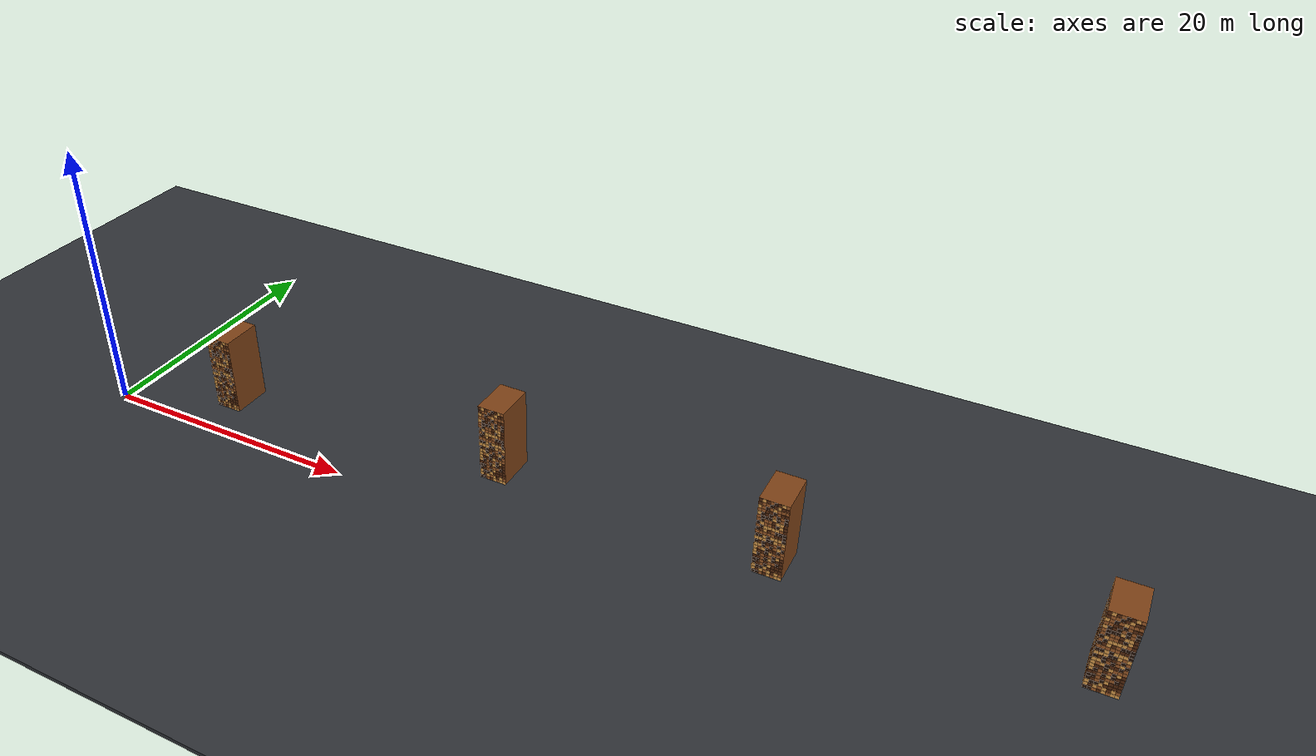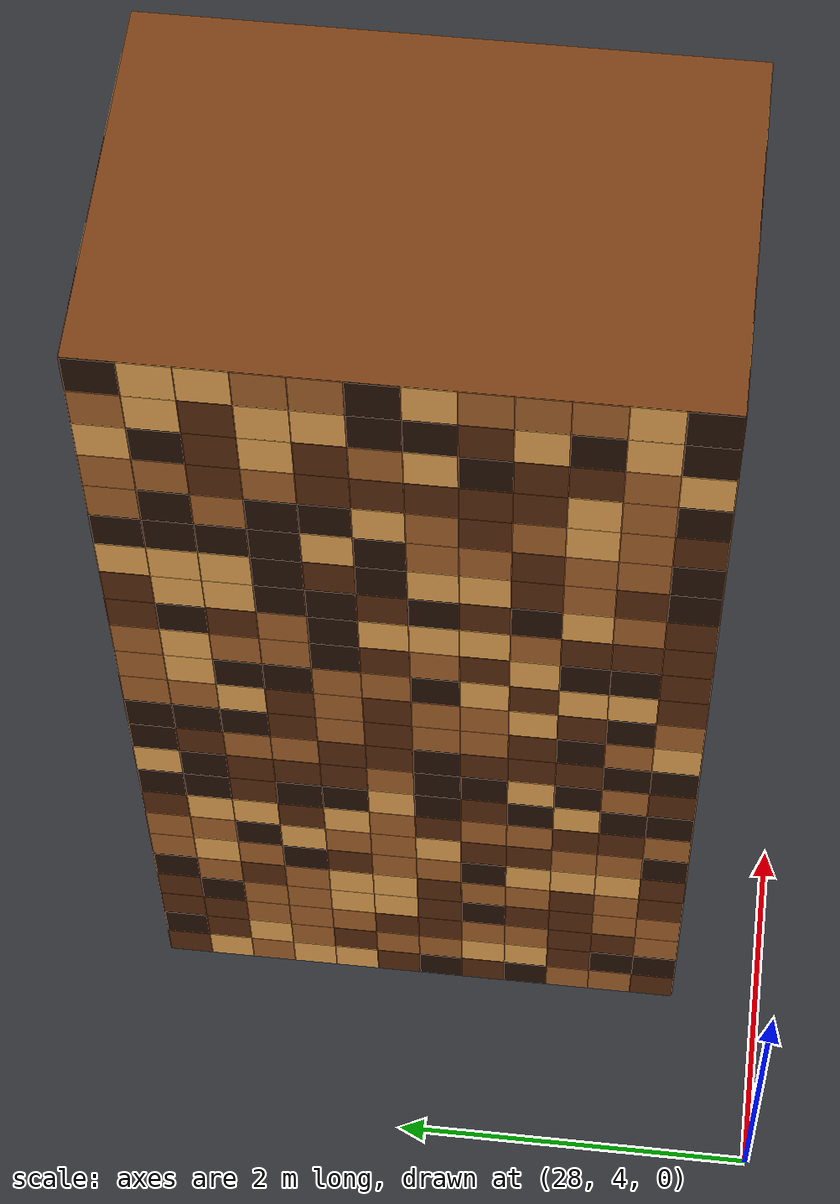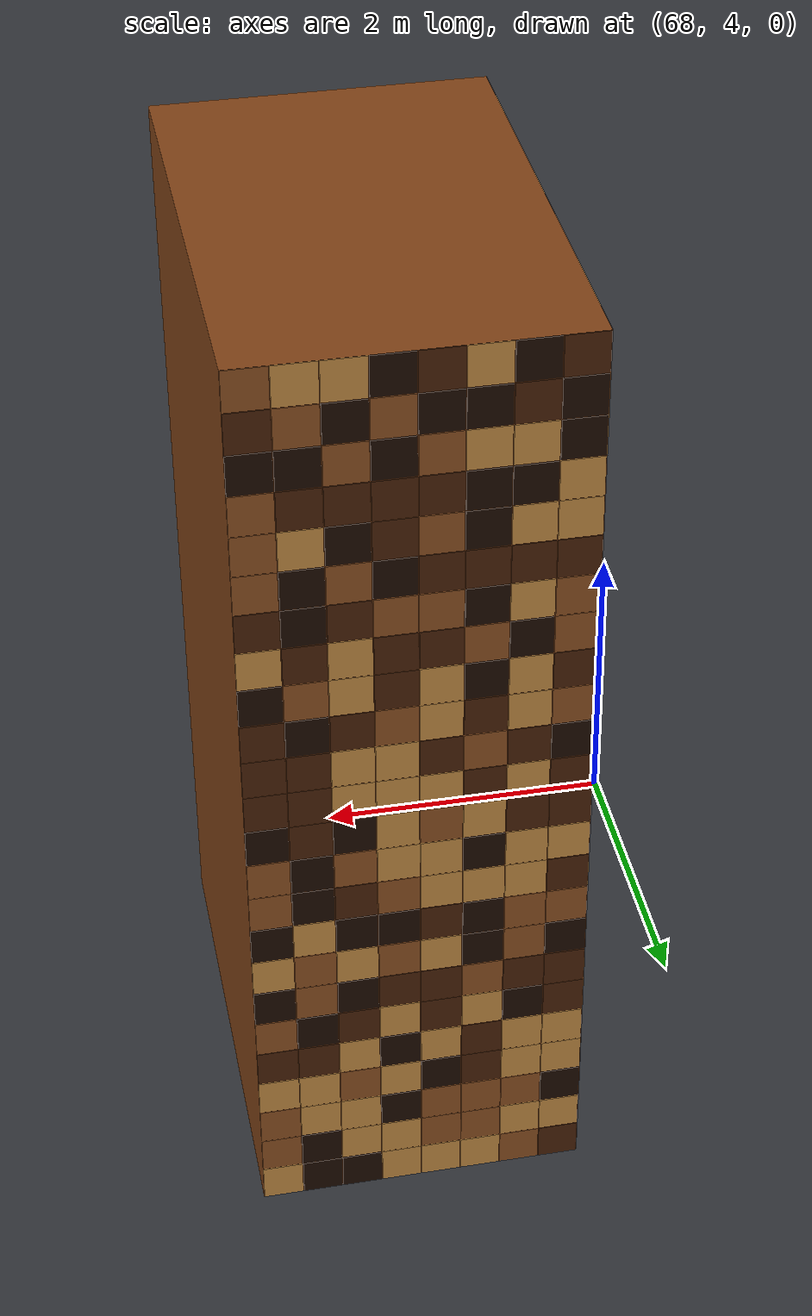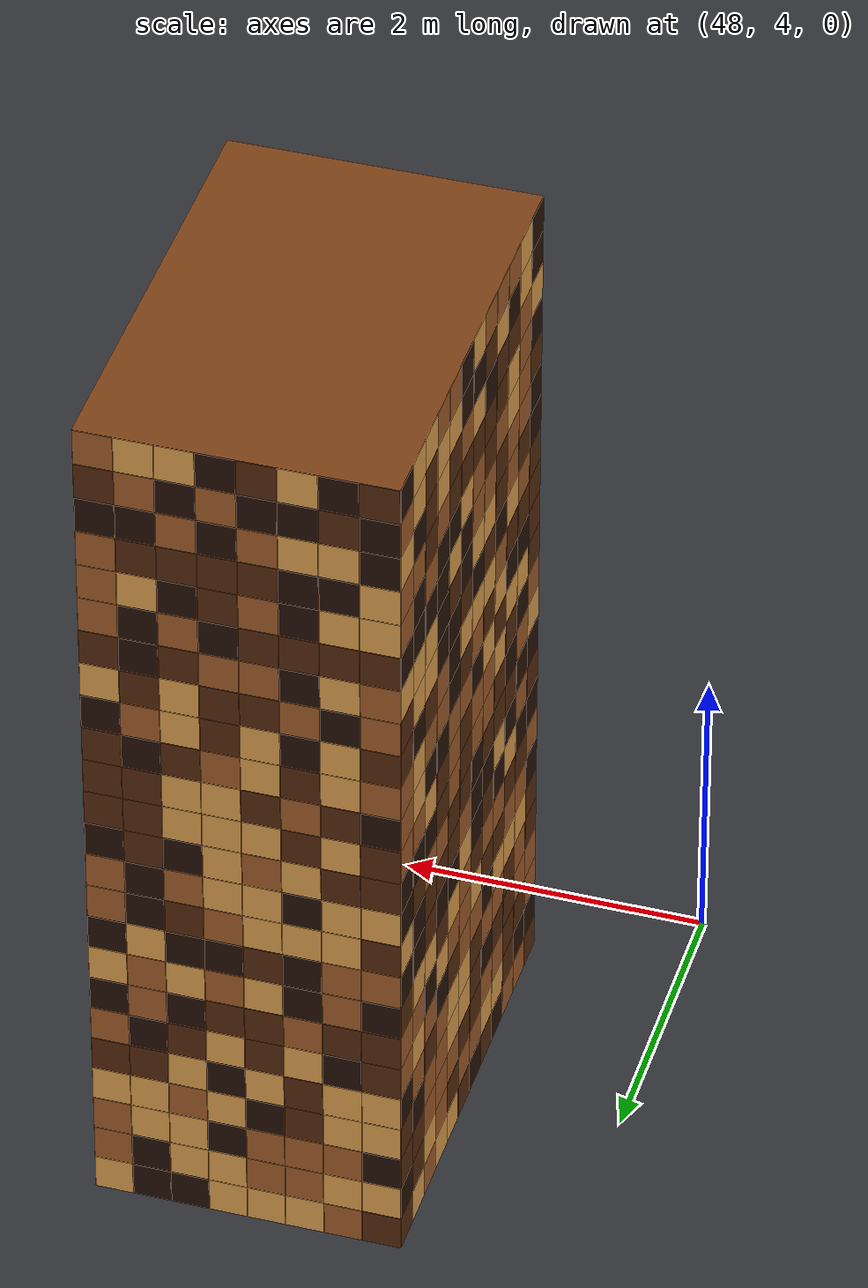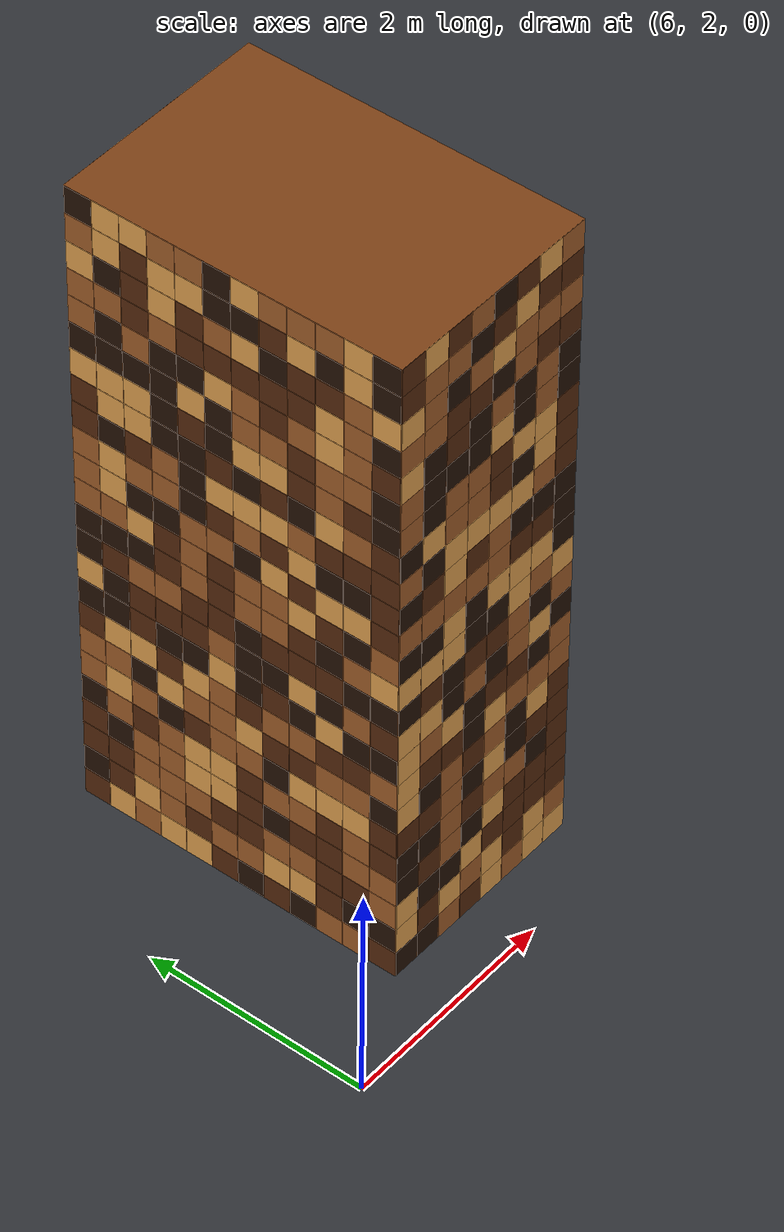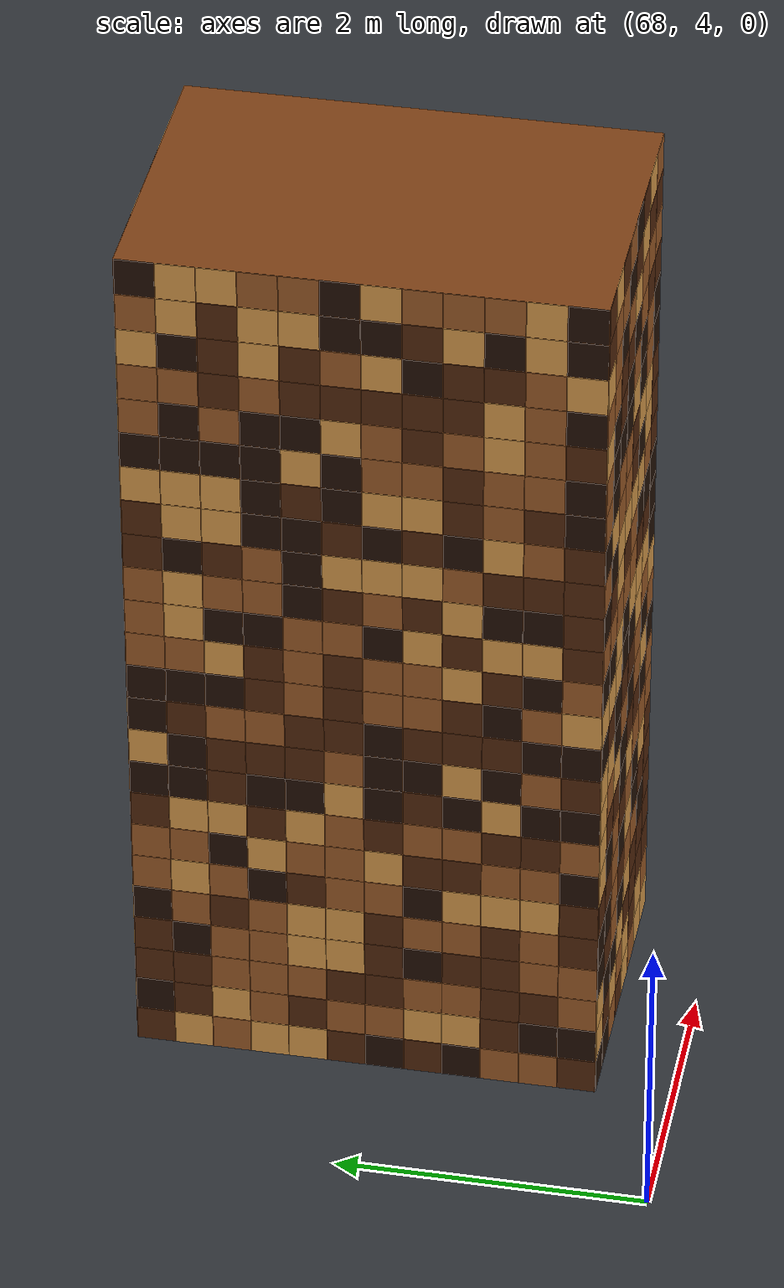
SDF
<sdf version="1.9">
 <world name="monocular_highspeed_10">
  <physics name="1ms" type="ignore">
   <max_step_size>0.001</max_step_size>
   <real_time_factor>1.0</real_time_factor>
  </physics>
  <plugin filename="gz-sim-physics-system" name="gz::sim::systems::Physics"/>
  <plugin filename="gz-sim-sensors-system" name="gz::sim::systems::Sensors">
   <render_engine>ogre2</render_engine>
  </plugin>
  <plugin filename="gz-sim-user-commands-system" name="gz::sim::systems::UserCommands"/>
  <plugin filename="gz-sim-scene-broadcaster-system" name="gz::sim::systems::SceneBroadcaster"/>
  <plugin filename="gz-sim-imu-system" name="gz::sim::systems::Imu"/>
  <plugin filename="gz-sim-magnetometer-system" name="gz::sim::systems::Magnetometer"/>
  <plugin filename="gz-sim-air-pressure-system" name="gz::sim::systems::AirPressure"/>
  <plugin filename="gz-sim-navsat-system" name="gz::sim::systems::NavSat"/>
  <spherical_coordinates>
   <surface_model>EARTH_WGS84</surface_model>
   <latitude_deg>-35.363262</latitude_deg>
   <longitude_deg>149.165237</longitude_deg>
   <elevation>584</elevation>
   <heading_deg>0</heading_deg>
  </spherical_coordinates>
  <magnetic_field>2.1e-5 5.0e-6 -4.2e-5</magnetic_field>
  <scene><ambient>0.45 0.45 0.45 1</ambient><background>0.08 0.1 0.14 1</background><grid>true</grid></scene>
  <light type="directional" name="sun">
   <pose>0 0 40 0 0 0</pose>
   <diffuse>0.9 0.9 0.9 1</diffuse>
   <direction>-0.4 0.2 -1</direction>
  </light>
  <model name="asphalt">
   <static>true</static>
   <pose>150 0 -0.15 0 0 0</pose>
   <link name="body">
    <collision name="collision"><geometry><box><size>400 60 0.3</size></box></geometry></collision>
    <visual name="visual">
     <geometry><box><size>400 60 0.3</size></box></geometry>
     <material><ambient>.19 .20 .22 1</ambient><diffuse>.19 .20 .22 1</diffuse></material>
    </visual>
   </link>
  </model>
  <include><name>obstacle_0</name><uri>model://monocular_textured_box</uri><pose>8 4 3 0 0 0</pose></include>
  <include><name>obstacle_1</name><uri>model://monocular_textured_box</uri><pose>30 6 3 0 0 0</pose></include>
  <include><name>obstacle_2</name><uri>model://monocular_textured_box</uri><pose>50 6 3 0 0 0</pose></include>
  <include><name>obstacle_3</name><uri>model://monocular_textured_box</uri><pose>70 6 3 0 0 0</pose></include>
 </world>
</sdf>

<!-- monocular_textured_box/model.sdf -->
<sdf version="1.9"><model name="monocular_textured_box"><static>true</static><link name="body"><collision name="collision"><geometry><box><size>2 3 6</size></box></geometry></collision><visual name="crate_base"><pose>0 0 0 0 0 0</pose><geometry><box><size>2 3 6</size></box></geometry><material><ambient>0.5 0.26 0.09 1</ambient><diffuse>0.5 0.26 0.09 1</diffuse></material></visual><visual name="wood_0_-1_0_0"><pose>-1.002 -1.375 -2.875 0 0 0</pose><geometry><box><size>0.003 0.245 0.245</size></box></geometry><material><ambient>0.35 0.17 0.06 1</ambient><diffuse>0.35 0.17 0.06 1</diffuse></material></visual><visual name="wood_0_-1_0_1"><pose>-1.002 -1.375 -2.625 0 0 0</pose><geometry><box><size>0.003 0.245 0.245</size></box></geometry><material><ambient>0.15 0.07 0.025 1</ambient><diffuse>0.15 0.07 0.025 1</diffuse></material></visual><visual name="wood_0_-1_0_2"><pose>-1.002 -1.375 -2.375 0 0 0</pose><geometry><box><size>0.003 0.245 0.245</size></box></geometry><material><ambient>0.65 0.38 0.17 1</ambient><diffuse>0.65 0.38 0.17 1</diffuse></material></visual><visual name="wood_0_-1_0_3"><pose>-1.002 -1.375 -2.125 0 0 0</pose><geometry><box><size>0.003 0.245 0.245</size></box></geometry><material><ambient>0.65 0.38 0.17 1</ambient><diffuse>0.65 0.38 0.17 1</diffuse></material></visual><visual name="wood_0_-1_0_4"><pose>-1.002 -1.375 -1.875 0 0 0</pose><geometry><box><size>0.003 0.245 0.245</size></box></geometry><material><ambient>0.35 0.17 0.06 1</ambient><diffuse>0.35 0.17 0.06 1</diffuse></material></visual><visual name="wood_0_-1_0_5"><pose>-1.002 -1.375 -1.625 0 0 0</pose><geometry><box><size>0.003 0.245 0.245</size></box></geometry><material><ambient>0.35 0.17 0.06 1</ambient><diffuse>0.35 0.17 0.06 1</diffuse></material></visual><visual name="wood_0_-1_0_6"><pose>-1.002 -1.375 -1.375 0 0 0</pose><geometry><box><size>0.003 0.245 0.245</size></box></geometry><material><ambient>0.15 0.07 0.025 1</ambient><diffuse>0.15 0.07 0.025 1</diffuse></material></visual><visual name="wood_0_-1_0_7"><pose>-1.002 -1.375 -1.125 0 0 0</pose><geometry><box><size>0.003 0.245 0.245</size></box></geometry><material><ambient>0.65 0.38 0.17 1</ambient><diffuse>0.65 0.38 0.17 1</diffuse></material></visual><visual name="wood_0_-1_0_8"><pose>-1.002 -1.375 -0.875 0 0 0</pose><geometry><box><size>0.003 0.245 0.245</size></box></geometry><material><ambient>0.15 0.07 0.025 1</ambient><diffuse>0.15 0.07 0.025 1</diffuse></material></visual><visual name="wood_0_-1_0_9"><pose>-1.002 -1.375 -0.625 0 0 0</pose><geometry><box><size>0.003 0.245 0.245</size></box></geometry><material><ambient>0.35 0.17 0.06 1</ambient><diffuse>0.35 0.17 0.06 1</diffuse></material></visual><visual name="wood_0_-1_0_10"><pose>-1.002 -1.375 -0.375 0 0 0</pose><geometry><box><size>0.003 0.245 0.245</size></box></geometry><material><ambient>0.15 0.07 0.025 1</ambient><diffuse>0.15 0.07 0.025 1</diffuse></material></visual><visual name="wood_0_-1_0_11"><pose>-1.002 -1.375 -0.125 0 0 0</pose><geometry><box><size>0.003 0.245 0.245</size></box></geometry><material><ambient>0.9 0.65 0.32 1</ambient><diffuse>0.9 0.65 0.32 1</diffuse></material></visual><visual name="wood_0_-1_0_12"><pose>-1.002 -1.375 0.125 0 0 0</pose><geometry><box><size>0.003 0.245 0.245</size></box></geometry><material><ambient>0.65 0.38 0.17 1</ambient><diffuse>0.65 0.38 0.17 1</diffuse></material></visual><visual name="wood_0_-1_0_13"><pose>-1.002 -1.375 0.375 0 0 0</pose><geometry><box><size>0.003 0.245 0.245</size></box></geometry><material><ambient>0.35 0.17 0.06 1</ambient><diffuse>0.35 0.17 0.06 1</diffuse></material></visual><visual name="wood_0_-1_0_14"><pose>-1.002 -1.375 0.625 0 0 0</pose><geometry><box><size>0.003 0.245 0.245</size></box></geometry><material><ambient>0.35 0.17 0.06 1</ambient><diffuse>0.35 0.17 0.06 1</diffuse></material></visual><visual name="wood_0_-1_0_15"><pose>-1.002 -1.375 0.875 0 0 0</pose><geometry><box><size>0.003 0.245 0.245</size></box></geometry><material><ambient>0.35 0.17 0.06 1</ambient><diffuse>0.35 0.17 0.06 1</diffuse></material></visual><visual name="wood_0_-1_0_16"><pose>-1.002 -1.375 1.125 0 0 0</pose><geometry><box><size>0.003 0.245 0.245</size></box></geometry><material><ambient>0.35 0.17 0.06 1</ambient><diffuse>0.35 0.17 0.06 1</diffuse></material></visual><visual name="wood_0_-1_0_17"><pose>-1.002 -1.375 1.375 0 0 0</pose><geometry><box><size>0.003 0.245 0.245</size></box></geometry><material><ambient>0.15 0.07 0.025 1</ambient><diffuse>0.15 0.07 0.025 1</diffuse></material></visual><visual name="wood_0_-1_0_18"><pose>-1.002 -1.375 1.625 0 0 0</pose><geometry><box><size>0.003 0.245 0.245</size></box></geometry><material><ambient>0.15 0.07 0.025 1</ambient><diffuse>0.15 0.07 0.025 1</diffuse></material></visual><visual name="wood_0_-1_0_19"><pose>-1.002 -1.375 1.875 0 0 0</pose><geometry><box><size>0.003 0.245 0.245</size></box></geometry><material><ambient>0.35 0.17 0.06 1</ambient><diffuse>0.35 0.17 0.06 1</diffuse></material></visual><visual name="wood_0_-1_0_20"><pose>-1.002 -1.375 2.125 0 0 0</pose><geometry><box><size>0.003 0.245 0.245</size></box></geometry><material><ambient>0.15 0.07 0.025 1</ambient><diffuse>0.15 0.07 0.025 1</diffuse></material></visual><visual name="wood_0_-1_0_21"><pose>-1.002 -1.375 2.375 0 0 0</pose><geometry><box><size>0.003 0.245 0.245</size></box></geometry><material><ambient>0.9 0.65 0.32 1</ambient><diffuse>0.9 0.65 0.32 1</diffuse></material></visual><visual name="wood_0_-1_0_22"><pose>-1.002 -1.375 2.625 0 0 0</pose><geometry><box><size>0.003 0.245 0.245</size></box></geometry><material><ambient>0.15 0.07 0.025 1</ambient><diffuse>0.15 0.07 0.025 1</diffuse></material></visual><visual name="wood_0_-1_0_23"><pose>-1.002 -1.375 2.875 0 0 0</pose><geometry><box><size>0.003 0.245 0.245</size></box></geometry><material><ambient>0.15 0.07 0.025 1</ambient><diffuse>0.15 0.07 0.025 1</diffuse></material></visual><visual name="wood_0_-1_1_0"><pose>-1.002 -1.125 -2.875 0 0 0</pose><geometry><box><size>0.003 0.245 0.245</size></box></geometry><material><ambient>0.65 0.38 0.17 1</ambient><diffuse>0.65 0.38 0.17 1</diffuse></material></visual><visual name="wood_0_-1_1_1"><pose>-1.002 -1.125 -2.625 0 0 0</pose><geometry><box><size>0.003 0.245 0.245</size></box></geometry><material><ambient>0.15 0.07 0.025 1</ambient><diffuse>0.15 0.07 0.025 1</diffuse></material></visual><visual name="wood_0_-1_1_2"><pose>-1.002 -1.125 -2.375 0 0 0</pose><geometry><box><size>0.003 0.245 0.245</size></box></geometry><material><ambient>0.35 0.17 0.06 1</ambient><diffuse>0.35 0.17 0.06 1</diffuse></material></visual><visual name="wood_0_-1_1_3"><pose>-1.002 -1.125 -2.125 0 0 0</pose><geometry><box><size>0.003 0.245 0.245</size></box></geometry><material><ambient>0.65 0.38 0.17 1</ambient><diffuse>0.65 0.38 0.17 1</diffuse></material></visual><visual name="wood_0_-1_1_4"><pose>-1.002 -1.125 -1.875 0 0 0</pose><geometry><box><size>0.003 0.245 0.245</size></box></geometry><material><ambient>0.65 0.38 0.17 1</ambient><diffuse>0.65 0.38 0.17 1</diffuse></material></visual><visual name="wood_0_-1_1_5"><pose>-1.002 -1.125 -1.625 0 0 0</pose><geometry><box><size>0.003 0.245 0.245</size></box></geometry><material><ambient>0.9 0.65 0.32 1</ambient><diffuse>0.9 0.65 0.32 1</diffuse></material></visual><visual name="wood_0_-1_1_6"><pose>-1.002 -1.125 -1.375 0 0 0</pose><geometry><box><size>0.003 0.245 0.245</size></box></geometry><material><ambient>0.65 0.38 0.17 1</ambient><diffuse>0.65 0.38 0.17 1</diffuse></material></visual><visual name="wood_0_-1_1_7"><pose>-1.002 -1.125 -1.125 0 0 0</pose><geometry><box><size>0.003 0.245 0.245</size></box></geometry><material><ambient>0.35 0.17 0.06 1</ambient><diffuse>0.35 0.17 0.06 1</diffuse></material></visual><visual name="wood_0_-1_1_8"><pose>-1.002 -1.125 -0.875 0 0 0</pose><geometry><box><size>0.003 0.245 0.245</size></box></geometry><material><ambient>0.15 0.07 0.025 1</ambient><diffuse>0.15 0.07 0.025 1</diffuse></material></visual><visual name="wood_0_-1_1_9"><pose>-1.002 -1.125 -0.625 0 0 0</pose><geometry><box><size>0.003 0.245 0.245</size></box></geometry><material><ambient>0.65 0.38 0.17 1</ambient><diffuse>0.65 0.38 0.17 1</diffuse></material></visual><visual name="wood_0_-1_1_10"><pose>-1.002 -1.125 -0.375 0 0 0</pose><geometry><box><size>0.003 0.245 0.245</size></box></geometry><material><ambient>0.15 0.07 0.025 1</ambient><diffuse>0.15 0.07 0.025 1</diffuse></material></visual><visual name="wood_0_-1_1_11"><pose>-1.002 -1.125 -0.125 0 0 0</pose><geometry><box><size>0.003 0.245 0.245</size></box></geometry><material><ambient>0.65 0.38 0.17 1</ambient><diffuse>0.65 0.38 0.17 1</diffuse></material></visual><visual name="wood_0_-1_1_12"><pose>-1.002 -1.125 0.125 0 0 0</pose><geometry><box><size>0.003 0.245 0.245</size></box></geometry><material><ambient>0.15 0.07 0.025 1</ambient><diffuse>0.15 0.07 0.025 1</diffuse></material></visual><visual name="wood_0_-1_1_13"><pose>-1.002 -1.125 0.375 0 0 0</pose><geometry><box><size>0.003 0.245 0.245</size></box></geometry><material><ambient>0.9 0.65 0.32 1</ambient><diffuse>0.9 0.65 0.32 1</diffuse></material></visual><visual name="wood_0_-1_1_14"><pose>-1.002 -1.125 0.625 0 0 0</pose><geometry><box><size>0.003 0.245 0.245</size></box></geometry><material><ambient>0.15 0.07 0.025 1</ambient><diffuse>0.15 0.07 0.025 1</diffuse></material></visual><visual name="wood_0_-1_1_15"><pose>-1.002 -1.125 0.875 0 0 0</pose><geometry><box><size>0.003 0.245 0.245</size></box></geometry><material><ambient>0.35 0.17 0.06 1</ambient><diffuse>0.35 0.17 0.06 1</diffuse></material></visual><visual name="wood_0_-1_1_16"><pose>-1.002 -1.125 1.125 0 0 0</pose><geometry><box><size>0.003 0.245 0.245</size></box></geometry><material><ambient>0.65 0.38 0.17 1</ambient><diffuse>0.65 0.38 0.17 1</diffuse></material></visual><visual name="wood_0_-1_1_17"><pose>-1.002 -1.125 1.375 0 0 0</pose><geometry><box><size>0.003 0.245 0.245</size></box></geometry><material><ambient>0.35 0.17 0.06 1</ambient><diffuse>0.35 0.17 0.06 1</diffuse></material></visual><visual name="wood_0_-1_1_18"><pose>-1.002 -1.125 1.625 0 0 0</pose><geometry><box><size>0.003 0.245 0.245</size></box></geometry><material><ambient>0.65 0.38 0.17 1</ambient><diffuse>0.65 0.38 0.17 1</diffuse></material></visual><visual name="wood_0_-1_1_19"><pose>-1.002 -1.125 1.875 0 0 0</pose><geometry><box><size>0.003 0.245 0.245</size></box></geometry><material><ambient>0.65 0.38 0.17 1</ambient><diffuse>0.65 0.38 0.17 1</diffuse></material></visual><visual name="wood_0_-1_1_20"><pose>-1.002 -1.125 2.125 0 0 0</pose><geometry><box><size>0.003 0.245 0.245</size></box></geometry><material><ambient>0.65 0.38 0.17 1</ambient><diffuse>0.65 0.38 0.17 1</diffuse></material></visual><visual name="wood_0_-1_1_21"><pose>-1.002 -1.125 2.375 0 0 0</pose><geometry><box><size>0.003 0.245 0.245</size></box></geometry><material><ambient>0.65 0.38 0.17 1</ambient><diffuse>0.65 0.38 0.17 1</diffuse></material></visual><visual name="wood_0_-1_1_22"><pose>-1.002 -1.125 2.625 0 0 0</pose><geometry><box><size>0.003 0.245 0.245</size></box></geometry><material><ambient>0.9 0.65 0.32 1</ambient><diffuse>0.9 0.65 0.32 1</diffuse></material></visual><visual name="wood_0_-1_1_23"><pose>-1.002 -1.125 2.875 0 0 0</pose><geometry><box><size>0.003 0.245 0.245</size></box></geometry><material><ambient>0.9 0.65 0.32 1</ambient><diffuse>0.9 0.65 0.32 1</diffuse></material></visual><visual name="wood_0_-1_2_0"><pose>-1.002 -0.875 -2.875 0 0 0</pose><geometry><box><size>0.003 0.245 0.245</size></box></geometry><material><ambient>0.65 0.38 0.17 1</ambient><diffuse>0.65 0.38 0.17 1</diffuse></material></visual><visual name="wood_0_-1_2_1"><pose>-1.002 -0.875 -2.625 0 0 0</pose><geometry><box><size>0.003 0.245 0.245</size></box></geometry><material><ambient>0.35 0.17 0.06 1</ambient><diffuse>0.35 0.17 0.06 1</diffuse></material></visual><visual name="wood_0_-1_2_2"><pose>-1.002 -0.875 -2.375 0 0 0</pose><geometry><box><size>0.003 0.245 0.245</size></box></geometry><material><ambient>0.35 0.17 0.06 1</ambient><diffuse>0.35 0.17 0.06 1</diffuse></material></visual><visual name="wood_0_-1_2_3"><pose>-1.002 -0.875 -2.125 0 0 0</pose><geometry><box><size>0.003 0.245 0.245</size></box></geometry><material><ambient>0.35 0.17 0.06 1</ambient><diffuse>0.35 0.17 0.06 1</diffuse></material></visual><visual name="wood_0_-1_2_4"><pose>-1.002 -0.875 -1.875 0 0 0</pose><geometry><box><size>0.003 0.245 0.245</size></box></geometry><material><ambient>0.35 0.17 0.06 1</ambient><diffuse>0.35 0.17 0.06 1</diffuse></material></visual><visual name="wood_0_-1_2_5"><pose>-1.002 -0.875 -1.625 0 0 0</pose><geometry><box><size>0.003 0.245 0.245</size></box></geometry><material><ambient>0.9 0.65 0.32 1</ambient><diffuse>0.9 0.65 0.32 1</diffuse></material></visual><visual name="wood_0_-1_2_6"><pose>-1.002 -0.875 -1.375 0 0 0</pose><geometry><box><size>0.003 0.245 0.245</size></box></geometry><material><ambient>0.65 0.38 0.17 1</ambient><diffuse>0.65 0.38 0.17 1</diffuse></material></visual><visual name="wood_0_-1_2_7"><pose>-1.002 -0.875 -1.125 0 0 0</pose><geometry><box><size>0.003 0.245 0.245</size></box></geometry><material><ambient>0.35 0.17 0.06 1</ambient><diffuse>0.35 0.17 0.06 1</diffuse></material></visual><visual name="wood_0_-1_2_8"><pose>-1.002 -0.875 -0.875 0 0 0</pose><geometry><box><size>0.003 0.245 0.245</size></box></geometry><material><ambient>0.9 0.65 0.32 1</ambient><diffuse>0.9 0.65 0.32 1</diffuse></material></visual><visual name="wood_0_-1_2_9"><pose>-1.002 -0.875 -0.625 0 0 0</pose><geometry><box><size>0.003 0.245 0.245</size></box></geometry><material><ambient>0.15 0.07 0.025 1</ambient><diffuse>0.15 0.07 0.025 1</diffuse></material></visual><visual name="wood_0_-1_2_10"><pose>-1.002 -0.875 -0.375 0 0 0</pose><geometry><box><size>0.003 0.245 0.245</size></box></geometry><material><ambient>0.35 0.17 0.06 1</ambient><diffuse>0.35 0.17 0.06 1</diffuse></material></visual><visual name="wood_0_-1_2_11"><pose>-1.002 -0.875 -0.125 0 0 0</pose><geometry><box><size>0.003 0.245 0.245</size></box></geometry><material><ambient>0.15 0.07 0.025 1</ambient><diffuse>0.15 0.07 0.025 1</diffuse></material></visual><visual name="wood_0_-1_2_12"><pose>-1.002 -0.875 0.125 0 0 0</pose><geometry><box><size>0.003 0.245 0.245</size></box></geometry><material><ambient>0.35 0.17 0.06 1</ambient><diffuse>0.35 0.17 0.06 1</diffuse></material></visual><visual name="wood_0_-1_2_13"><pose>-1.002 -0.875 0.375 0 0 0</pose><geometry><box><size>0.003 0.245 0.245</size></box></geometry><material><ambient>0.9 0.65 0.32 1</ambient><diffuse>0.9 0.65 0.32 1</diffuse></material></visual><visual name="wood_0_-1_2_14"><pose>-1.002 -0.875 0.625 0 0 0</pose><geometry><box><size>0.003 0.245 0.245</size></box></geometry><material><ambient>0.15 0.07 0.025 1</ambient><diffuse>0.15 0.07 0.025 1</diffuse></material></visual><visual name="wood_0_-1_2_15"><pose>-1.002 -0.875 0.875 0 0 0</pose><geometry><box><size>0.003 0.245 0.245</size></box></geometry><material><ambient>0.35 0.17 0.06 1</ambient><diffuse>0.35 0.17 0.06 1</diffuse></material></visual><visual name="wood_0_-1_2_16"><pose>-1.002 -0.875 1.125 0 0 0</pose><geometry><box><size>0.003 0.245 0.245</size></box></geometry><material><ambient>0.9 0.65 0.32 1</ambient><diffuse>0.9 0.65 0.32 1</diffuse></material></visual><visual name="wood_0_-1_2_17"><pose>-1.002 -0.875 1.375 0 0 0</pose><geometry><box><size>0.003 0.245 0.245</size></box></geometry><material><ambient>0.65 0.38 0.17 1</ambient><diffuse>0.65 0.38 0.17 1</diffuse></material></visual><visual name="wood_0_-1_2_18"><pose>-1.002 -0.875 1.625 0 0 0</pose><geometry><box><size>0.003 0.245 0.245</size></box></geometry><material><ambient>0.65 0.38 0.17 1</ambient><diffuse>0.65 0.38 0.17 1</diffuse></material></visual><visual name="wood_0_-1_2_19"><pose>-1.002 -0.875 1.875 0 0 0</pose><geometry><box><size>0.003 0.245 0.245</size></box></geometry><material><ambient>0.9 0.65 0.32 1</ambient><diffuse>0.9 0.65 0.32 1</diffuse></material></visual><visual name="wood_0_-1_2_20"><pose>-1.002 -0.875 2.125 0 0 0</pose><geometry><box><size>0.003 0.245 0.245</size></box></geometry><material><ambient>0.9 0.65 0.32 1</ambient><diffuse>0.9 0.65 0.32 1</diffuse></material></visual><visual name="wood_0_-1_2_21"><pose>-1.002 -0.875 2.375 0 0 0</pose><geometry><box><size>0.003 0.245 0.245</size></box></geometry><material><ambient>0.35 0.17 0.06 1</ambient><diffuse>0.35 0.17 0.06 1</diffuse></material></visual><visual name="wood_0_-1_2_22"><pose>-1.002 -0.875 2.625 0 0 0</pose><geometry><box><size>0.003 0.245 0.245</size></box></geometry><material><ambient>0.15 0.07 0.025 1</ambient><diffuse>0.15 0.07 0.025 1</diffuse></material></visual><visual name="wood_0_-1_2_23"><pose>-1.002 -0.875 2.875 0 0 0</pose><geometry><box><size>0.003 0.245 0.245</size></box></geometry><material><ambient>0.65 0.38 0.17 1</ambient><diffuse>0.65 0.38 0.17 1</diffuse></material></visual><visual name="wood_0_-1_3_0"><pose>-1.002 -0.625 -2.875 0 0 0</pose><geometry><box><size>0.003 0.245 0.245</size></box></geometry><material><ambient>0.15 0.07 0.025 1</ambient><diffuse>0.15 0.07 0.025 1</diffuse></material></visual><visual name="wood_0_-1_3_1"><pose>-1.002 -0.625 -2.625 0 0 0</pose><geometry><box><size>0.003 0.245 0.245</size></box></geometry><material><ambient>0.9 0.65 0.32 1</ambient><diffuse>0.9 0.65 0.32 1</diffuse></material></visual><visual name="wood_0_-1_3_2"><pose>-1.002 -0.625 -2.375 0 0 0</pose><geometry><box><size>0.003 0.245 0.245</size></box></geometry><material><ambient>0.65 0.38 0.17 1</ambient><diffuse>0.65 0.38 0.17 1</diffuse></material></visual><visual name="wood_0_-1_3_3"><pose>-1.002 -0.625 -2.125 0 0 0</pose><geometry><box><size>0.003 0.245 0.245</size></box></geometry><material><ambient>0.35 0.17 0.06 1</ambient><diffuse>0.35 0.17 0.06 1</diffuse></material></visual><visual name="wood_0_-1_3_4"><pose>-1.002 -0.625 -1.875 0 0 0</pose><geometry><box><size>0.003 0.245 0.245</size></box></geometry><material><ambient>0.65 0.38 0.17 1</ambient><diffuse>0.65 0.38 0.17 1</diffuse></material></visual><visual name="wood_0_-1_3_5"><pose>-1.002 -0.625 -1.625 0 0 0</pose><geometry><box><size>0.003 0.245 0.245</size></box></geometry><material><ambient>0.9 0.65 0.32 1</ambient><diffuse>0.9 0.65 0.32 1</diffuse></material></visual><visual name="wood_0_-1_3_6"><pose>-1.002 -0.625 -1.375 0 0 0</pose><geometry><box><size>0.003 0.245 0.245</size></box></geometry><material><ambient>0.35 0.17 0.06 1</ambient><diffuse>0.35 0.17 0.06 1</diffuse></material></visual><visual name="wood_0_-1_3_7"><pose>-1.002 -0.625 -1.125 0 0 0</pose><geometry><box><size>0.003 0.245 0.245</size></box></geometry><material><ambient>0.65 0.38 0.17 1</ambient><diffuse>0.65 0.38 0.17 1</diffuse></material></visual><visual name="wood_0_-1_3_8"><pose>-1.002 -0.625 -0.875 0 0 0</pose><geometry><box><size>0.003 0.245 0.245</size></box></geometry><material><ambient>0.15 0.07 0.025 1</ambient><diffuse>0.15 0.07 0.025 1</diffuse></material></visual><visual name="wood_0_-1_3_9"><pose>-1.002 -0.625 -0.625 0 0 0</pose><geometry><box><size>0.003 0.245 0.245</size></box></geometry><material><ambient>0.9 0.65 0.32 1</ambient><diffuse>0.9 0.65 0.32 1</diffuse></material></visual><visual name="wood_0_-1_3_10"><pose>-1.002 -0.625 -0.375 0 0 0</pose><geometry><box><size>0.003 0.245 0.245</size></box></geometry><material><ambient>0.35 0.17 0.06 1</ambient><diffuse>0.35 0.17 0.06 1</diffuse></material></visual><visual name="wood_0_-1_3_11"><pose>-1.002 -0.625 -0.125 0 0 0</pose><geometry><box><size>0.003 0.245 0.245</size></box></geometry><material><ambient>0.35 0.17 0.06 1</ambient><diffuse>0.35 0.17 0.06 1</diffuse></material></visual><visual name="wood_0_-1_3_12"><pose>-1.002 -0.625 0.125 0 0 0</pose><geometry><box><size>0.003 0.245 0.245</size></box></geometry><material><ambient>0.9 0.65 0.32 1</ambient><diffuse>0.9 0.65 0.32 1</diffuse></material></visual><visual name="wood_0_-1_3_13"><pose>-1.002 -0.625 0.375 0 0 0</pose><geometry><box><size>0.003 0.245 0.245</size></box></geometry><material><ambient>0.35 0.17 0.06 1</ambient><diffuse>0.35 0.17 0.06 1</diffuse></material></visual><visual name="wood_0_-1_3_14"><pose>-1.002 -0.625 0.625 0 0 0</pose><geometry><box><size>0.003 0.245 0.245</size></box></geometry><material><ambient>0.9 0.65 0.32 1</ambient><diffuse>0.9 0.65 0.32 1</diffuse></material></visual><visual name="wood_0_-1_3_15"><pose>-1.002 -0.625 0.875 0 0 0</pose><geometry><box><size>0.003 0.245 0.245</size></box></geometry><material><ambient>0.65 0.38 0.17 1</ambient><diffuse>0.65 0.38 0.17 1</diffuse></material></visual><visual name="wood_0_-1_3_16"><pose>-1.002 -0.625 1.125 0 0 0</pose><geometry><box><size>0.003 0.245 0.245</size></box></geometry><material><ambient>0.15 0.07 0.025 1</ambient><diffuse>0.15 0.07 0.025 1</diffuse></material></visual><visual name="wood_0_-1_3_17"><pose>-1.002 -0.625 1.375 0 0 0</pose><geometry><box><size>0.003 0.245 0.245</size></box></geometry><material><ambient>0.35 0.17 0.06 1</ambient><diffuse>0.35 0.17 0.06 1</diffuse></material></visual><visual name="wood_0_-1_3_18"><pose>-1.002 -0.625 1.625 0 0 0</pose><geometry><box><size>0.003 0.245 0.245</size></box></geometry><material><ambient>0.35 0.17 0.06 1</ambient><diffuse>0.35 0.17 0.06 1</diffuse></material></visual><visual name="wood_0_-1_3_19"><pose>-1.002 -0.625 1.875 0 0 0</pose><geometry><box><size>0.003 0.245 0.245</size></box></geometry><material><ambient>0.65 0.38 0.17 1</ambient><diffuse>0.65 0.38 0.17 1</diffuse></material></visual><visual name="wood_0_-1_3_20"><pose>-1.002 -0.625 2.125 0 0 0</pose><geometry><box><size>0.003 0.245 0.245</size></box></geometry><material><ambient>0.35 0.17 0.06 1</ambient><diffuse>0.35 0.17 0.06 1</diffuse></material></visual><visual name="wood_0_-1_3_21"><pose>-1.002 -0.625 2.375 0 0 0</pose><geometry><box><size>0.003 0.245 0.245</size></box></geometry><material><ambient>0.35 0.17 0.06 1</ambient><diffuse>0.35 0.17 0.06 1</diffuse></material></visual><visual name="wood_0_-1_3_22"><pose>-1.002 -0.625 2.625 0 0 0</pose><geometry><box><size>0.003 0.245 0.245</size></box></geometry><material><ambient>0.9 0.65 0.32 1</ambient><diffuse>0.9 0.65 0.32 1</diffuse></material></visual><visual name="wood_0_-1_3_23"><pose>-1.002 -0.625 2.875 0 0 0</pose><geometry><box><size>0.003 0.245 0.245</size></box></geometry><material><ambient>0.65 0.38 0.17 1</ambient><diffuse>0.65 0.38 0.17 1</diffuse></material></visual><visual name="wood_0_-1_4_0"><pose>-1.002 -0.375 -2.875 0 0 0</pose><geometry><box><size>0.003 0.245 0.245</size></box></geometry><material><ambient>0.35 0.17 0.06 1</ambient><diffuse>0.35 0.17 0.06 1</diffuse></material></visual><visual name="wood_0_-1_4_1"><pose>-1.002 -0.375 -2.625 0 0 0</pose><geometry><box><size>0.003 0.245 0.245</size></box></geometry><material><ambient>0.9 0.65 0.32 1</ambient><diffuse>0.9 0.65 0.32 1</diffuse></material></visual><visual name="wood_0_-1_4_2"><pose>-1.002 -0.375 -2.375 0 0 0</pose><geometry><box><size>0.003 0.245 0.245</size></box></geometry><material><ambient>0.65 0.38 0.17 1</ambient><diffuse>0.65 0.38 0.17 1</diffuse></material></visual><visual name="wood_0_-1_4_3"><pose>-1.002 -0.375 -2.125 0 0 0</pose><geometry><box><size>0.003 0.245 0.245</size></box></geometry><material><ambient>0.15 0.07 0.025 1</ambient><diffuse>0.15 0.07 0.025 1</diffuse></material></visual><visual name="wood_0_-1_4_4"><pose>-1.002 -0.375 -1.875 0 0 0</pose><geometry><box><size>0.003 0.245 0.245</size></box></geometry><material><ambient>0.65 0.38 0.17 1</ambient><diffuse>0.65 0.38 0.17 1</diffuse></material></visual><visual name="wood_0_-1_4_5"><pose>-1.002 -0.375 -1.625 0 0 0</pose><geometry><box><size>0.003 0.245 0.245</size></box></geometry><material><ambient>0.15 0.07 0.025 1</ambient><diffuse>0.15 0.07 0.025 1</diffuse></material></visual><visual name="wood_0_-1_4_6"><pose>-1.002 -0.375 -1.375 0 0 0</pose><geometry><box><size>0.003 0.245 0.245</size></box></geometry><material><ambient>0.35 0.17 0.06 1</ambient><diffuse>0.35 0.17 0.06 1</diffuse></material></visual><visual name="wood_0_-1_4_7"><pose>-1.002 -0.375 -1.125 0 0 0</pose><geometry><box><size>0.003 0.245 0.245</size></box></geometry><material><ambient>0.65 0.38 0.17 1</ambient><diffuse>0.65 0.38 0.17 1</diffuse></material></visual><visual name="wood_0_-1_4_8"><pose>-1.002 -0.375 -0.875 0 0 0</pose><geometry><box><size>0.003 0.245 0.245</size></box></geometry><material><ambient>0.35 0.17 0.06 1</ambient><diffuse>0.35 0.17 0.06 1</diffuse></material></visual><visual name="wood_0_-1_4_9"><pose>-1.002 -0.375 -0.625 0 0 0</pose><geometry><box><size>0.003 0.245 0.245</size></box></geometry><material><ambient>0.15 0.07 0.025 1</ambient><diffuse>0.15 0.07 0.025 1</diffuse></material></visual><visual name="wood_0_-1_4_10"><pose>-1.002 -0.375 -0.375 0 0 0</pose><geometry><box><size>0.003 0.245 0.245</size></box></geometry><material><ambient>0.35 0.17 0.06 1</ambient><diffuse>0.35 0.17 0.06 1</diffuse></material></visual><visual name="wood_0_-1_4_11"><pose>-1.002 -0.375 -0.125 0 0 0</pose><geometry><box><size>0.003 0.245 0.245</size></box></geometry><material><ambient>0.65 0.38 0.17 1</ambient><diffuse>0.65 0.38 0.17 1</diffuse></material></visual><visual name="wood_0_-1_4_12"><pose>-1.002 -0.375 0.125 0 0 0</pose><geometry><box><size>0.003 0.245 0.245</size></box></geometry><material><ambient>0.65 0.38 0.17 1</ambient><diffuse>0.65 0.38 0.17 1</diffuse></material></visual><visual name="wood_0_-1_4_13"><pose>-1.002 -0.375 0.375 0 0 0</pose><geometry><box><size>0.003 0.245 0.245</size></box></geometry><material><ambient>0.9 0.65 0.32 1</ambient><diffuse>0.9 0.65 0.32 1</diffuse></material></visual><visual name="wood_0_-1_4_14"><pose>-1.002 -0.375 0.625 0 0 0</pose><geometry><box><size>0.003 0.245 0.245</size></box></geometry><material><ambient>0.35 0.17 0.06 1</ambient><diffuse>0.35 0.17 0.06 1</diffuse></material></visual><visual name="wood_0_-1_4_15"><pose>-1.002 -0.375 0.875 0 0 0</pose><geometry><box><size>0.003 0.245 0.245</size></box></geometry><material><ambient>0.9 0.65 0.32 1</ambient><diffuse>0.9 0.65 0.32 1</diffuse></material></visual><visual name="wood_0_-1_4_16"><pose>-1.002 -0.375 1.125 0 0 0</pose><geometry><box><size>0.003 0.245 0.245</size></box></geometry><material><ambient>0.35 0.17 0.06 1</ambient><diffuse>0.35 0.17 0.06 1</diffuse></material></visual><visual name="wood_0_-1_4_17"><pose>-1.002 -0.375 1.375 0 0 0</pose><geometry><box><size>0.003 0.245 0.245</size></box></geometry><material><ambient>0.9 0.65 0.32 1</ambient><diffuse>0.9 0.65 0.32 1</diffuse></material></visual><visual name="wood_0_-1_4_18"><pose>-1.002 -0.375 1.625 0 0 0</pose><geometry><box><size>0.003 0.245 0.245</size></box></geometry><material><ambient>0.65 0.38 0.17 1</ambient><diffuse>0.65 0.38 0.17 1</diffuse></material></visual><visual name="wood_0_-1_4_19"><pose>-1.002 -0.375 1.875 0 0 0</pose><geometry><box><size>0.003 0.245 0.245</size></box></geometry><material><ambient>0.35 0.17 0.06 1</ambient><diffuse>0.35 0.17 0.06 1</diffuse></material></visual><visual name="wood_0_-1_4_20"><pose>-1.002 -0.375 2.125 0 0 0</pose><geometry><box><size>0.003 0.245 0.245</size></box></geometry><material><ambient>0.35 0.17 0.06 1</ambient><diffuse>0.35 0.17 0.06 1</diffuse></material></visual><visual name="wood_0_-1_4_21"><pose>-1.002 -0.375 2.375 0 0 0</pose><geometry><box><size>0.003 0.245 0.245</size></box></geometry><material><ambient>0.15 0.07 0.025 1</ambient><diffuse>0.15 0.07 0.025 1</diffuse></material></visual><visual name="wood_0_-1_4_22"><pose>-1.002 -0.375 2.625 0 0 0</pose><geometry><box><size>0.003 0.245 0.245</size></box></geometry><material><ambient>0.35 0.17 0.06 1</ambient><diffuse>0.35 0.17 0.06 1</diffuse></material></visual><visual name="wood_0_-1_4_23"><pose>-1.002 -0.375 2.875 0 0 0</pose><geometry><box><size>0.003 0.245 0.245</size></box></geometry><material><ambient>0.65 0.38 0.17 1</ambient><diffuse>0.65 0.38 0.17 1</diffuse></material></visual><visual name="wood_0_-1_5_0"><pose>-1.002 -0.125 -2.875 0 0 0</pose><geometry><box><size>0.003 0.245 0.245</size></box></geometry><material><ambient>0.15 0.07 0.025 1</ambient><diffuse>0.15 0.07 0.025 1</diffuse></material></visual><visual name="wood_0_-1_5_1"><pose>-1.002 -0.125 -2.625 0 0 0</pose><geometry><box><size>0.003 0.245 0.245</size></box></geometry><material><ambient>0.65 0.38 0.17 1</ambient><diffuse>0.65 0.38 0.17 1</diffuse></material></visual><visual name="wood_0_-1_5_2"><pose>-1.002 -0.125 -2.375 0 0 0</pose><geometry><box><size>0.003 0.245 0.245</size></box></geometry><material><ambient>0.35 0.17 0.06 1</ambient><diffuse>0.35 0.17 0.06 1</diffuse></material></visual><visual name="wood_0_-1_5_3"><pose>-1.002 -0.125 -2.125 0 0 0</pose><geometry><box><size>0.003 0.245 0.245</size></box></geometry><material><ambient>0.35 0.17 0.06 1</ambient><diffuse>0.35 0.17 0.06 1</diffuse></material></visual><visual name="wood_0_-1_5_4"><pose>-1.002 -0.125 -1.875 0 0 0</pose><geometry><box><size>0.003 0.245 0.245</size></box></geometry><material><ambient>0.35 0.17 0.06 1</ambient><diffuse>0.35 0.17 0.06 1</diffuse></material></visual><visual name="wood_0_-1_5_5"><pose>-1.002 -0.125 -1.625 0 0 0</pose><geometry><box><size>0.003 0.245 0.245</size></box></geometry><material><ambient>0.65 0.38 0.17 1</ambient><diffuse>0.65 0.38 0.17 1</diffuse></material></visual><visual name="wood_0_-1_5_6"><pose>-1.002 -0.125 -1.375 0 0 0</pose><geometry><box><size>0.003 0.245 0.245</size></box></geometry><material><ambient>0.9 0.65 0.32 1</ambient><diffuse>0.9 0.65 0.32 1</diffuse></material></visual><visual name="wood_0_-1_5_7"><pose>-1.002 -0.125 -1.125 0 0 0</pose><geometry><box><size>0.003 0.245 0.245</size></box></geometry><material><ambient>0.35 0.17 0.06 1</ambient><diffuse>0.35 0.17 0.06 1</diffuse></material></visual><visual name="wood_0_-1_5_8"><pose>-1.002 -0.125 -0.875 0 0 0</pose><geometry><box><size>0.003 0.245 0.245</size></box></geometry><material><ambient>0.15 0.07 0.025 1</ambient><diffuse>0.15 0.07 0.025 1</diffuse></material></visual><visual name="wood_0_-1_5_9"><pose>-1.002 -0.125 -0.625 0 0 0</pose><geometry><box><size>0.003 0.245 0.245</size></box></geometry><material><ambient>0.15 0.07 0.025 1</ambient><diffuse>0.15 0.07 0.025 1</diffuse></material></visual><visual name="wood_0_-1_5_10"><pose>-1.002 -0.125 -0.375 0 0 0</pose><geometry><box><size>0.003 0.245 0.245</size></box></geometry><material><ambient>0.15 0.07 0.025 1</ambient><diffuse>0.15 0.07 0.025 1</diffuse></material></visual><visual name="wood_0_-1_5_11"><pose>-1.002 -0.125 -0.125 0 0 0</pose><geometry><box><size>0.003 0.245 0.245</size></box></geometry><material><ambient>0.65 0.38 0.17 1</ambient><diffuse>0.65 0.38 0.17 1</diffuse></material></visual><visual name="wood_0_-1_5_12"><pose>-1.002 -0.125 0.125 0 0 0</pose><geometry><box><size>0.003 0.245 0.245</size></box></geometry><material><ambient>0.65 0.38 0.17 1</ambient><diffuse>0.65 0.38 0.17 1</diffuse></material></visual><visual name="wood_0_-1_5_13"><pose>-1.002 -0.125 0.375 0 0 0</pose><geometry><box><size>0.003 0.245 0.245</size></box></geometry><material><ambient>0.15 0.07 0.025 1</ambient><diffuse>0.15 0.07 0.025 1</diffuse></material></visual><visual name="wood_0_-1_5_14"><pose>-1.002 -0.125 0.625 0 0 0</pose><geometry><box><size>0.003 0.245 0.245</size></box></geometry><material><ambient>0.65 0.38 0.17 1</ambient><diffuse>0.65 0.38 0.17 1</diffuse></material></visual><visual name="wood_0_-1_5_15"><pose>-1.002 -0.125 0.875 0 0 0</pose><geometry><box><size>0.003 0.245 0.245</size></box></geometry><material><ambient>0.9 0.65 0.32 1</ambient><diffuse>0.9 0.65 0.32 1</diffuse></material></visual><visual name="wood_0_-1_5_16"><pose>-1.002 -0.125 1.125 0 0 0</pose><geometry><box><size>0.003 0.245 0.245</size></box></geometry><material><ambient>0.15 0.07 0.025 1</ambient><diffuse>0.15 0.07 0.025 1</diffuse></material></visual><visual name="wood_0_-1_5_17"><pose>-1.002 -0.125 1.375 0 0 0</pose><geometry><box><size>0.003 0.245 0.245</size></box></geometry><material><ambient>0.9 0.65 0.32 1</ambient><diffuse>0.9 0.65 0.32 1</diffuse></material></visual><visual name="wood_0_-1_5_18"><pose>-1.002 -0.125 1.625 0 0 0</pose><geometry><box><size>0.003 0.245 0.245</size></box></geometry><material><ambient>0.65 0.38 0.17 1</ambient><diffuse>0.65 0.38 0.17 1</diffuse></material></visual><visual name="wood_0_-1_5_19"><pose>-1.002 -0.125 1.875 0 0 0</pose><geometry><box><size>0.003 0.245 0.245</size></box></geometry><material><ambient>0.65 0.38 0.17 1</ambient><diffuse>0.65 0.38 0.17 1</diffuse></material></visual><visual name="wood_0_-1_5_20"><pose>-1.002 -0.125 2.125 0 0 0</pose><geometry><box><size>0.003 0.245 0.245</size></box></geometry><material><ambient>0.35 0.17 0.06 1</ambient><diffuse>0.35 0.17 0.06 1</diffuse></material></visual><visual name="wood_0_-1_5_21"><pose>-1.002 -0.125 2.375 0 0 0</pose><geometry><box><size>0.003 0.245 0.245</size></box></geometry><material><ambient>0.9 0.65 0.32 1</ambient><diffuse>0.9 0.65 0.32 1</diffuse></material></visual><visual name="wood_0_-1_5_22"><pose>-1.002 -0.125 2.625 0 0 0</pose><geometry><box><size>0.003 0.245 0.245</size></box></geometry><material><ambient>0.15 0.07 0.025 1</ambient><diffuse>0.15 0.07 0.025 1</diffuse></material></visual><visual name="wood_0_-1_5_23"><pose>-1.002 -0.125 2.875 0 0 0</pose><geometry><box><size>0.003 0.245 0.245</size></box></geometry><material><ambient>0.9 0.65 0.32 1</ambient><diffuse>0.9 0.65 0.32 1</diffuse></material></visual><visual name="wood_0_-1_6_0"><pose>-1.002 0.125 -2.875 0 0 0</pose><geometry><box><size>0.003 0.245 0.245</size></box></geometry><material><ambient>0.35 0.17 0.06 1</ambient><diffuse>0.35 0.17 0.06 1</diffuse></material></visual><visual name="wood_0_-1_6_1"><pose>-1.002 0.125 -2.625 0 0 0</pose><geometry><box><size>0.003 0.245 0.245</size></box></geometry><material><ambient>0.65 0.38 0.17 1</ambient><diffuse>0.65 0.38 0.17 1</diffuse></material></visual><visual name="wood_0_-1_6_2"><pose>-1.002 0.125 -2.375 0 0 0</pose><geometry><box><size>0.003 0.245 0.245</size></box></geometry><material><ambient>0.35 0.17 0.06 1</ambient><diffuse>0.35 0.17 0.06 1</diffuse></material></visual><visual name="wood_0_-1_6_3"><pose>-1.002 0.125 -2.125 0 0 0</pose><geometry><box><size>0.003 0.245 0.245</size></box></geometry><material><ambient>0.9 0.65 0.32 1</ambient><diffuse>0.9 0.65 0.32 1</diffuse></material></visual><visual name="wood_0_-1_6_4"><pose>-1.002 0.125 -1.875 0 0 0</pose><geometry><box><size>0.003 0.245 0.245</size></box></geometry><material><ambient>0.9 0.65 0.32 1</ambient><diffuse>0.9 0.65 0.32 1</diffuse></material></visual><visual name="wood_0_-1_6_5"><pose>-1.002 0.125 -1.625 0 0 0</pose><geometry><box><size>0.003 0.245 0.245</size></box></geometry><material><ambient>0.65 0.38 0.17 1</ambient><diffuse>0.65 0.38 0.17 1</diffuse></material></visual><visual name="wood_0_-1_6_6"><pose>-1.002 0.125 -1.375 0 0 0</pose><geometry><box><size>0.003 0.245 0.245</size></box></geometry><material><ambient>0.65 0.38 0.17 1</ambient><diffuse>0.65 0.38 0.17 1</diffuse></material></visual><visual name="wood_0_-1_6_7"><pose>-1.002 0.125 -1.125 0 0 0</pose><geometry><box><size>0.003 0.245 0.245</size></box></geometry><material><ambient>0.65 0.38 0.17 1</ambient><diffuse>0.65 0.38 0.17 1</diffuse></material></visual><visual name="wood_0_-1_6_8"><pose>-1.002 0.125 -0.875 0 0 0</pose><geometry><box><size>0.003 0.245 0.245</size></box></geometry><material><ambient>0.9 0.65 0.32 1</ambient><diffuse>0.9 0.65 0.32 1</diffuse></material></visual><visual name="wood_0_-1_6_9"><pose>-1.002 0.125 -0.625 0 0 0</pose><geometry><box><size>0.003 0.245 0.245</size></box></geometry><material><ambient>0.65 0.38 0.17 1</ambient><diffuse>0.65 0.38 0.17 1</diffuse></material></visual><visual name="wood_0_-1_6_10"><pose>-1.002 0.125 -0.375 0 0 0</pose><geometry><box><size>0.003 0.245 0.245</size></box></geometry><material><ambient>0.35 0.17 0.06 1</ambient><diffuse>0.35 0.17 0.06 1</diffuse></material></visual><visual name="wood_0_-1_6_11"><pose>-1.002 0.125 -0.125 0 0 0</pose><geometry><box><size>0.003 0.245 0.245</size></box></geometry><material><ambient>0.35 0.17 0.06 1</ambient><diffuse>0.35 0.17 0.06 1</diffuse></material></visual><visual name="wood_0_-1_6_12"><pose>-1.002 0.125 0.125 0 0 0</pose><geometry><box><size>0.003 0.245 0.245</size></box></geometry><material><ambient>0.35 0.17 0.06 1</ambient><diffuse>0.35 0.17 0.06 1</diffuse></material></visual><visual name="wood_0_-1_6_13"><pose>-1.002 0.125 0.375 0 0 0</pose><geometry><box><size>0.003 0.245 0.245</size></box></geometry><material><ambient>0.65 0.38 0.17 1</ambient><diffuse>0.65 0.38 0.17 1</diffuse></material></visual><visual name="wood_0_-1_6_14"><pose>-1.002 0.125 0.625 0 0 0</pose><geometry><box><size>0.003 0.245 0.245</size></box></geometry><material><ambient>0.35 0.17 0.06 1</ambient><diffuse>0.35 0.17 0.06 1</diffuse></material></visual><visual name="wood_0_-1_6_15"><pose>-1.002 0.125 0.875 0 0 0</pose><geometry><box><size>0.003 0.245 0.245</size></box></geometry><material><ambient>0.9 0.65 0.32 1</ambient><diffuse>0.9 0.65 0.32 1</diffuse></material></visual><visual name="wood_0_-1_6_16"><pose>-1.002 0.125 1.125 0 0 0</pose><geometry><box><size>0.003 0.245 0.245</size></box></geometry><material><ambient>0.35 0.17 0.06 1</ambient><diffuse>0.35 0.17 0.06 1</diffuse></material></visual><visual name="wood_0_-1_6_17"><pose>-1.002 0.125 1.375 0 0 0</pose><geometry><box><size>0.003 0.245 0.245</size></box></geometry><material><ambient>0.15 0.07 0.025 1</ambient><diffuse>0.15 0.07 0.025 1</diffuse></material></visual><visual name="wood_0_-1_6_18"><pose>-1.002 0.125 1.625 0 0 0</pose><geometry><box><size>0.003 0.245 0.245</size></box></geometry><material><ambient>0.15 0.07 0.025 1</ambient><diffuse>0.15 0.07 0.025 1</diffuse></material></visual><visual name="wood_0_-1_6_19"><pose>-1.002 0.125 1.875 0 0 0</pose><geometry><box><size>0.003 0.245 0.245</size></box></geometry><material><ambient>0.9 0.65 0.32 1</ambient><diffuse>0.9 0.65 0.32 1</diffuse></material></visual><visual name="wood_0_-1_6_20"><pose>-1.002 0.125 2.125 0 0 0</pose><geometry><box><size>0.003 0.245 0.245</size></box></geometry><material><ambient>0.35 0.17 0.06 1</ambient><diffuse>0.35 0.17 0.06 1</diffuse></material></visual><visual name="wood_0_-1_6_21"><pose>-1.002 0.125 2.375 0 0 0</pose><geometry><box><size>0.003 0.245 0.245</size></box></geometry><material><ambient>0.65 0.38 0.17 1</ambient><diffuse>0.65 0.38 0.17 1</diffuse></material></visual><visual name="wood_0_-1_6_22"><pose>-1.002 0.125 2.625 0 0 0</pose><geometry><box><size>0.003 0.245 0.245</size></box></geometry><material><ambient>0.15 0.07 0.025 1</ambient><diffuse>0.15 0.07 0.025 1</diffuse></material></visual><visual name="wood_0_-1_6_23"><pose>-1.002 0.125 2.875 0 0 0</pose><geometry><box><size>0.003 0.245 0.245</size></box></geometry><material><ambient>0.15 0.07 0.025 1</ambient><diffuse>0.15 0.07 0.025 1</diffuse></material></visual><visual name="wood_0_-1_7_0"><pose>-1.002 0.375 -2.875 0 0 0</pose><geometry><box><size>0.003 0.245 0.245</size></box></geometry><material><ambient>0.9 0.65 0.32 1</ambient><diffuse>0.9 0.65 0.32 1</diffuse></material></visual><visual name="wood_0_-1_7_1"><pose>-1.002 0.375 -2.625 0 0 0</pose><geometry><box><size>0.003 0.245 0.245</size></box></geometry><material><ambient>0.35 0.17 0.06 1</ambient><diffuse>0.35 0.17 0.06 1</diffuse></material></visual><visual name="wood_0_-1_7_2"><pose>-1.002 0.375 -2.375 0 0 0</pose><geometry><box><size>0.003 0.245 0.245</size></box></geometry><material><ambient>0.65 0.38 0.17 1</ambient><diffuse>0.65 0.38 0.17 1</diffuse></material></visual><visual name="wood_0_-1_7_3"><pose>-1.002 0.375 -2.125 0 0 0</pose><geometry><box><size>0.003 0.245 0.245</size></box></geometry><material><ambient>0.9 0.65 0.32 1</ambient><diffuse>0.9 0.65 0.32 1</diffuse></material></visual><visual name="wood_0_-1_7_4"><pose>-1.002 0.375 -1.875 0 0 0</pose><geometry><box><size>0.003 0.245 0.245</size></box></geometry><material><ambient>0.9 0.65 0.32 1</ambient><diffuse>0.9 0.65 0.32 1</diffuse></material></visual><visual name="wood_0_-1_7_5"><pose>-1.002 0.375 -1.625 0 0 0</pose><geometry><box><size>0.003 0.245 0.245</size></box></geometry><material><ambient>0.35 0.17 0.06 1</ambient><diffuse>0.35 0.17 0.06 1</diffuse></material></visual><visual name="wood_0_-1_7_6"><pose>-1.002 0.375 -1.375 0 0 0</pose><geometry><box><size>0.003 0.245 0.245</size></box></geometry><material><ambient>0.65 0.38 0.17 1</ambient><diffuse>0.65 0.38 0.17 1</diffuse></material></visual><visual name="wood_0_-1_7_7"><pose>-1.002 0.375 -1.125 0 0 0</pose><geometry><box><size>0.003 0.245 0.245</size></box></geometry><material><ambient>0.9 0.65 0.32 1</ambient><diffuse>0.9 0.65 0.32 1</diffuse></material></visual><visual name="wood_0_-1_7_8"><pose>-1.002 0.375 -0.875 0 0 0</pose><geometry><box><size>0.003 0.245 0.245</size></box></geometry><material><ambient>0.15 0.07 0.025 1</ambient><diffuse>0.15 0.07 0.025 1</diffuse></material></visual><visual name="wood_0_-1_7_9"><pose>-1.002 0.375 -0.625 0 0 0</pose><geometry><box><size>0.003 0.245 0.245</size></box></geometry><material><ambient>0.35 0.17 0.06 1</ambient><diffuse>0.35 0.17 0.06 1</diffuse></material></visual><visual name="wood_0_-1_7_10"><pose>-1.002 0.375 -0.375 0 0 0</pose><geometry><box><size>0.003 0.245 0.245</size></box></geometry><material><ambient>0.35 0.17 0.06 1</ambient><diffuse>0.35 0.17 0.06 1</diffuse></material></visual><visual name="wood_0_-1_7_11"><pose>-1.002 0.375 -0.125 0 0 0</pose><geometry><box><size>0.003 0.245 0.245</size></box></geometry><material><ambient>0.65 0.38 0.17 1</ambient><diffuse>0.65 0.38 0.17 1</diffuse></material></visual><visual name="wood_0_-1_7_12"><pose>-1.002 0.375 0.125 0 0 0</pose><geometry><box><size>0.003 0.245 0.245</size></box></geometry><material><ambient>0.65 0.38 0.17 1</ambient><diffuse>0.65 0.38 0.17 1</diffuse></material></visual><visual name="wood_0_-1_7_13"><pose>-1.002 0.375 0.375 0 0 0</pose><geometry><box><size>0.003 0.245 0.245</size></box></geometry><material><ambient>0.65 0.38 0.17 1</ambient><diffuse>0.65 0.38 0.17 1</diffuse></material></visual><visual name="wood_0_-1_7_14"><pose>-1.002 0.375 0.625 0 0 0</pose><geometry><box><size>0.003 0.245 0.245</size></box></geometry><material><ambient>0.15 0.07 0.025 1</ambient><diffuse>0.15 0.07 0.025 1</diffuse></material></visual><visual name="wood_0_-1_7_15"><pose>-1.002 0.375 0.875 0 0 0</pose><geometry><box><size>0.003 0.245 0.245</size></box></geometry><material><ambient>0.15 0.07 0.025 1</ambient><diffuse>0.15 0.07 0.025 1</diffuse></material></visual><visual name="wood_0_-1_7_16"><pose>-1.002 0.375 1.125 0 0 0</pose><geometry><box><size>0.003 0.245 0.245</size></box></geometry><material><ambient>0.15 0.07 0.025 1</ambient><diffuse>0.15 0.07 0.025 1</diffuse></material></visual><visual name="wood_0_-1_7_17"><pose>-1.002 0.375 1.375 0 0 0</pose><geometry><box><size>0.003 0.245 0.245</size></box></geometry><material><ambient>0.35 0.17 0.06 1</ambient><diffuse>0.35 0.17 0.06 1</diffuse></material></visual><visual name="wood_0_-1_7_18"><pose>-1.002 0.375 1.625 0 0 0</pose><geometry><box><size>0.003 0.245 0.245</size></box></geometry><material><ambient>0.9 0.65 0.32 1</ambient><diffuse>0.9 0.65 0.32 1</diffuse></material></visual><visual name="wood_0_-1_7_19"><pose>-1.002 0.375 1.875 0 0 0</pose><geometry><box><size>0.003 0.245 0.245</size></box></geometry><material><ambient>0.15 0.07 0.025 1</ambient><diffuse>0.15 0.07 0.025 1</diffuse></material></visual><visual name="wood_0_-1_7_20"><pose>-1.002 0.375 2.125 0 0 0</pose><geometry><box><size>0.003 0.245 0.245</size></box></geometry><material><ambient>0.35 0.17 0.06 1</ambient><diffuse>0.35 0.17 0.06 1</diffuse></material></visual><visual name="wood_0_-1_7_21"><pose>-1.002 0.375 2.375 0 0 0</pose><geometry><box><size>0.003 0.245 0.245</size></box></geometry><material><ambient>0.35 0.17 0.06 1</ambient><diffuse>0.35 0.17 0.06 1</diffuse></material></visual><visual name="wood_0_-1_7_22"><pose>-1.002 0.375 2.625 0 0 0</pose><geometry><box><size>0.003 0.245 0.245</size></box></geometry><material><ambient>0.9 0.65 0.32 1</ambient><diffuse>0.9 0.65 0.32 1</diffuse></material></visual><visual name="wood_0_-1_7_23"><pose>-1.002 0.375 2.875 0 0 0</pose><geometry><box><size>0.003 0.245 0.245</size></box></geometry><material><ambient>0.65 0.38 0.17 1</ambient><diffuse>0.65 0.38 0.17 1</diffuse></material></visual><visual name="wood_0_-1_8_0"><pose>-1.002 0.625 -2.875 0 0 0</pose><geometry><box><size>0.003 0.245 0.245</size></box></geometry><material><ambient>0.9 0.65 0.32 1</ambient><diffuse>0.9 0.65 0.32 1</diffuse></material></visual><visual name="wood_0_-1_8_1"><pose>-1.002 0.625 -2.625 0 0 0</pose><geometry><box><size>0.003 0.245 0.245</size></box></geometry><material><ambient>0.65 0.38 0.17 1</ambient><diffuse>0.65 0.38 0.17 1</diffuse></material></visual><visual name="wood_0_-1_8_2"><pose>-1.002 0.625 -2.375 0 0 0</pose><geometry><box><size>0.003 0.245 0.245</size></box></geometry><material><ambient>0.65 0.38 0.17 1</ambient><diffuse>0.65 0.38 0.17 1</diffuse></material></visual><visual name="wood_0_-1_8_3"><pose>-1.002 0.625 -2.125 0 0 0</pose><geometry><box><size>0.003 0.245 0.245</size></box></geometry><material><ambient>0.65 0.38 0.17 1</ambient><diffuse>0.65 0.38 0.17 1</diffuse></material></visual><visual name="wood_0_-1_8_4"><pose>-1.002 0.625 -1.875 0 0 0</pose><geometry><box><size>0.003 0.245 0.245</size></box></geometry><material><ambient>0.65 0.38 0.17 1</ambient><diffuse>0.65 0.38 0.17 1</diffuse></material></visual><visual name="wood_0_-1_8_5"><pose>-1.002 0.625 -1.625 0 0 0</pose><geometry><box><size>0.003 0.245 0.245</size></box></geometry><material><ambient>0.15 0.07 0.025 1</ambient><diffuse>0.15 0.07 0.025 1</diffuse></material></visual><visual name="wood_0_-1_8_6"><pose>-1.002 0.625 -1.375 0 0 0</pose><geometry><box><size>0.003 0.245 0.245</size></box></geometry><material><ambient>0.9 0.65 0.32 1</ambient><diffuse>0.9 0.65 0.32 1</diffuse></material></visual><visual name="wood_0_-1_8_7"><pose>-1.002 0.625 -1.125 0 0 0</pose><geometry><box><size>0.003 0.245 0.245</size></box></geometry><material><ambient>0.35 0.17 0.06 1</ambient><diffuse>0.35 0.17 0.06 1</diffuse></material></visual><visual name="wood_0_-1_8_8"><pose>-1.002 0.625 -0.875 0 0 0</pose><geometry><box><size>0.003 0.245 0.245</size></box></geometry><material><ambient>0.15 0.07 0.025 1</ambient><diffuse>0.15 0.07 0.025 1</diffuse></material></visual><visual name="wood_0_-1_8_9"><pose>-1.002 0.625 -0.625 0 0 0</pose><geometry><box><size>0.003 0.245 0.245</size></box></geometry><material><ambient>0.35 0.17 0.06 1</ambient><diffuse>0.35 0.17 0.06 1</diffuse></material></visual><visual name="wood_0_-1_8_10"><pose>-1.002 0.625 -0.375 0 0 0</pose><geometry><box><size>0.003 0.245 0.245</size></box></geometry><material><ambient>0.65 0.38 0.17 1</ambient><diffuse>0.65 0.38 0.17 1</diffuse></material></visual><visual name="wood_0_-1_8_11"><pose>-1.002 0.625 -0.125 0 0 0</pose><geometry><box><size>0.003 0.245 0.245</size></box></geometry><material><ambient>0.35 0.17 0.06 1</ambient><diffuse>0.35 0.17 0.06 1</diffuse></material></visual><visual name="wood_0_-1_8_12"><pose>-1.002 0.625 0.125 0 0 0</pose><geometry><box><size>0.003 0.245 0.245</size></box></geometry><material><ambient>0.35 0.17 0.06 1</ambient><diffuse>0.35 0.17 0.06 1</diffuse></material></visual><visual name="wood_0_-1_8_13"><pose>-1.002 0.625 0.375 0 0 0</pose><geometry><box><size>0.003 0.245 0.245</size></box></geometry><material><ambient>0.15 0.07 0.025 1</ambient><diffuse>0.15 0.07 0.025 1</diffuse></material></visual><visual name="wood_0_-1_8_14"><pose>-1.002 0.625 0.625 0 0 0</pose><geometry><box><size>0.003 0.245 0.245</size></box></geometry><material><ambient>0.65 0.38 0.17 1</ambient><diffuse>0.65 0.38 0.17 1</diffuse></material></visual><visual name="wood_0_-1_8_15"><pose>-1.002 0.625 0.875 0 0 0</pose><geometry><box><size>0.003 0.245 0.245</size></box></geometry><material><ambient>0.65 0.38 0.17 1</ambient><diffuse>0.65 0.38 0.17 1</diffuse></material></visual><visual name="wood_0_-1_8_16"><pose>-1.002 0.625 1.125 0 0 0</pose><geometry><box><size>0.003 0.245 0.245</size></box></geometry><material><ambient>0.15 0.07 0.025 1</ambient><diffuse>0.15 0.07 0.025 1</diffuse></material></visual><visual name="wood_0_-1_8_17"><pose>-1.002 0.625 1.375 0 0 0</pose><geometry><box><size>0.003 0.245 0.245</size></box></geometry><material><ambient>0.15 0.07 0.025 1</ambient><diffuse>0.15 0.07 0.025 1</diffuse></material></visual><visual name="wood_0_-1_8_18"><pose>-1.002 0.625 1.625 0 0 0</pose><geometry><box><size>0.003 0.245 0.245</size></box></geometry><material><ambient>0.15 0.07 0.025 1</ambient><diffuse>0.15 0.07 0.025 1</diffuse></material></visual><visual name="wood_0_-1_8_19"><pose>-1.002 0.625 1.875 0 0 0</pose><geometry><box><size>0.003 0.245 0.245</size></box></geometry><material><ambient>0.15 0.07 0.025 1</ambient><diffuse>0.15 0.07 0.025 1</diffuse></material></visual><visual name="wood_0_-1_8_20"><pose>-1.002 0.625 2.125 0 0 0</pose><geometry><box><size>0.003 0.245 0.245</size></box></geometry><material><ambient>0.65 0.38 0.17 1</ambient><diffuse>0.65 0.38 0.17 1</diffuse></material></visual><visual name="wood_0_-1_8_21"><pose>-1.002 0.625 2.375 0 0 0</pose><geometry><box><size>0.003 0.245 0.245</size></box></geometry><material><ambient>0.9 0.65 0.32 1</ambient><diffuse>0.9 0.65 0.32 1</diffuse></material></visual><visual name="wood_0_-1_8_22"><pose>-1.002 0.625 2.625 0 0 0</pose><geometry><box><size>0.003 0.245 0.245</size></box></geometry><material><ambient>0.9 0.65 0.32 1</ambient><diffuse>0.9 0.65 0.32 1</diffuse></material></visual><visual name="wood_0_-1_8_23"><pose>-1.002 0.625 2.875 0 0 0</pose><geometry><box><size>0.003 0.245 0.245</size></box></geometry><material><ambient>0.65 0.38 0.17 1</ambient><diffuse>0.65 0.38 0.17 1</diffuse></material></visual><visual name="wood_0_-1_9_0"><pose>-1.002 0.875 -2.875 0 0 0</pose><geometry><box><size>0.003 0.245 0.245</size></box></geometry><material><ambient>0.65 0.38 0.17 1</ambient><diffuse>0.65 0.38 0.17 1</diffuse></material></visual><visual name="wood_0_-1_9_1"><pose>-1.002 0.875 -2.625 0 0 0</pose><geometry><box><size>0.003 0.245 0.245</size></box></geometry><material><ambient>0.9 0.65 0.32 1</ambient><diffuse>0.9 0.65 0.32 1</diffuse></material></visual><visual name="wood_0_-1_9_2"><pose>-1.002 0.875 -2.375 0 0 0</pose><geometry><box><size>0.003 0.245 0.245</size></box></geometry><material><ambient>0.65 0.38 0.17 1</ambient><diffuse>0.65 0.38 0.17 1</diffuse></material></visual><visual name="wood_0_-1_9_3"><pose>-1.002 0.875 -2.125 0 0 0</pose><geometry><box><size>0.003 0.245 0.245</size></box></geometry><material><ambient>0.65 0.38 0.17 1</ambient><diffuse>0.65 0.38 0.17 1</diffuse></material></visual><visual name="wood_0_-1_9_4"><pose>-1.002 0.875 -1.875 0 0 0</pose><geometry><box><size>0.003 0.245 0.245</size></box></geometry><material><ambient>0.35 0.17 0.06 1</ambient><diffuse>0.35 0.17 0.06 1</diffuse></material></visual><visual name="wood_0_-1_9_5"><pose>-1.002 0.875 -1.625 0 0 0</pose><geometry><box><size>0.003 0.245 0.245</size></box></geometry><material><ambient>0.65 0.38 0.17 1</ambient><diffuse>0.65 0.38 0.17 1</diffuse></material></visual><visual name="wood_0_-1_9_6"><pose>-1.002 0.875 -1.375 0 0 0</pose><geometry><box><size>0.003 0.245 0.245</size></box></geometry><material><ambient>0.15 0.07 0.025 1</ambient><diffuse>0.15 0.07 0.025 1</diffuse></material></visual><visual name="wood_0_-1_9_7"><pose>-1.002 0.875 -1.125 0 0 0</pose><geometry><box><size>0.003 0.245 0.245</size></box></geometry><material><ambient>0.9 0.65 0.32 1</ambient><diffuse>0.9 0.65 0.32 1</diffuse></material></visual><visual name="wood_0_-1_9_8"><pose>-1.002 0.875 -0.875 0 0 0</pose><geometry><box><size>0.003 0.245 0.245</size></box></geometry><material><ambient>0.35 0.17 0.06 1</ambient><diffuse>0.35 0.17 0.06 1</diffuse></material></visual><visual name="wood_0_-1_9_9"><pose>-1.002 0.875 -0.625 0 0 0</pose><geometry><box><size>0.003 0.245 0.245</size></box></geometry><material><ambient>0.35 0.17 0.06 1</ambient><diffuse>0.35 0.17 0.06 1</diffuse></material></visual><visual name="wood_0_-1_9_10"><pose>-1.002 0.875 -0.375 0 0 0</pose><geometry><box><size>0.003 0.245 0.245</size></box></geometry><material><ambient>0.65 0.38 0.17 1</ambient><diffuse>0.65 0.38 0.17 1</diffuse></material></visual><visual name="wood_0_-1_9_11"><pose>-1.002 0.875 -0.125 0 0 0</pose><geometry><box><size>0.003 0.245 0.245</size></box></geometry><material><ambient>0.15 0.07 0.025 1</ambient><diffuse>0.15 0.07 0.025 1</diffuse></material></visual><visual name="wood_0_-1_9_12"><pose>-1.002 0.875 0.125 0 0 0</pose><geometry><box><size>0.003 0.245 0.245</size></box></geometry><material><ambient>0.9 0.65 0.32 1</ambient><diffuse>0.9 0.65 0.32 1</diffuse></material></visual><visual name="wood_0_-1_9_13"><pose>-1.002 0.875 0.375 0 0 0</pose><geometry><box><size>0.003 0.245 0.245</size></box></geometry><material><ambient>0.15 0.07 0.025 1</ambient><diffuse>0.15 0.07 0.025 1</diffuse></material></visual><visual name="wood_0_-1_9_14"><pose>-1.002 0.875 0.625 0 0 0</pose><geometry><box><size>0.003 0.245 0.245</size></box></geometry><material><ambient>0.65 0.38 0.17 1</ambient><diffuse>0.65 0.38 0.17 1</diffuse></material></visual><visual name="wood_0_-1_9_15"><pose>-1.002 0.875 0.875 0 0 0</pose><geometry><box><size>0.003 0.245 0.245</size></box></geometry><material><ambient>0.35 0.17 0.06 1</ambient><diffuse>0.35 0.17 0.06 1</diffuse></material></visual><visual name="wood_0_-1_9_16"><pose>-1.002 0.875 1.125 0 0 0</pose><geometry><box><size>0.003 0.245 0.245</size></box></geometry><material><ambient>0.9 0.65 0.32 1</ambient><diffuse>0.9 0.65 0.32 1</diffuse></material></visual><visual name="wood_0_-1_9_17"><pose>-1.002 0.875 1.375 0 0 0</pose><geometry><box><size>0.003 0.245 0.245</size></box></geometry><material><ambient>0.9 0.65 0.32 1</ambient><diffuse>0.9 0.65 0.32 1</diffuse></material></visual><visual name="wood_0_-1_9_18"><pose>-1.002 0.875 1.625 0 0 0</pose><geometry><box><size>0.003 0.245 0.245</size></box></geometry><material><ambient>0.15 0.07 0.025 1</ambient><diffuse>0.15 0.07 0.025 1</diffuse></material></visual><visual name="wood_0_-1_9_19"><pose>-1.002 0.875 1.875 0 0 0</pose><geometry><box><size>0.003 0.245 0.245</size></box></geometry><material><ambient>0.65 0.38 0.17 1</ambient><diffuse>0.65 0.38 0.17 1</diffuse></material></visual><visual name="wood_0_-1_9_20"><pose>-1.002 0.875 2.125 0 0 0</pose><geometry><box><size>0.003 0.245 0.245</size></box></geometry><material><ambient>0.35 0.17 0.06 1</ambient><diffuse>0.35 0.17 0.06 1</diffuse></material></visual><visual name="wood_0_-1_9_21"><pose>-1.002 0.875 2.375 0 0 0</pose><geometry><box><size>0.003 0.245 0.245</size></box></geometry><material><ambient>0.35 0.17 0.06 1</ambient><diffuse>0.35 0.17 0.06 1</diffuse></material></visual><visual name="wood_0_-1_9_22"><pose>-1.002 0.875 2.625 0 0 0</pose><geometry><box><size>0.003 0.245 0.245</size></box></geometry><material><ambient>0.35 0.17 0.06 1</ambient><diffuse>0.35 0.17 0.06 1</diffuse></material></visual><visual name="wood_0_-1_9_23"><pose>-1.002 0.875 2.875 0 0 0</pose><geometry><box><size>0.003 0.245 0.245</size></box></geometry><material><ambient>0.9 0.65 0.32 1</ambient><diffuse>0.9 0.65 0.32 1</diffuse></material></visual><visual name="wood_0_-1_10_0"><pose>-1.002 1.125 -2.875 0 0 0</pose><geometry><box><size>0.003 0.245 0.245</size></box></geometry><material><ambient>0.9 0.65 0.32 1</ambient><diffuse>0.9 0.65 0.32 1</diffuse></material></visual><visual name="wood_0_-1_10_1"><pose>-1.002 1.125 -2.625 0 0 0</pose><geometry><box><size>0.003 0.245 0.245</size></box></geometry><material><ambient>0.35 0.17 0.06 1</ambient><diffuse>0.35 0.17 0.06 1</diffuse></material></visual><visual name="wood_0_-1_10_2"><pose>-1.002 1.125 -2.375 0 0 0</pose><geometry><box><size>0.003 0.245 0.245</size></box></geometry><material><ambient>0.35 0.17 0.06 1</ambient><diffuse>0.35 0.17 0.06 1</diffuse></material></visual><visual name="wood_0_-1_10_3"><pose>-1.002 1.125 -2.125 0 0 0</pose><geometry><box><size>0.003 0.245 0.245</size></box></geometry><material><ambient>0.15 0.07 0.025 1</ambient><diffuse>0.15 0.07 0.025 1</diffuse></material></visual><visual name="wood_0_-1_10_4"><pose>-1.002 1.125 -1.875 0 0 0</pose><geometry><box><size>0.003 0.245 0.245</size></box></geometry><material><ambient>0.65 0.38 0.17 1</ambient><diffuse>0.65 0.38 0.17 1</diffuse></material></visual><visual name="wood_0_-1_10_5"><pose>-1.002 1.125 -1.625 0 0 0</pose><geometry><box><size>0.003 0.245 0.245</size></box></geometry><material><ambient>0.9 0.65 0.32 1</ambient><diffuse>0.9 0.65 0.32 1</diffuse></material></visual><visual name="wood_0_-1_10_6"><pose>-1.002 1.125 -1.375 0 0 0</pose><geometry><box><size>0.003 0.245 0.245</size></box></geometry><material><ambient>0.65 0.38 0.17 1</ambient><diffuse>0.65 0.38 0.17 1</diffuse></material></visual><visual name="wood_0_-1_10_7"><pose>-1.002 1.125 -1.125 0 0 0</pose><geometry><box><size>0.003 0.245 0.245</size></box></geometry><material><ambient>0.9 0.65 0.32 1</ambient><diffuse>0.9 0.65 0.32 1</diffuse></material></visual><visual name="wood_0_-1_10_8"><pose>-1.002 1.125 -0.875 0 0 0</pose><geometry><box><size>0.003 0.245 0.245</size></box></geometry><material><ambient>0.15 0.07 0.025 1</ambient><diffuse>0.15 0.07 0.025 1</diffuse></material></visual><visual name="wood_0_-1_10_9"><pose>-1.002 1.125 -0.625 0 0 0</pose><geometry><box><size>0.003 0.245 0.245</size></box></geometry><material><ambient>0.15 0.07 0.025 1</ambient><diffuse>0.15 0.07 0.025 1</diffuse></material></visual><visual name="wood_0_-1_10_10"><pose>-1.002 1.125 -0.375 0 0 0</pose><geometry><box><size>0.003 0.245 0.245</size></box></geometry><material><ambient>0.35 0.17 0.06 1</ambient><diffuse>0.35 0.17 0.06 1</diffuse></material></visual><visual name="wood_0_-1_10_11"><pose>-1.002 1.125 -0.125 0 0 0</pose><geometry><box><size>0.003 0.245 0.245</size></box></geometry><material><ambient>0.15 0.07 0.025 1</ambient><diffuse>0.15 0.07 0.025 1</diffuse></material></visual><visual name="wood_0_-1_10_12"><pose>-1.002 1.125 0.125 0 0 0</pose><geometry><box><size>0.003 0.245 0.245</size></box></geometry><material><ambient>0.65 0.38 0.17 1</ambient><diffuse>0.65 0.38 0.17 1</diffuse></material></visual><visual name="wood_0_-1_10_13"><pose>-1.002 1.125 0.375 0 0 0</pose><geometry><box><size>0.003 0.245 0.245</size></box></geometry><material><ambient>0.9 0.65 0.32 1</ambient><diffuse>0.9 0.65 0.32 1</diffuse></material></visual><visual name="wood_0_-1_10_14"><pose>-1.002 1.125 0.625 0 0 0</pose><geometry><box><size>0.003 0.245 0.245</size></box></geometry><material><ambient>0.9 0.65 0.32 1</ambient><diffuse>0.9 0.65 0.32 1</diffuse></material></visual><visual name="wood_0_-1_10_15"><pose>-1.002 1.125 0.875 0 0 0</pose><geometry><box><size>0.003 0.245 0.245</size></box></geometry><material><ambient>0.15 0.07 0.025 1</ambient><diffuse>0.15 0.07 0.025 1</diffuse></material></visual><visual name="wood_0_-1_10_16"><pose>-1.002 1.125 1.125 0 0 0</pose><geometry><box><size>0.003 0.245 0.245</size></box></geometry><material><ambient>0.9 0.65 0.32 1</ambient><diffuse>0.9 0.65 0.32 1</diffuse></material></visual><visual name="wood_0_-1_10_17"><pose>-1.002 1.125 1.375 0 0 0</pose><geometry><box><size>0.003 0.245 0.245</size></box></geometry><material><ambient>0.9 0.65 0.32 1</ambient><diffuse>0.9 0.65 0.32 1</diffuse></material></visual><visual name="wood_0_-1_10_18"><pose>-1.002 1.125 1.625 0 0 0</pose><geometry><box><size>0.003 0.245 0.245</size></box></geometry><material><ambient>0.15 0.07 0.025 1</ambient><diffuse>0.15 0.07 0.025 1</diffuse></material></visual><visual name="wood_0_-1_10_19"><pose>-1.002 1.125 1.875 0 0 0</pose><geometry><box><size>0.003 0.245 0.245</size></box></geometry><material><ambient>0.15 0.07 0.025 1</ambient><diffuse>0.15 0.07 0.025 1</diffuse></material></visual><visual name="wood_0_-1_10_20"><pose>-1.002 1.125 2.125 0 0 0</pose><geometry><box><size>0.003 0.245 0.245</size></box></geometry><material><ambient>0.65 0.38 0.17 1</ambient><diffuse>0.65 0.38 0.17 1</diffuse></material></visual><visual name="wood_0_-1_10_21"><pose>-1.002 1.125 2.375 0 0 0</pose><geometry><box><size>0.003 0.245 0.245</size></box></geometry><material><ambient>0.15 0.07 0.025 1</ambient><diffuse>0.15 0.07 0.025 1</diffuse></material></visual><visual name="wood_0_-1_10_22"><pose>-1.002 1.125 2.625 0 0 0</pose><geometry><box><size>0.003 0.245 0.245</size></box></geometry><material><ambient>0.9 0.65 0.32 1</ambient><diffuse>0.9 0.65 0.32 1</diffuse></material></visual><visual name="wood_0_-1_10_23"><pose>-1.002 1.125 2.875 0 0 0</pose><geometry><box><size>0.003 0.245 0.245</size></box></geometry><material><ambient>0.9 0.65 0.32 1</ambient><diffuse>0.9 0.65 0.32 1</diffuse></material></visual><visual name="wood_0_-1_11_0"><pose>-1.002 1.375 -2.875 0 0 0</pose><geometry><box><size>0.003 0.245 0.245</size></box></geometry><material><ambient>0.35 0.17 0.06 1</ambient><diffuse>0.35 0.17 0.06 1</diffuse></material></visual><visual name="wood_0_-1_11_1"><pose>-1.002 1.375 -2.625 0 0 0</pose><geometry><box><size>0.003 0.245 0.245</size></box></geometry><material><ambient>0.15 0.07 0.025 1</ambient><diffuse>0.15 0.07 0.025 1</diffuse></material></visual><visual name="wood_0_-1_11_2"><pose>-1.002 1.375 -2.375 0 0 0</pose><geometry><box><size>0.003 0.245 0.245</size></box></geometry><material><ambient>0.35 0.17 0.06 1</ambient><diffuse>0.35 0.17 0.06 1</diffuse></material></visual><visual name="wood_0_-1_11_3"><pose>-1.002 1.375 -2.125 0 0 0</pose><geometry><box><size>0.003 0.245 0.245</size></box></geometry><material><ambient>0.35 0.17 0.06 1</ambient><diffuse>0.35 0.17 0.06 1</diffuse></material></visual><visual name="wood_0_-1_11_4"><pose>-1.002 1.375 -1.875 0 0 0</pose><geometry><box><size>0.003 0.245 0.245</size></box></geometry><material><ambient>0.15 0.07 0.025 1</ambient><diffuse>0.15 0.07 0.025 1</diffuse></material></visual><visual name="wood_0_-1_11_5"><pose>-1.002 1.375 -1.625 0 0 0</pose><geometry><box><size>0.003 0.245 0.245</size></box></geometry><material><ambient>0.65 0.38 0.17 1</ambient><diffuse>0.65 0.38 0.17 1</diffuse></material></visual><visual name="wood_0_-1_11_6"><pose>-1.002 1.375 -1.375 0 0 0</pose><geometry><box><size>0.003 0.245 0.245</size></box></geometry><material><ambient>0.65 0.38 0.17 1</ambient><diffuse>0.65 0.38 0.17 1</diffuse></material></visual><visual name="wood_0_-1_11_7"><pose>-1.002 1.375 -1.125 0 0 0</pose><geometry><box><size>0.003 0.245 0.245</size></box></geometry><material><ambient>0.35 0.17 0.06 1</ambient><diffuse>0.35 0.17 0.06 1</diffuse></material></visual><visual name="wood_0_-1_11_8"><pose>-1.002 1.375 -0.875 0 0 0</pose><geometry><box><size>0.003 0.245 0.245</size></box></geometry><material><ambient>0.15 0.07 0.025 1</ambient><diffuse>0.15 0.07 0.025 1</diffuse></material></visual><visual name="wood_0_-1_11_9"><pose>-1.002 1.375 -0.625 0 0 0</pose><geometry><box><size>0.003 0.245 0.245</size></box></geometry><material><ambient>0.9 0.65 0.32 1</ambient><diffuse>0.9 0.65 0.32 1</diffuse></material></visual><visual name="wood_0_-1_11_10"><pose>-1.002 1.375 -0.375 0 0 0</pose><geometry><box><size>0.003 0.245 0.245</size></box></geometry><material><ambient>0.15 0.07 0.025 1</ambient><diffuse>0.15 0.07 0.025 1</diffuse></material></visual><visual name="wood_0_-1_11_11"><pose>-1.002 1.375 -0.125 0 0 0</pose><geometry><box><size>0.003 0.245 0.245</size></box></geometry><material><ambient>0.15 0.07 0.025 1</ambient><diffuse>0.15 0.07 0.025 1</diffuse></material></visual><visual name="wood_0_-1_11_12"><pose>-1.002 1.375 0.125 0 0 0</pose><geometry><box><size>0.003 0.245 0.245</size></box></geometry><material><ambient>0.65 0.38 0.17 1</ambient><diffuse>0.65 0.38 0.17 1</diffuse></material></visual><visual name="wood_0_-1_11_13"><pose>-1.002 1.375 0.375 0 0 0</pose><geometry><box><size>0.003 0.245 0.245</size></box></geometry><material><ambient>0.65 0.38 0.17 1</ambient><diffuse>0.65 0.38 0.17 1</diffuse></material></visual><visual name="wood_0_-1_11_14"><pose>-1.002 1.375 0.625 0 0 0</pose><geometry><box><size>0.003 0.245 0.245</size></box></geometry><material><ambient>0.65 0.38 0.17 1</ambient><diffuse>0.65 0.38 0.17 1</diffuse></material></visual><visual name="wood_0_-1_11_15"><pose>-1.002 1.375 0.875 0 0 0</pose><geometry><box><size>0.003 0.245 0.245</size></box></geometry><material><ambient>0.35 0.17 0.06 1</ambient><diffuse>0.35 0.17 0.06 1</diffuse></material></visual><visual name="wood_0_-1_11_16"><pose>-1.002 1.375 1.125 0 0 0</pose><geometry><box><size>0.003 0.245 0.245</size></box></geometry><material><ambient>0.35 0.17 0.06 1</ambient><diffuse>0.35 0.17 0.06 1</diffuse></material></visual><visual name="wood_0_-1_11_17"><pose>-1.002 1.375 1.375 0 0 0</pose><geometry><box><size>0.003 0.245 0.245</size></box></geometry><material><ambient>0.9 0.65 0.32 1</ambient><diffuse>0.9 0.65 0.32 1</diffuse></material></visual><visual name="wood_0_-1_11_18"><pose>-1.002 1.375 1.625 0 0 0</pose><geometry><box><size>0.003 0.245 0.245</size></box></geometry><material><ambient>0.15 0.07 0.025 1</ambient><diffuse>0.15 0.07 0.025 1</diffuse></material></visual><visual name="wood_0_-1_11_19"><pose>-1.002 1.375 1.875 0 0 0</pose><geometry><box><size>0.003 0.245 0.245</size></box></geometry><material><ambient>0.65 0.38 0.17 1</ambient><diffuse>0.65 0.38 0.17 1</diffuse></material></visual><visual name="wood_0_-1_11_20"><pose>-1.002 1.375 2.125 0 0 0</pose><geometry><box><size>0.003 0.245 0.245</size></box></geometry><material><ambient>0.65 0.38 0.17 1</ambient><diffuse>0.65 0.38 0.17 1</diffuse></material></visual><visual name="wood_0_-1_11_21"><pose>-1.002 1.375 2.375 0 0 0</pose><geometry><box><size>0.003 0.245 0.245</size></box></geometry><material><ambient>0.9 0.65 0.32 1</ambient><diffuse>0.9 0.65 0.32 1</diffuse></material></visual><visual name="wood_0_-1_11_22"><pose>-1.002 1.375 2.625 0 0 0</pose><geometry><box><size>0.003 0.245 0.245</size></box></geometry><material><ambient>0.65 0.38 0.17 1</ambient><diffuse>0.65 0.38 0.17 1</diffuse></material></visual><visual name="wood_0_-1_11_23"><pose>-1.002 1.375 2.875 0 0 0</pose><geometry><box><size>0.003 0.245 0.245</size></box></geometry><material><ambient>0.15 0.07 0.025 1</ambient><diffuse>0.15 0.07 0.025 1</diffuse></material></visual><visual name="wood_1_-1_0_0"><pose>-0.875 -1.502 -2.875 0 0 0</pose><geometry><box><size>0.245 0.003 0.245</size></box></geometry><material><ambient>0.15 0.07 0.025 1</ambient><diffuse>0.15 0.07 0.025 1</diffuse></material></visual><visual name="wood_1_-1_0_1"><pose>-0.875 -1.502 -2.625 0 0 0</pose><geometry><box><size>0.245 0.003 0.245</size></box></geometry><material><ambient>0.9 0.65 0.32 1</ambient><diffuse>0.9 0.65 0.32 1</diffuse></material></visual><visual name="wood_1_-1_0_2"><pose>-0.875 -1.502 -2.375 0 0 0</pose><geometry><box><size>0.245 0.003 0.245</size></box></geometry><material><ambient>0.9 0.65 0.32 1</ambient><diffuse>0.9 0.65 0.32 1</diffuse></material></visual><visual name="wood_1_-1_0_3"><pose>-0.875 -1.502 -2.125 0 0 0</pose><geometry><box><size>0.245 0.003 0.245</size></box></geometry><material><ambient>0.15 0.07 0.025 1</ambient><diffuse>0.15 0.07 0.025 1</diffuse></material></visual><visual name="wood_1_-1_0_4"><pose>-0.875 -1.502 -1.875 0 0 0</pose><geometry><box><size>0.245 0.003 0.245</size></box></geometry><material><ambient>0.15 0.07 0.025 1</ambient><diffuse>0.15 0.07 0.025 1</diffuse></material></visual><visual name="wood_1_-1_0_5"><pose>-0.875 -1.502 -1.625 0 0 0</pose><geometry><box><size>0.245 0.003 0.245</size></box></geometry><material><ambient>0.35 0.17 0.06 1</ambient><diffuse>0.35 0.17 0.06 1</diffuse></material></visual><visual name="wood_1_-1_0_6"><pose>-0.875 -1.502 -1.375 0 0 0</pose><geometry><box><size>0.245 0.003 0.245</size></box></geometry><material><ambient>0.9 0.65 0.32 1</ambient><diffuse>0.9 0.65 0.32 1</diffuse></material></visual><visual name="wood_1_-1_0_7"><pose>-0.875 -1.502 -1.125 0 0 0</pose><geometry><box><size>0.245 0.003 0.245</size></box></geometry><material><ambient>0.9 0.65 0.32 1</ambient><diffuse>0.9 0.65 0.32 1</diffuse></material></visual><visual name="wood_1_-1_0_8"><pose>-0.875 -1.502 -0.875 0 0 0</pose><geometry><box><size>0.245 0.003 0.245</size></box></geometry><material><ambient>0.9 0.65 0.32 1</ambient><diffuse>0.9 0.65 0.32 1</diffuse></material></visual><visual name="wood_1_-1_0_9"><pose>-0.875 -1.502 -0.625 0 0 0</pose><geometry><box><size>0.245 0.003 0.245</size></box></geometry><material><ambient>0.9 0.65 0.32 1</ambient><diffuse>0.9 0.65 0.32 1</diffuse></material></visual><visual name="wood_1_-1_0_10"><pose>-0.875 -1.502 -0.375 0 0 0</pose><geometry><box><size>0.245 0.003 0.245</size></box></geometry><material><ambient>0.15 0.07 0.025 1</ambient><diffuse>0.15 0.07 0.025 1</diffuse></material></visual><visual name="wood_1_-1_0_11"><pose>-0.875 -1.502 -0.125 0 0 0</pose><geometry><box><size>0.245 0.003 0.245</size></box></geometry><material><ambient>0.9 0.65 0.32 1</ambient><diffuse>0.9 0.65 0.32 1</diffuse></material></visual><visual name="wood_1_-1_0_12"><pose>-0.875 -1.502 0.125 0 0 0</pose><geometry><box><size>0.245 0.003 0.245</size></box></geometry><material><ambient>0.15 0.07 0.025 1</ambient><diffuse>0.15 0.07 0.025 1</diffuse></material></visual><visual name="wood_1_-1_0_13"><pose>-0.875 -1.502 0.375 0 0 0</pose><geometry><box><size>0.245 0.003 0.245</size></box></geometry><material><ambient>0.65 0.38 0.17 1</ambient><diffuse>0.65 0.38 0.17 1</diffuse></material></visual><visual name="wood_1_-1_0_14"><pose>-0.875 -1.502 0.625 0 0 0</pose><geometry><box><size>0.245 0.003 0.245</size></box></geometry><material><ambient>0.15 0.07 0.025 1</ambient><diffuse>0.15 0.07 0.025 1</diffuse></material></visual><visual name="wood_1_-1_0_15"><pose>-0.875 -1.502 0.875 0 0 0</pose><geometry><box><size>0.245 0.003 0.245</size></box></geometry><material><ambient>0.65 0.38 0.17 1</ambient><diffuse>0.65 0.38 0.17 1</diffuse></material></visual><visual name="wood_1_-1_0_16"><pose>-0.875 -1.502 1.125 0 0 0</pose><geometry><box><size>0.245 0.003 0.245</size></box></geometry><material><ambient>0.15 0.07 0.025 1</ambient><diffuse>0.15 0.07 0.025 1</diffuse></material></visual><visual name="wood_1_-1_0_17"><pose>-0.875 -1.502 1.375 0 0 0</pose><geometry><box><size>0.245 0.003 0.245</size></box></geometry><material><ambient>0.65 0.38 0.17 1</ambient><diffuse>0.65 0.38 0.17 1</diffuse></material></visual><visual name="wood_1_-1_0_18"><pose>-0.875 -1.502 1.625 0 0 0</pose><geometry><box><size>0.245 0.003 0.245</size></box></geometry><material><ambient>0.65 0.38 0.17 1</ambient><diffuse>0.65 0.38 0.17 1</diffuse></material></visual><visual name="wood_1_-1_0_19"><pose>-0.875 -1.502 1.875 0 0 0</pose><geometry><box><size>0.245 0.003 0.245</size></box></geometry><material><ambient>0.9 0.65 0.32 1</ambient><diffuse>0.9 0.65 0.32 1</diffuse></material></visual><visual name="wood_1_-1_0_20"><pose>-0.875 -1.502 2.125 0 0 0</pose><geometry><box><size>0.245 0.003 0.245</size></box></geometry><material><ambient>0.65 0.38 0.17 1</ambient><diffuse>0.65 0.38 0.17 1</diffuse></material></visual><visual name="wood_1_-1_0_21"><pose>-0.875 -1.502 2.375 0 0 0</pose><geometry><box><size>0.245 0.003 0.245</size></box></geometry><material><ambient>0.9 0.65 0.32 1</ambient><diffuse>0.9 0.65 0.32 1</diffuse></material></visual><visual name="wood_1_-1_0_22"><pose>-0.875 -1.502 2.625 0 0 0</pose><geometry><box><size>0.245 0.003 0.245</size></box></geometry><material><ambient>0.35 0.17 0.06 1</ambient><diffuse>0.35 0.17 0.06 1</diffuse></material></visual><visual name="wood_1_-1_0_23"><pose>-0.875 -1.502 2.875 0 0 0</pose><geometry><box><size>0.245 0.003 0.245</size></box></geometry><material><ambient>0.35 0.17 0.06 1</ambient><diffuse>0.35 0.17 0.06 1</diffuse></material></visual><visual name="wood_1_-1_1_0"><pose>-0.625 -1.502 -2.875 0 0 0</pose><geometry><box><size>0.245 0.003 0.245</size></box></geometry><material><ambient>0.15 0.07 0.025 1</ambient><diffuse>0.15 0.07 0.025 1</diffuse></material></visual><visual name="wood_1_-1_1_1"><pose>-0.625 -1.502 -2.625 0 0 0</pose><geometry><box><size>0.245 0.003 0.245</size></box></geometry><material><ambient>0.35 0.17 0.06 1</ambient><diffuse>0.35 0.17 0.06 1</diffuse></material></visual><visual name="wood_1_-1_1_2"><pose>-0.625 -1.502 -2.375 0 0 0</pose><geometry><box><size>0.245 0.003 0.245</size></box></geometry><material><ambient>0.15 0.07 0.025 1</ambient><diffuse>0.15 0.07 0.025 1</diffuse></material></visual><visual name="wood_1_-1_1_3"><pose>-0.625 -1.502 -2.125 0 0 0</pose><geometry><box><size>0.245 0.003 0.245</size></box></geometry><material><ambient>0.35 0.17 0.06 1</ambient><diffuse>0.35 0.17 0.06 1</diffuse></material></visual><visual name="wood_1_-1_1_4"><pose>-0.625 -1.502 -1.875 0 0 0</pose><geometry><box><size>0.245 0.003 0.245</size></box></geometry><material><ambient>0.15 0.07 0.025 1</ambient><diffuse>0.15 0.07 0.025 1</diffuse></material></visual><visual name="wood_1_-1_1_5"><pose>-0.625 -1.502 -1.625 0 0 0</pose><geometry><box><size>0.245 0.003 0.245</size></box></geometry><material><ambient>0.35 0.17 0.06 1</ambient><diffuse>0.35 0.17 0.06 1</diffuse></material></visual><visual name="wood_1_-1_1_6"><pose>-0.625 -1.502 -1.375 0 0 0</pose><geometry><box><size>0.245 0.003 0.245</size></box></geometry><material><ambient>0.15 0.07 0.025 1</ambient><diffuse>0.15 0.07 0.025 1</diffuse></material></visual><visual name="wood_1_-1_1_7"><pose>-0.625 -1.502 -1.125 0 0 0</pose><geometry><box><size>0.245 0.003 0.245</size></box></geometry><material><ambient>0.35 0.17 0.06 1</ambient><diffuse>0.35 0.17 0.06 1</diffuse></material></visual><visual name="wood_1_-1_1_8"><pose>-0.625 -1.502 -0.875 0 0 0</pose><geometry><box><size>0.245 0.003 0.245</size></box></geometry><material><ambient>0.65 0.38 0.17 1</ambient><diffuse>0.65 0.38 0.17 1</diffuse></material></visual><visual name="wood_1_-1_1_9"><pose>-0.625 -1.502 -0.625 0 0 0</pose><geometry><box><size>0.245 0.003 0.245</size></box></geometry><material><ambient>0.9 0.65 0.32 1</ambient><diffuse>0.9 0.65 0.32 1</diffuse></material></visual><visual name="wood_1_-1_1_10"><pose>-0.625 -1.502 -0.375 0 0 0</pose><geometry><box><size>0.245 0.003 0.245</size></box></geometry><material><ambient>0.35 0.17 0.06 1</ambient><diffuse>0.35 0.17 0.06 1</diffuse></material></visual><visual name="wood_1_-1_1_11"><pose>-0.625 -1.502 -0.125 0 0 0</pose><geometry><box><size>0.245 0.003 0.245</size></box></geometry><material><ambient>0.9 0.65 0.32 1</ambient><diffuse>0.9 0.65 0.32 1</diffuse></material></visual><visual name="wood_1_-1_1_12"><pose>-0.625 -1.502 0.125 0 0 0</pose><geometry><box><size>0.245 0.003 0.245</size></box></geometry><material><ambient>0.15 0.07 0.025 1</ambient><diffuse>0.15 0.07 0.025 1</diffuse></material></visual><visual name="wood_1_-1_1_13"><pose>-0.625 -1.502 0.375 0 0 0</pose><geometry><box><size>0.245 0.003 0.245</size></box></geometry><material><ambient>0.65 0.38 0.17 1</ambient><diffuse>0.65 0.38 0.17 1</diffuse></material></visual><visual name="wood_1_-1_1_14"><pose>-0.625 -1.502 0.625 0 0 0</pose><geometry><box><size>0.245 0.003 0.245</size></box></geometry><material><ambient>0.35 0.17 0.06 1</ambient><diffuse>0.35 0.17 0.06 1</diffuse></material></visual><visual name="wood_1_-1_1_15"><pose>-0.625 -1.502 0.875 0 0 0</pose><geometry><box><size>0.245 0.003 0.245</size></box></geometry><material><ambient>0.15 0.07 0.025 1</ambient><diffuse>0.15 0.07 0.025 1</diffuse></material></visual><visual name="wood_1_-1_1_16"><pose>-0.625 -1.502 1.125 0 0 0</pose><geometry><box><size>0.245 0.003 0.245</size></box></geometry><material><ambient>0.9 0.65 0.32 1</ambient><diffuse>0.9 0.65 0.32 1</diffuse></material></visual><visual name="wood_1_-1_1_17"><pose>-0.625 -1.502 1.375 0 0 0</pose><geometry><box><size>0.245 0.003 0.245</size></box></geometry><material><ambient>0.15 0.07 0.025 1</ambient><diffuse>0.15 0.07 0.025 1</diffuse></material></visual><visual name="wood_1_-1_1_18"><pose>-0.625 -1.502 1.625 0 0 0</pose><geometry><box><size>0.245 0.003 0.245</size></box></geometry><material><ambient>0.15 0.07 0.025 1</ambient><diffuse>0.15 0.07 0.025 1</diffuse></material></visual><visual name="wood_1_-1_1_19"><pose>-0.625 -1.502 1.875 0 0 0</pose><geometry><box><size>0.245 0.003 0.245</size></box></geometry><material><ambient>0.15 0.07 0.025 1</ambient><diffuse>0.15 0.07 0.025 1</diffuse></material></visual><visual name="wood_1_-1_1_20"><pose>-0.625 -1.502 2.125 0 0 0</pose><geometry><box><size>0.245 0.003 0.245</size></box></geometry><material><ambient>0.65 0.38 0.17 1</ambient><diffuse>0.65 0.38 0.17 1</diffuse></material></visual><visual name="wood_1_-1_1_21"><pose>-0.625 -1.502 2.375 0 0 0</pose><geometry><box><size>0.245 0.003 0.245</size></box></geometry><material><ambient>0.65 0.38 0.17 1</ambient><diffuse>0.65 0.38 0.17 1</diffuse></material></visual><visual name="wood_1_-1_1_22"><pose>-0.625 -1.502 2.625 0 0 0</pose><geometry><box><size>0.245 0.003 0.245</size></box></geometry><material><ambient>0.65 0.38 0.17 1</ambient><diffuse>0.65 0.38 0.17 1</diffuse></material></visual><visual name="wood_1_-1_1_23"><pose>-0.625 -1.502 2.875 0 0 0</pose><geometry><box><size>0.245 0.003 0.245</size></box></geometry><material><ambient>0.9 0.65 0.32 1</ambient><diffuse>0.9 0.65 0.32 1</diffuse></material></visual><visual name="wood_1_-1_2_0"><pose>-0.375 -1.502 -2.875 0 0 0</pose><geometry><box><size>0.245 0.003 0.245</size></box></geometry><material><ambient>0.65 0.38 0.17 1</ambient><diffuse>0.65 0.38 0.17 1</diffuse></material></visual><visual name="wood_1_-1_2_1"><pose>-0.375 -1.502 -2.625 0 0 0</pose><geometry><box><size>0.245 0.003 0.245</size></box></geometry><material><ambient>0.9 0.65 0.32 1</ambient><diffuse>0.9 0.65 0.32 1</diffuse></material></visual><visual name="wood_1_-1_2_2"><pose>-0.375 -1.502 -2.375 0 0 0</pose><geometry><box><size>0.245 0.003 0.245</size></box></geometry><material><ambient>0.15 0.07 0.025 1</ambient><diffuse>0.15 0.07 0.025 1</diffuse></material></visual><visual name="wood_1_-1_2_3"><pose>-0.375 -1.502 -2.125 0 0 0</pose><geometry><box><size>0.245 0.003 0.245</size></box></geometry><material><ambient>0.65 0.38 0.17 1</ambient><diffuse>0.65 0.38 0.17 1</diffuse></material></visual><visual name="wood_1_-1_2_4"><pose>-0.375 -1.502 -1.875 0 0 0</pose><geometry><box><size>0.245 0.003 0.245</size></box></geometry><material><ambient>0.65 0.38 0.17 1</ambient><diffuse>0.65 0.38 0.17 1</diffuse></material></visual><visual name="wood_1_-1_2_5"><pose>-0.375 -1.502 -1.625 0 0 0</pose><geometry><box><size>0.245 0.003 0.245</size></box></geometry><material><ambient>0.65 0.38 0.17 1</ambient><diffuse>0.65 0.38 0.17 1</diffuse></material></visual><visual name="wood_1_-1_2_6"><pose>-0.375 -1.502 -1.375 0 0 0</pose><geometry><box><size>0.245 0.003 0.245</size></box></geometry><material><ambient>0.65 0.38 0.17 1</ambient><diffuse>0.65 0.38 0.17 1</diffuse></material></visual><visual name="wood_1_-1_2_7"><pose>-0.375 -1.502 -1.125 0 0 0</pose><geometry><box><size>0.245 0.003 0.245</size></box></geometry><material><ambient>0.35 0.17 0.06 1</ambient><diffuse>0.35 0.17 0.06 1</diffuse></material></visual><visual name="wood_1_-1_2_8"><pose>-0.375 -1.502 -0.875 0 0 0</pose><geometry><box><size>0.245 0.003 0.245</size></box></geometry><material><ambient>0.9 0.65 0.32 1</ambient><diffuse>0.9 0.65 0.32 1</diffuse></material></visual><visual name="wood_1_-1_2_9"><pose>-0.375 -1.502 -0.625 0 0 0</pose><geometry><box><size>0.245 0.003 0.245</size></box></geometry><material><ambient>0.15 0.07 0.025 1</ambient><diffuse>0.15 0.07 0.025 1</diffuse></material></visual><visual name="wood_1_-1_2_10"><pose>-0.375 -1.502 -0.375 0 0 0</pose><geometry><box><size>0.245 0.003 0.245</size></box></geometry><material><ambient>0.15 0.07 0.025 1</ambient><diffuse>0.15 0.07 0.025 1</diffuse></material></visual><visual name="wood_1_-1_2_11"><pose>-0.375 -1.502 -0.125 0 0 0</pose><geometry><box><size>0.245 0.003 0.245</size></box></geometry><material><ambient>0.9 0.65 0.32 1</ambient><diffuse>0.9 0.65 0.32 1</diffuse></material></visual><visual name="wood_1_-1_2_12"><pose>-0.375 -1.502 0.125 0 0 0</pose><geometry><box><size>0.245 0.003 0.245</size></box></geometry><material><ambient>0.9 0.65 0.32 1</ambient><diffuse>0.9 0.65 0.32 1</diffuse></material></visual><visual name="wood_1_-1_2_13"><pose>-0.375 -1.502 0.375 0 0 0</pose><geometry><box><size>0.245 0.003 0.245</size></box></geometry><material><ambient>0.65 0.38 0.17 1</ambient><diffuse>0.65 0.38 0.17 1</diffuse></material></visual><visual name="wood_1_-1_2_14"><pose>-0.375 -1.502 0.625 0 0 0</pose><geometry><box><size>0.245 0.003 0.245</size></box></geometry><material><ambient>0.9 0.65 0.32 1</ambient><diffuse>0.9 0.65 0.32 1</diffuse></material></visual><visual name="wood_1_-1_2_15"><pose>-0.375 -1.502 0.875 0 0 0</pose><geometry><box><size>0.245 0.003 0.245</size></box></geometry><material><ambient>0.9 0.65 0.32 1</ambient><diffuse>0.9 0.65 0.32 1</diffuse></material></visual><visual name="wood_1_-1_2_16"><pose>-0.375 -1.502 1.125 0 0 0</pose><geometry><box><size>0.245 0.003 0.245</size></box></geometry><material><ambient>0.65 0.38 0.17 1</ambient><diffuse>0.65 0.38 0.17 1</diffuse></material></visual><visual name="wood_1_-1_2_17"><pose>-0.375 -1.502 1.375 0 0 0</pose><geometry><box><size>0.245 0.003 0.245</size></box></geometry><material><ambient>0.65 0.38 0.17 1</ambient><diffuse>0.65 0.38 0.17 1</diffuse></material></visual><visual name="wood_1_-1_2_18"><pose>-0.375 -1.502 1.625 0 0 0</pose><geometry><box><size>0.245 0.003 0.245</size></box></geometry><material><ambient>0.15 0.07 0.025 1</ambient><diffuse>0.15 0.07 0.025 1</diffuse></material></visual><visual name="wood_1_-1_2_19"><pose>-0.375 -1.502 1.875 0 0 0</pose><geometry><box><size>0.245 0.003 0.245</size></box></geometry><material><ambient>0.35 0.17 0.06 1</ambient><diffuse>0.35 0.17 0.06 1</diffuse></material></visual><visual name="wood_1_-1_2_20"><pose>-0.375 -1.502 2.125 0 0 0</pose><geometry><box><size>0.245 0.003 0.245</size></box></geometry><material><ambient>0.35 0.17 0.06 1</ambient><diffuse>0.35 0.17 0.06 1</diffuse></material></visual><visual name="wood_1_-1_2_21"><pose>-0.375 -1.502 2.375 0 0 0</pose><geometry><box><size>0.245 0.003 0.245</size></box></geometry><material><ambient>0.15 0.07 0.025 1</ambient><diffuse>0.15 0.07 0.025 1</diffuse></material></visual><visual name="wood_1_-1_2_22"><pose>-0.375 -1.502 2.625 0 0 0</pose><geometry><box><size>0.245 0.003 0.245</size></box></geometry><material><ambient>0.65 0.38 0.17 1</ambient><diffuse>0.65 0.38 0.17 1</diffuse></material></visual><visual name="wood_1_-1_2_23"><pose>-0.375 -1.502 2.875 0 0 0</pose><geometry><box><size>0.245 0.003 0.245</size></box></geometry><material><ambient>0.35 0.17 0.06 1</ambient><diffuse>0.35 0.17 0.06 1</diffuse></material></visual><visual name="wood_1_-1_3_0"><pose>-0.125 -1.502 -2.875 0 0 0</pose><geometry><box><size>0.245 0.003 0.245</size></box></geometry><material><ambient>0.35 0.17 0.06 1</ambient><diffuse>0.35 0.17 0.06 1</diffuse></material></visual><visual name="wood_1_-1_3_1"><pose>-0.125 -1.502 -2.625 0 0 0</pose><geometry><box><size>0.245 0.003 0.245</size></box></geometry><material><ambient>0.65 0.38 0.17 1</ambient><diffuse>0.65 0.38 0.17 1</diffuse></material></visual><visual name="wood_1_-1_3_2"><pose>-0.125 -1.502 -2.375 0 0 0</pose><geometry><box><size>0.245 0.003 0.245</size></box></geometry><material><ambient>0.9 0.65 0.32 1</ambient><diffuse>0.9 0.65 0.32 1</diffuse></material></visual><visual name="wood_1_-1_3_3"><pose>-0.125 -1.502 -2.125 0 0 0</pose><geometry><box><size>0.245 0.003 0.245</size></box></geometry><material><ambient>0.15 0.07 0.025 1</ambient><diffuse>0.15 0.07 0.025 1</diffuse></material></visual><visual name="wood_1_-1_3_4"><pose>-0.125 -1.502 -1.875 0 0 0</pose><geometry><box><size>0.245 0.003 0.245</size></box></geometry><material><ambient>0.35 0.17 0.06 1</ambient><diffuse>0.35 0.17 0.06 1</diffuse></material></visual><visual name="wood_1_-1_3_5"><pose>-0.125 -1.502 -1.625 0 0 0</pose><geometry><box><size>0.245 0.003 0.245</size></box></geometry><material><ambient>0.15 0.07 0.025 1</ambient><diffuse>0.15 0.07 0.025 1</diffuse></material></visual><visual name="wood_1_-1_3_6"><pose>-0.125 -1.502 -1.375 0 0 0</pose><geometry><box><size>0.245 0.003 0.245</size></box></geometry><material><ambient>0.35 0.17 0.06 1</ambient><diffuse>0.35 0.17 0.06 1</diffuse></material></visual><visual name="wood_1_-1_3_7"><pose>-0.125 -1.502 -1.125 0 0 0</pose><geometry><box><size>0.245 0.003 0.245</size></box></geometry><material><ambient>0.15 0.07 0.025 1</ambient><diffuse>0.15 0.07 0.025 1</diffuse></material></visual><visual name="wood_1_-1_3_8"><pose>-0.125 -1.502 -0.875 0 0 0</pose><geometry><box><size>0.245 0.003 0.245</size></box></geometry><material><ambient>0.15 0.07 0.025 1</ambient><diffuse>0.15 0.07 0.025 1</diffuse></material></visual><visual name="wood_1_-1_3_9"><pose>-0.125 -1.502 -0.625 0 0 0</pose><geometry><box><size>0.245 0.003 0.245</size></box></geometry><material><ambient>0.65 0.38 0.17 1</ambient><diffuse>0.65 0.38 0.17 1</diffuse></material></visual><visual name="wood_1_-1_3_10"><pose>-0.125 -1.502 -0.375 0 0 0</pose><geometry><box><size>0.245 0.003 0.245</size></box></geometry><material><ambient>0.35 0.17 0.06 1</ambient><diffuse>0.35 0.17 0.06 1</diffuse></material></visual><visual name="wood_1_-1_3_11"><pose>-0.125 -1.502 -0.125 0 0 0</pose><geometry><box><size>0.245 0.003 0.245</size></box></geometry><material><ambient>0.15 0.07 0.025 1</ambient><diffuse>0.15 0.07 0.025 1</diffuse></material></visual><visual name="wood_1_-1_3_12"><pose>-0.125 -1.502 0.125 0 0 0</pose><geometry><box><size>0.245 0.003 0.245</size></box></geometry><material><ambient>0.15 0.07 0.025 1</ambient><diffuse>0.15 0.07 0.025 1</diffuse></material></visual><visual name="wood_1_-1_3_13"><pose>-0.125 -1.502 0.375 0 0 0</pose><geometry><box><size>0.245 0.003 0.245</size></box></geometry><material><ambient>0.65 0.38 0.17 1</ambient><diffuse>0.65 0.38 0.17 1</diffuse></material></visual><visual name="wood_1_-1_3_14"><pose>-0.125 -1.502 0.625 0 0 0</pose><geometry><box><size>0.245 0.003 0.245</size></box></geometry><material><ambient>0.35 0.17 0.06 1</ambient><diffuse>0.35 0.17 0.06 1</diffuse></material></visual><visual name="wood_1_-1_3_15"><pose>-0.125 -1.502 0.875 0 0 0</pose><geometry><box><size>0.245 0.003 0.245</size></box></geometry><material><ambient>0.9 0.65 0.32 1</ambient><diffuse>0.9 0.65 0.32 1</diffuse></material></visual><visual name="wood_1_-1_3_16"><pose>-0.125 -1.502 1.125 0 0 0</pose><geometry><box><size>0.245 0.003 0.245</size></box></geometry><material><ambient>0.65 0.38 0.17 1</ambient><diffuse>0.65 0.38 0.17 1</diffuse></material></visual><visual name="wood_1_-1_3_17"><pose>-0.125 -1.502 1.375 0 0 0</pose><geometry><box><size>0.245 0.003 0.245</size></box></geometry><material><ambient>0.65 0.38 0.17 1</ambient><diffuse>0.65 0.38 0.17 1</diffuse></material></visual><visual name="wood_1_-1_3_18"><pose>-0.125 -1.502 1.625 0 0 0</pose><geometry><box><size>0.245 0.003 0.245</size></box></geometry><material><ambient>0.15 0.07 0.025 1</ambient><diffuse>0.15 0.07 0.025 1</diffuse></material></visual><visual name="wood_1_-1_3_19"><pose>-0.125 -1.502 1.875 0 0 0</pose><geometry><box><size>0.245 0.003 0.245</size></box></geometry><material><ambient>0.15 0.07 0.025 1</ambient><diffuse>0.15 0.07 0.025 1</diffuse></material></visual><visual name="wood_1_-1_3_20"><pose>-0.125 -1.502 2.125 0 0 0</pose><geometry><box><size>0.245 0.003 0.245</size></box></geometry><material><ambient>0.35 0.17 0.06 1</ambient><diffuse>0.35 0.17 0.06 1</diffuse></material></visual><visual name="wood_1_-1_3_21"><pose>-0.125 -1.502 2.375 0 0 0</pose><geometry><box><size>0.245 0.003 0.245</size></box></geometry><material><ambient>0.65 0.38 0.17 1</ambient><diffuse>0.65 0.38 0.17 1</diffuse></material></visual><visual name="wood_1_-1_3_22"><pose>-0.125 -1.502 2.625 0 0 0</pose><geometry><box><size>0.245 0.003 0.245</size></box></geometry><material><ambient>0.15 0.07 0.025 1</ambient><diffuse>0.15 0.07 0.025 1</diffuse></material></visual><visual name="wood_1_-1_3_23"><pose>-0.125 -1.502 2.875 0 0 0</pose><geometry><box><size>0.245 0.003 0.245</size></box></geometry><material><ambient>0.65 0.38 0.17 1</ambient><diffuse>0.65 0.38 0.17 1</diffuse></material></visual><visual name="wood_1_-1_4_0"><pose>0.125 -1.502 -2.875 0 0 0</pose><geometry><box><size>0.245 0.003 0.245</size></box></geometry><material><ambient>0.9 0.65 0.32 1</ambient><diffuse>0.9 0.65 0.32 1</diffuse></material></visual><visual name="wood_1_-1_4_1"><pose>0.125 -1.502 -2.625 0 0 0</pose><geometry><box><size>0.245 0.003 0.245</size></box></geometry><material><ambient>0.9 0.65 0.32 1</ambient><diffuse>0.9 0.65 0.32 1</diffuse></material></visual><visual name="wood_1_-1_4_2"><pose>0.125 -1.502 -2.375 0 0 0</pose><geometry><box><size>0.245 0.003 0.245</size></box></geometry><material><ambient>0.35 0.17 0.06 1</ambient><diffuse>0.35 0.17 0.06 1</diffuse></material></visual><visual name="wood_1_-1_4_3"><pose>0.125 -1.502 -2.125 0 0 0</pose><geometry><box><size>0.245 0.003 0.245</size></box></geometry><material><ambient>0.9 0.65 0.32 1</ambient><diffuse>0.9 0.65 0.32 1</diffuse></material></visual><visual name="wood_1_-1_4_4"><pose>0.125 -1.502 -1.875 0 0 0</pose><geometry><box><size>0.245 0.003 0.245</size></box></geometry><material><ambient>0.65 0.38 0.17 1</ambient><diffuse>0.65 0.38 0.17 1</diffuse></material></visual><visual name="wood_1_-1_4_5"><pose>0.125 -1.502 -1.625 0 0 0</pose><geometry><box><size>0.245 0.003 0.245</size></box></geometry><material><ambient>0.9 0.65 0.32 1</ambient><diffuse>0.9 0.65 0.32 1</diffuse></material></visual><visual name="wood_1_-1_4_6"><pose>0.125 -1.502 -1.375 0 0 0</pose><geometry><box><size>0.245 0.003 0.245</size></box></geometry><material><ambient>0.65 0.38 0.17 1</ambient><diffuse>0.65 0.38 0.17 1</diffuse></material></visual><visual name="wood_1_-1_4_7"><pose>0.125 -1.502 -1.125 0 0 0</pose><geometry><box><size>0.245 0.003 0.245</size></box></geometry><material><ambient>0.9 0.65 0.32 1</ambient><diffuse>0.9 0.65 0.32 1</diffuse></material></visual><visual name="wood_1_-1_4_8"><pose>0.125 -1.502 -0.875 0 0 0</pose><geometry><box><size>0.245 0.003 0.245</size></box></geometry><material><ambient>0.35 0.17 0.06 1</ambient><diffuse>0.35 0.17 0.06 1</diffuse></material></visual><visual name="wood_1_-1_4_9"><pose>0.125 -1.502 -0.625 0 0 0</pose><geometry><box><size>0.245 0.003 0.245</size></box></geometry><material><ambient>0.15 0.07 0.025 1</ambient><diffuse>0.15 0.07 0.025 1</diffuse></material></visual><visual name="wood_1_-1_4_10"><pose>0.125 -1.502 -0.375 0 0 0</pose><geometry><box><size>0.245 0.003 0.245</size></box></geometry><material><ambient>0.35 0.17 0.06 1</ambient><diffuse>0.35 0.17 0.06 1</diffuse></material></visual><visual name="wood_1_-1_4_11"><pose>0.125 -1.502 -0.125 0 0 0</pose><geometry><box><size>0.245 0.003 0.245</size></box></geometry><material><ambient>0.15 0.07 0.025 1</ambient><diffuse>0.15 0.07 0.025 1</diffuse></material></visual><visual name="wood_1_-1_4_12"><pose>0.125 -1.502 0.125 0 0 0</pose><geometry><box><size>0.245 0.003 0.245</size></box></geometry><material><ambient>0.9 0.65 0.32 1</ambient><diffuse>0.9 0.65 0.32 1</diffuse></material></visual><visual name="wood_1_-1_4_13"><pose>0.125 -1.502 0.375 0 0 0</pose><geometry><box><size>0.245 0.003 0.245</size></box></geometry><material><ambient>0.65 0.38 0.17 1</ambient><diffuse>0.65 0.38 0.17 1</diffuse></material></visual><visual name="wood_1_-1_4_14"><pose>0.125 -1.502 0.625 0 0 0</pose><geometry><box><size>0.245 0.003 0.245</size></box></geometry><material><ambient>0.65 0.38 0.17 1</ambient><diffuse>0.65 0.38 0.17 1</diffuse></material></visual><visual name="wood_1_-1_4_15"><pose>0.125 -1.502 0.875 0 0 0</pose><geometry><box><size>0.245 0.003 0.245</size></box></geometry><material><ambient>0.9 0.65 0.32 1</ambient><diffuse>0.9 0.65 0.32 1</diffuse></material></visual><visual name="wood_1_-1_4_16"><pose>0.125 -1.502 1.125 0 0 0</pose><geometry><box><size>0.245 0.003 0.245</size></box></geometry><material><ambient>0.35 0.17 0.06 1</ambient><diffuse>0.35 0.17 0.06 1</diffuse></material></visual><visual name="wood_1_-1_4_17"><pose>0.125 -1.502 1.375 0 0 0</pose><geometry><box><size>0.245 0.003 0.245</size></box></geometry><material><ambient>0.35 0.17 0.06 1</ambient><diffuse>0.35 0.17 0.06 1</diffuse></material></visual><visual name="wood_1_-1_4_18"><pose>0.125 -1.502 1.625 0 0 0</pose><geometry><box><size>0.245 0.003 0.245</size></box></geometry><material><ambient>0.9 0.65 0.32 1</ambient><diffuse>0.9 0.65 0.32 1</diffuse></material></visual><visual name="wood_1_-1_4_19"><pose>0.125 -1.502 1.875 0 0 0</pose><geometry><box><size>0.245 0.003 0.245</size></box></geometry><material><ambient>0.65 0.38 0.17 1</ambient><diffuse>0.65 0.38 0.17 1</diffuse></material></visual><visual name="wood_1_-1_4_20"><pose>0.125 -1.502 2.125 0 0 0</pose><geometry><box><size>0.245 0.003 0.245</size></box></geometry><material><ambient>0.15 0.07 0.025 1</ambient><diffuse>0.15 0.07 0.025 1</diffuse></material></visual><visual name="wood_1_-1_4_21"><pose>0.125 -1.502 2.375 0 0 0</pose><geometry><box><size>0.245 0.003 0.245</size></box></geometry><material><ambient>0.9 0.65 0.32 1</ambient><diffuse>0.9 0.65 0.32 1</diffuse></material></visual><visual name="wood_1_-1_4_22"><pose>0.125 -1.502 2.625 0 0 0</pose><geometry><box><size>0.245 0.003 0.245</size></box></geometry><material><ambient>0.35 0.17 0.06 1</ambient><diffuse>0.35 0.17 0.06 1</diffuse></material></visual><visual name="wood_1_-1_4_23"><pose>0.125 -1.502 2.875 0 0 0</pose><geometry><box><size>0.245 0.003 0.245</size></box></geometry><material><ambient>0.15 0.07 0.025 1</ambient><diffuse>0.15 0.07 0.025 1</diffuse></material></visual><visual name="wood_1_-1_5_0"><pose>0.375 -1.502 -2.875 0 0 0</pose><geometry><box><size>0.245 0.003 0.245</size></box></geometry><material><ambient>0.65 0.38 0.17 1</ambient><diffuse>0.65 0.38 0.17 1</diffuse></material></visual><visual name="wood_1_-1_5_1"><pose>0.375 -1.502 -2.625 0 0 0</pose><geometry><box><size>0.245 0.003 0.245</size></box></geometry><material><ambient>0.35 0.17 0.06 1</ambient><diffuse>0.35 0.17 0.06 1</diffuse></material></visual><visual name="wood_1_-1_5_2"><pose>0.375 -1.502 -2.375 0 0 0</pose><geometry><box><size>0.245 0.003 0.245</size></box></geometry><material><ambient>0.35 0.17 0.06 1</ambient><diffuse>0.35 0.17 0.06 1</diffuse></material></visual><visual name="wood_1_-1_5_3"><pose>0.375 -1.502 -2.125 0 0 0</pose><geometry><box><size>0.245 0.003 0.245</size></box></geometry><material><ambient>0.35 0.17 0.06 1</ambient><diffuse>0.35 0.17 0.06 1</diffuse></material></visual><visual name="wood_1_-1_5_4"><pose>0.375 -1.502 -1.875 0 0 0</pose><geometry><box><size>0.245 0.003 0.245</size></box></geometry><material><ambient>0.65 0.38 0.17 1</ambient><diffuse>0.65 0.38 0.17 1</diffuse></material></visual><visual name="wood_1_-1_5_5"><pose>0.375 -1.502 -1.625 0 0 0</pose><geometry><box><size>0.245 0.003 0.245</size></box></geometry><material><ambient>0.15 0.07 0.025 1</ambient><diffuse>0.15 0.07 0.025 1</diffuse></material></visual><visual name="wood_1_-1_5_6"><pose>0.375 -1.502 -1.375 0 0 0</pose><geometry><box><size>0.245 0.003 0.245</size></box></geometry><material><ambient>0.15 0.07 0.025 1</ambient><diffuse>0.15 0.07 0.025 1</diffuse></material></visual><visual name="wood_1_-1_5_7"><pose>0.375 -1.502 -1.125 0 0 0</pose><geometry><box><size>0.245 0.003 0.245</size></box></geometry><material><ambient>0.65 0.38 0.17 1</ambient><diffuse>0.65 0.38 0.17 1</diffuse></material></visual><visual name="wood_1_-1_5_8"><pose>0.375 -1.502 -0.875 0 0 0</pose><geometry><box><size>0.245 0.003 0.245</size></box></geometry><material><ambient>0.35 0.17 0.06 1</ambient><diffuse>0.35 0.17 0.06 1</diffuse></material></visual><visual name="wood_1_-1_5_9"><pose>0.375 -1.502 -0.625 0 0 0</pose><geometry><box><size>0.245 0.003 0.245</size></box></geometry><material><ambient>0.65 0.38 0.17 1</ambient><diffuse>0.65 0.38 0.17 1</diffuse></material></visual><visual name="wood_1_-1_5_10"><pose>0.375 -1.502 -0.375 0 0 0</pose><geometry><box><size>0.245 0.003 0.245</size></box></geometry><material><ambient>0.65 0.38 0.17 1</ambient><diffuse>0.65 0.38 0.17 1</diffuse></material></visual><visual name="wood_1_-1_5_11"><pose>0.375 -1.502 -0.125 0 0 0</pose><geometry><box><size>0.245 0.003 0.245</size></box></geometry><material><ambient>0.9 0.65 0.32 1</ambient><diffuse>0.9 0.65 0.32 1</diffuse></material></visual><visual name="wood_1_-1_5_12"><pose>0.375 -1.502 0.125 0 0 0</pose><geometry><box><size>0.245 0.003 0.245</size></box></geometry><material><ambient>0.9 0.65 0.32 1</ambient><diffuse>0.9 0.65 0.32 1</diffuse></material></visual><visual name="wood_1_-1_5_13"><pose>0.375 -1.502 0.375 0 0 0</pose><geometry><box><size>0.245 0.003 0.245</size></box></geometry><material><ambient>0.35 0.17 0.06 1</ambient><diffuse>0.35 0.17 0.06 1</diffuse></material></visual><visual name="wood_1_-1_5_14"><pose>0.375 -1.502 0.625 0 0 0</pose><geometry><box><size>0.245 0.003 0.245</size></box></geometry><material><ambient>0.15 0.07 0.025 1</ambient><diffuse>0.15 0.07 0.025 1</diffuse></material></visual><visual name="wood_1_-1_5_15"><pose>0.375 -1.502 0.875 0 0 0</pose><geometry><box><size>0.245 0.003 0.245</size></box></geometry><material><ambient>0.9 0.65 0.32 1</ambient><diffuse>0.9 0.65 0.32 1</diffuse></material></visual><visual name="wood_1_-1_5_16"><pose>0.375 -1.502 1.125 0 0 0</pose><geometry><box><size>0.245 0.003 0.245</size></box></geometry><material><ambient>0.15 0.07 0.025 1</ambient><diffuse>0.15 0.07 0.025 1</diffuse></material></visual><visual name="wood_1_-1_5_17"><pose>0.375 -1.502 1.375 0 0 0</pose><geometry><box><size>0.245 0.003 0.245</size></box></geometry><material><ambient>0.9 0.65 0.32 1</ambient><diffuse>0.9 0.65 0.32 1</diffuse></material></visual><visual name="wood_1_-1_5_18"><pose>0.375 -1.502 1.625 0 0 0</pose><geometry><box><size>0.245 0.003 0.245</size></box></geometry><material><ambient>0.15 0.07 0.025 1</ambient><diffuse>0.15 0.07 0.025 1</diffuse></material></visual><visual name="wood_1_-1_5_19"><pose>0.375 -1.502 1.875 0 0 0</pose><geometry><box><size>0.245 0.003 0.245</size></box></geometry><material><ambient>0.15 0.07 0.025 1</ambient><diffuse>0.15 0.07 0.025 1</diffuse></material></visual><visual name="wood_1_-1_5_20"><pose>0.375 -1.502 2.125 0 0 0</pose><geometry><box><size>0.245 0.003 0.245</size></box></geometry><material><ambient>0.65 0.38 0.17 1</ambient><diffuse>0.65 0.38 0.17 1</diffuse></material></visual><visual name="wood_1_-1_5_21"><pose>0.375 -1.502 2.375 0 0 0</pose><geometry><box><size>0.245 0.003 0.245</size></box></geometry><material><ambient>0.65 0.38 0.17 1</ambient><diffuse>0.65 0.38 0.17 1</diffuse></material></visual><visual name="wood_1_-1_5_22"><pose>0.375 -1.502 2.625 0 0 0</pose><geometry><box><size>0.245 0.003 0.245</size></box></geometry><material><ambient>0.9 0.65 0.32 1</ambient><diffuse>0.9 0.65 0.32 1</diffuse></material></visual><visual name="wood_1_-1_5_23"><pose>0.375 -1.502 2.875 0 0 0</pose><geometry><box><size>0.245 0.003 0.245</size></box></geometry><material><ambient>0.35 0.17 0.06 1</ambient><diffuse>0.35 0.17 0.06 1</diffuse></material></visual><visual name="wood_1_-1_6_0"><pose>0.625 -1.502 -2.875 0 0 0</pose><geometry><box><size>0.245 0.003 0.245</size></box></geometry><material><ambient>0.9 0.65 0.32 1</ambient><diffuse>0.9 0.65 0.32 1</diffuse></material></visual><visual name="wood_1_-1_6_1"><pose>0.625 -1.502 -2.625 0 0 0</pose><geometry><box><size>0.245 0.003 0.245</size></box></geometry><material><ambient>0.9 0.65 0.32 1</ambient><diffuse>0.9 0.65 0.32 1</diffuse></material></visual><visual name="wood_1_-1_6_2"><pose>0.625 -1.502 -2.375 0 0 0</pose><geometry><box><size>0.245 0.003 0.245</size></box></geometry><material><ambient>0.35 0.17 0.06 1</ambient><diffuse>0.35 0.17 0.06 1</diffuse></material></visual><visual name="wood_1_-1_6_3"><pose>0.625 -1.502 -2.125 0 0 0</pose><geometry><box><size>0.245 0.003 0.245</size></box></geometry><material><ambient>0.35 0.17 0.06 1</ambient><diffuse>0.35 0.17 0.06 1</diffuse></material></visual><visual name="wood_1_-1_6_4"><pose>0.625 -1.502 -1.875 0 0 0</pose><geometry><box><size>0.245 0.003 0.245</size></box></geometry><material><ambient>0.15 0.07 0.025 1</ambient><diffuse>0.15 0.07 0.025 1</diffuse></material></visual><visual name="wood_1_-1_6_5"><pose>0.625 -1.502 -1.625 0 0 0</pose><geometry><box><size>0.245 0.003 0.245</size></box></geometry><material><ambient>0.35 0.17 0.06 1</ambient><diffuse>0.35 0.17 0.06 1</diffuse></material></visual><visual name="wood_1_-1_6_6"><pose>0.625 -1.502 -1.375 0 0 0</pose><geometry><box><size>0.245 0.003 0.245</size></box></geometry><material><ambient>0.9 0.65 0.32 1</ambient><diffuse>0.9 0.65 0.32 1</diffuse></material></visual><visual name="wood_1_-1_6_7"><pose>0.625 -1.502 -1.125 0 0 0</pose><geometry><box><size>0.245 0.003 0.245</size></box></geometry><material><ambient>0.65 0.38 0.17 1</ambient><diffuse>0.65 0.38 0.17 1</diffuse></material></visual><visual name="wood_1_-1_6_8"><pose>0.625 -1.502 -0.875 0 0 0</pose><geometry><box><size>0.245 0.003 0.245</size></box></geometry><material><ambient>0.15 0.07 0.025 1</ambient><diffuse>0.15 0.07 0.025 1</diffuse></material></visual><visual name="wood_1_-1_6_9"><pose>0.625 -1.502 -0.625 0 0 0</pose><geometry><box><size>0.245 0.003 0.245</size></box></geometry><material><ambient>0.9 0.65 0.32 1</ambient><diffuse>0.9 0.65 0.32 1</diffuse></material></visual><visual name="wood_1_-1_6_10"><pose>0.625 -1.502 -0.375 0 0 0</pose><geometry><box><size>0.245 0.003 0.245</size></box></geometry><material><ambient>0.15 0.07 0.025 1</ambient><diffuse>0.15 0.07 0.025 1</diffuse></material></visual><visual name="wood_1_-1_6_11"><pose>0.625 -1.502 -0.125 0 0 0</pose><geometry><box><size>0.245 0.003 0.245</size></box></geometry><material><ambient>0.65 0.38 0.17 1</ambient><diffuse>0.65 0.38 0.17 1</diffuse></material></visual><visual name="wood_1_-1_6_12"><pose>0.625 -1.502 0.125 0 0 0</pose><geometry><box><size>0.245 0.003 0.245</size></box></geometry><material><ambient>0.9 0.65 0.32 1</ambient><diffuse>0.9 0.65 0.32 1</diffuse></material></visual><visual name="wood_1_-1_6_13"><pose>0.625 -1.502 0.375 0 0 0</pose><geometry><box><size>0.245 0.003 0.245</size></box></geometry><material><ambient>0.35 0.17 0.06 1</ambient><diffuse>0.35 0.17 0.06 1</diffuse></material></visual><visual name="wood_1_-1_6_14"><pose>0.625 -1.502 0.625 0 0 0</pose><geometry><box><size>0.245 0.003 0.245</size></box></geometry><material><ambient>0.15 0.07 0.025 1</ambient><diffuse>0.15 0.07 0.025 1</diffuse></material></visual><visual name="wood_1_-1_6_15"><pose>0.625 -1.502 0.875 0 0 0</pose><geometry><box><size>0.245 0.003 0.245</size></box></geometry><material><ambient>0.65 0.38 0.17 1</ambient><diffuse>0.65 0.38 0.17 1</diffuse></material></visual><visual name="wood_1_-1_6_16"><pose>0.625 -1.502 1.125 0 0 0</pose><geometry><box><size>0.245 0.003 0.245</size></box></geometry><material><ambient>0.9 0.65 0.32 1</ambient><diffuse>0.9 0.65 0.32 1</diffuse></material></visual><visual name="wood_1_-1_6_17"><pose>0.625 -1.502 1.375 0 0 0</pose><geometry><box><size>0.245 0.003 0.245</size></box></geometry><material><ambient>0.9 0.65 0.32 1</ambient><diffuse>0.9 0.65 0.32 1</diffuse></material></visual><visual name="wood_1_-1_6_18"><pose>0.625 -1.502 1.625 0 0 0</pose><geometry><box><size>0.245 0.003 0.245</size></box></geometry><material><ambient>0.65 0.38 0.17 1</ambient><diffuse>0.65 0.38 0.17 1</diffuse></material></visual><visual name="wood_1_-1_6_19"><pose>0.625 -1.502 1.875 0 0 0</pose><geometry><box><size>0.245 0.003 0.245</size></box></geometry><material><ambient>0.65 0.38 0.17 1</ambient><diffuse>0.65 0.38 0.17 1</diffuse></material></visual><visual name="wood_1_-1_6_20"><pose>0.625 -1.502 2.125 0 0 0</pose><geometry><box><size>0.245 0.003 0.245</size></box></geometry><material><ambient>0.35 0.17 0.06 1</ambient><diffuse>0.35 0.17 0.06 1</diffuse></material></visual><visual name="wood_1_-1_6_21"><pose>0.625 -1.502 2.375 0 0 0</pose><geometry><box><size>0.245 0.003 0.245</size></box></geometry><material><ambient>0.65 0.38 0.17 1</ambient><diffuse>0.65 0.38 0.17 1</diffuse></material></visual><visual name="wood_1_-1_6_22"><pose>0.625 -1.502 2.625 0 0 0</pose><geometry><box><size>0.245 0.003 0.245</size></box></geometry><material><ambient>0.35 0.17 0.06 1</ambient><diffuse>0.35 0.17 0.06 1</diffuse></material></visual><visual name="wood_1_-1_6_23"><pose>0.625 -1.502 2.875 0 0 0</pose><geometry><box><size>0.245 0.003 0.245</size></box></geometry><material><ambient>0.9 0.65 0.32 1</ambient><diffuse>0.9 0.65 0.32 1</diffuse></material></visual><visual name="wood_1_-1_7_0"><pose>0.875 -1.502 -2.875 0 0 0</pose><geometry><box><size>0.245 0.003 0.245</size></box></geometry><material><ambient>0.9 0.65 0.32 1</ambient><diffuse>0.9 0.65 0.32 1</diffuse></material></visual><visual name="wood_1_-1_7_1"><pose>0.875 -1.502 -2.625 0 0 0</pose><geometry><box><size>0.245 0.003 0.245</size></box></geometry><material><ambient>0.65 0.38 0.17 1</ambient><diffuse>0.65 0.38 0.17 1</diffuse></material></visual><visual name="wood_1_-1_7_2"><pose>0.875 -1.502 -2.375 0 0 0</pose><geometry><box><size>0.245 0.003 0.245</size></box></geometry><material><ambient>0.35 0.17 0.06 1</ambient><diffuse>0.35 0.17 0.06 1</diffuse></material></visual><visual name="wood_1_-1_7_3"><pose>0.875 -1.502 -2.125 0 0 0</pose><geometry><box><size>0.245 0.003 0.245</size></box></geometry><material><ambient>0.35 0.17 0.06 1</ambient><diffuse>0.35 0.17 0.06 1</diffuse></material></visual><visual name="wood_1_-1_7_4"><pose>0.875 -1.502 -1.875 0 0 0</pose><geometry><box><size>0.245 0.003 0.245</size></box></geometry><material><ambient>0.35 0.17 0.06 1</ambient><diffuse>0.35 0.17 0.06 1</diffuse></material></visual><visual name="wood_1_-1_7_5"><pose>0.875 -1.502 -1.625 0 0 0</pose><geometry><box><size>0.245 0.003 0.245</size></box></geometry><material><ambient>0.35 0.17 0.06 1</ambient><diffuse>0.35 0.17 0.06 1</diffuse></material></visual><visual name="wood_1_-1_7_6"><pose>0.875 -1.502 -1.375 0 0 0</pose><geometry><box><size>0.245 0.003 0.245</size></box></geometry><material><ambient>0.35 0.17 0.06 1</ambient><diffuse>0.35 0.17 0.06 1</diffuse></material></visual><visual name="wood_1_-1_7_7"><pose>0.875 -1.502 -1.125 0 0 0</pose><geometry><box><size>0.245 0.003 0.245</size></box></geometry><material><ambient>0.65 0.38 0.17 1</ambient><diffuse>0.65 0.38 0.17 1</diffuse></material></visual><visual name="wood_1_-1_7_8"><pose>0.875 -1.502 -0.875 0 0 0</pose><geometry><box><size>0.245 0.003 0.245</size></box></geometry><material><ambient>0.65 0.38 0.17 1</ambient><diffuse>0.65 0.38 0.17 1</diffuse></material></visual><visual name="wood_1_-1_7_9"><pose>0.875 -1.502 -0.625 0 0 0</pose><geometry><box><size>0.245 0.003 0.245</size></box></geometry><material><ambient>0.15 0.07 0.025 1</ambient><diffuse>0.15 0.07 0.025 1</diffuse></material></visual><visual name="wood_1_-1_7_10"><pose>0.875 -1.502 -0.375 0 0 0</pose><geometry><box><size>0.245 0.003 0.245</size></box></geometry><material><ambient>0.65 0.38 0.17 1</ambient><diffuse>0.65 0.38 0.17 1</diffuse></material></visual><visual name="wood_1_-1_7_11"><pose>0.875 -1.502 -0.125 0 0 0</pose><geometry><box><size>0.245 0.003 0.245</size></box></geometry><material><ambient>0.9 0.65 0.32 1</ambient><diffuse>0.9 0.65 0.32 1</diffuse></material></visual><visual name="wood_1_-1_7_12"><pose>0.875 -1.502 0.125 0 0 0</pose><geometry><box><size>0.245 0.003 0.245</size></box></geometry><material><ambient>0.15 0.07 0.025 1</ambient><diffuse>0.15 0.07 0.025 1</diffuse></material></visual><visual name="wood_1_-1_7_13"><pose>0.875 -1.502 0.375 0 0 0</pose><geometry><box><size>0.245 0.003 0.245</size></box></geometry><material><ambient>0.15 0.07 0.025 1</ambient><diffuse>0.15 0.07 0.025 1</diffuse></material></visual><visual name="wood_1_-1_7_14"><pose>0.875 -1.502 0.625 0 0 0</pose><geometry><box><size>0.245 0.003 0.245</size></box></geometry><material><ambient>0.15 0.07 0.025 1</ambient><diffuse>0.15 0.07 0.025 1</diffuse></material></visual><visual name="wood_1_-1_7_15"><pose>0.875 -1.502 0.875 0 0 0</pose><geometry><box><size>0.245 0.003 0.245</size></box></geometry><material><ambient>0.35 0.17 0.06 1</ambient><diffuse>0.35 0.17 0.06 1</diffuse></material></visual><visual name="wood_1_-1_7_16"><pose>0.875 -1.502 1.125 0 0 0</pose><geometry><box><size>0.245 0.003 0.245</size></box></geometry><material><ambient>0.35 0.17 0.06 1</ambient><diffuse>0.35 0.17 0.06 1</diffuse></material></visual><visual name="wood_1_-1_7_17"><pose>0.875 -1.502 1.375 0 0 0</pose><geometry><box><size>0.245 0.003 0.245</size></box></geometry><material><ambient>0.35 0.17 0.06 1</ambient><diffuse>0.35 0.17 0.06 1</diffuse></material></visual><visual name="wood_1_-1_7_18"><pose>0.875 -1.502 1.625 0 0 0</pose><geometry><box><size>0.245 0.003 0.245</size></box></geometry><material><ambient>0.15 0.07 0.025 1</ambient><diffuse>0.15 0.07 0.025 1</diffuse></material></visual><visual name="wood_1_-1_7_19"><pose>0.875 -1.502 1.875 0 0 0</pose><geometry><box><size>0.245 0.003 0.245</size></box></geometry><material><ambient>0.15 0.07 0.025 1</ambient><diffuse>0.15 0.07 0.025 1</diffuse></material></visual><visual name="wood_1_-1_7_20"><pose>0.875 -1.502 2.125 0 0 0</pose><geometry><box><size>0.245 0.003 0.245</size></box></geometry><material><ambient>0.35 0.17 0.06 1</ambient><diffuse>0.35 0.17 0.06 1</diffuse></material></visual><visual name="wood_1_-1_7_21"><pose>0.875 -1.502 2.375 0 0 0</pose><geometry><box><size>0.245 0.003 0.245</size></box></geometry><material><ambient>0.65 0.38 0.17 1</ambient><diffuse>0.65 0.38 0.17 1</diffuse></material></visual><visual name="wood_1_-1_7_22"><pose>0.875 -1.502 2.625 0 0 0</pose><geometry><box><size>0.245 0.003 0.245</size></box></geometry><material><ambient>0.35 0.17 0.06 1</ambient><diffuse>0.35 0.17 0.06 1</diffuse></material></visual><visual name="wood_1_-1_7_23"><pose>0.875 -1.502 2.875 0 0 0</pose><geometry><box><size>0.245 0.003 0.245</size></box></geometry><material><ambient>0.65 0.38 0.17 1</ambient><diffuse>0.65 0.38 0.17 1</diffuse></material></visual><visual name="wood_1_1_0_0"><pose>-0.875 1.502 -2.875 0 0 0</pose><geometry><box><size>0.245 0.003 0.245</size></box></geometry><material><ambient>0.35 0.17 0.06 1</ambient><diffuse>0.35 0.17 0.06 1</diffuse></material></visual><visual name="wood_1_1_0_1"><pose>-0.875 1.502 -2.625 0 0 0</pose><geometry><box><size>0.245 0.003 0.245</size></box></geometry><material><ambient>0.9 0.65 0.32 1</ambient><diffuse>0.9 0.65 0.32 1</diffuse></material></visual><visual name="wood_1_1_0_2"><pose>-0.875 1.502 -2.375 0 0 0</pose><geometry><box><size>0.245 0.003 0.245</size></box></geometry><material><ambient>0.15 0.07 0.025 1</ambient><diffuse>0.15 0.07 0.025 1</diffuse></material></visual><visual name="wood_1_1_0_3"><pose>-0.875 1.502 -2.125 0 0 0</pose><geometry><box><size>0.245 0.003 0.245</size></box></geometry><material><ambient>0.9 0.65 0.32 1</ambient><diffuse>0.9 0.65 0.32 1</diffuse></material></visual><visual name="wood_1_1_0_4"><pose>-0.875 1.502 -1.875 0 0 0</pose><geometry><box><size>0.245 0.003 0.245</size></box></geometry><material><ambient>0.9 0.65 0.32 1</ambient><diffuse>0.9 0.65 0.32 1</diffuse></material></visual><visual name="wood_1_1_0_5"><pose>-0.875 1.502 -1.625 0 0 0</pose><geometry><box><size>0.245 0.003 0.245</size></box></geometry><material><ambient>0.35 0.17 0.06 1</ambient><diffuse>0.35 0.17 0.06 1</diffuse></material></visual><visual name="wood_1_1_0_6"><pose>-0.875 1.502 -1.375 0 0 0</pose><geometry><box><size>0.245 0.003 0.245</size></box></geometry><material><ambient>0.35 0.17 0.06 1</ambient><diffuse>0.35 0.17 0.06 1</diffuse></material></visual><visual name="wood_1_1_0_7"><pose>-0.875 1.502 -1.125 0 0 0</pose><geometry><box><size>0.245 0.003 0.245</size></box></geometry><material><ambient>0.15 0.07 0.025 1</ambient><diffuse>0.15 0.07 0.025 1</diffuse></material></visual><visual name="wood_1_1_0_8"><pose>-0.875 1.502 -0.875 0 0 0</pose><geometry><box><size>0.245 0.003 0.245</size></box></geometry><material><ambient>0.65 0.38 0.17 1</ambient><diffuse>0.65 0.38 0.17 1</diffuse></material></visual><visual name="wood_1_1_0_9"><pose>-0.875 1.502 -0.625 0 0 0</pose><geometry><box><size>0.245 0.003 0.245</size></box></geometry><material><ambient>0.35 0.17 0.06 1</ambient><diffuse>0.35 0.17 0.06 1</diffuse></material></visual><visual name="wood_1_1_0_10"><pose>-0.875 1.502 -0.375 0 0 0</pose><geometry><box><size>0.245 0.003 0.245</size></box></geometry><material><ambient>0.9 0.65 0.32 1</ambient><diffuse>0.9 0.65 0.32 1</diffuse></material></visual><visual name="wood_1_1_0_11"><pose>-0.875 1.502 -0.125 0 0 0</pose><geometry><box><size>0.245 0.003 0.245</size></box></geometry><material><ambient>0.35 0.17 0.06 1</ambient><diffuse>0.35 0.17 0.06 1</diffuse></material></visual><visual name="wood_1_1_0_12"><pose>-0.875 1.502 0.125 0 0 0</pose><geometry><box><size>0.245 0.003 0.245</size></box></geometry><material><ambient>0.35 0.17 0.06 1</ambient><diffuse>0.35 0.17 0.06 1</diffuse></material></visual><visual name="wood_1_1_0_13"><pose>-0.875 1.502 0.375 0 0 0</pose><geometry><box><size>0.245 0.003 0.245</size></box></geometry><material><ambient>0.15 0.07 0.025 1</ambient><diffuse>0.15 0.07 0.025 1</diffuse></material></visual><visual name="wood_1_1_0_14"><pose>-0.875 1.502 0.625 0 0 0</pose><geometry><box><size>0.245 0.003 0.245</size></box></geometry><material><ambient>0.65 0.38 0.17 1</ambient><diffuse>0.65 0.38 0.17 1</diffuse></material></visual><visual name="wood_1_1_0_15"><pose>-0.875 1.502 0.875 0 0 0</pose><geometry><box><size>0.245 0.003 0.245</size></box></geometry><material><ambient>0.35 0.17 0.06 1</ambient><diffuse>0.35 0.17 0.06 1</diffuse></material></visual><visual name="wood_1_1_0_16"><pose>-0.875 1.502 1.125 0 0 0</pose><geometry><box><size>0.245 0.003 0.245</size></box></geometry><material><ambient>0.65 0.38 0.17 1</ambient><diffuse>0.65 0.38 0.17 1</diffuse></material></visual><visual name="wood_1_1_0_17"><pose>-0.875 1.502 1.375 0 0 0</pose><geometry><box><size>0.245 0.003 0.245</size></box></geometry><material><ambient>0.65 0.38 0.17 1</ambient><diffuse>0.65 0.38 0.17 1</diffuse></material></visual><visual name="wood_1_1_0_18"><pose>-0.875 1.502 1.625 0 0 0</pose><geometry><box><size>0.245 0.003 0.245</size></box></geometry><material><ambient>0.35 0.17 0.06 1</ambient><diffuse>0.35 0.17 0.06 1</diffuse></material></visual><visual name="wood_1_1_0_19"><pose>-0.875 1.502 1.875 0 0 0</pose><geometry><box><size>0.245 0.003 0.245</size></box></geometry><material><ambient>0.9 0.65 0.32 1</ambient><diffuse>0.9 0.65 0.32 1</diffuse></material></visual><visual name="wood_1_1_0_20"><pose>-0.875 1.502 2.125 0 0 0</pose><geometry><box><size>0.245 0.003 0.245</size></box></geometry><material><ambient>0.9 0.65 0.32 1</ambient><diffuse>0.9 0.65 0.32 1</diffuse></material></visual><visual name="wood_1_1_0_21"><pose>-0.875 1.502 2.375 0 0 0</pose><geometry><box><size>0.245 0.003 0.245</size></box></geometry><material><ambient>0.15 0.07 0.025 1</ambient><diffuse>0.15 0.07 0.025 1</diffuse></material></visual><visual name="wood_1_1_0_22"><pose>-0.875 1.502 2.625 0 0 0</pose><geometry><box><size>0.245 0.003 0.245</size></box></geometry><material><ambient>0.15 0.07 0.025 1</ambient><diffuse>0.15 0.07 0.025 1</diffuse></material></visual><visual name="wood_1_1_0_23"><pose>-0.875 1.502 2.875 0 0 0</pose><geometry><box><size>0.245 0.003 0.245</size></box></geometry><material><ambient>0.35 0.17 0.06 1</ambient><diffuse>0.35 0.17 0.06 1</diffuse></material></visual><visual name="wood_1_1_1_0"><pose>-0.625 1.502 -2.875 0 0 0</pose><geometry><box><size>0.245 0.003 0.245</size></box></geometry><material><ambient>0.65 0.38 0.17 1</ambient><diffuse>0.65 0.38 0.17 1</diffuse></material></visual><visual name="wood_1_1_1_1"><pose>-0.625 1.502 -2.625 0 0 0</pose><geometry><box><size>0.245 0.003 0.245</size></box></geometry><material><ambient>0.9 0.65 0.32 1</ambient><diffuse>0.9 0.65 0.32 1</diffuse></material></visual><visual name="wood_1_1_1_2"><pose>-0.625 1.502 -2.375 0 0 0</pose><geometry><box><size>0.245 0.003 0.245</size></box></geometry><material><ambient>0.65 0.38 0.17 1</ambient><diffuse>0.65 0.38 0.17 1</diffuse></material></visual><visual name="wood_1_1_1_3"><pose>-0.625 1.502 -2.125 0 0 0</pose><geometry><box><size>0.245 0.003 0.245</size></box></geometry><material><ambient>0.9 0.65 0.32 1</ambient><diffuse>0.9 0.65 0.32 1</diffuse></material></visual><visual name="wood_1_1_1_4"><pose>-0.625 1.502 -1.875 0 0 0</pose><geometry><box><size>0.245 0.003 0.245</size></box></geometry><material><ambient>0.9 0.65 0.32 1</ambient><diffuse>0.9 0.65 0.32 1</diffuse></material></visual><visual name="wood_1_1_1_5"><pose>-0.625 1.502 -1.625 0 0 0</pose><geometry><box><size>0.245 0.003 0.245</size></box></geometry><material><ambient>0.15 0.07 0.025 1</ambient><diffuse>0.15 0.07 0.025 1</diffuse></material></visual><visual name="wood_1_1_1_6"><pose>-0.625 1.502 -1.375 0 0 0</pose><geometry><box><size>0.245 0.003 0.245</size></box></geometry><material><ambient>0.35 0.17 0.06 1</ambient><diffuse>0.35 0.17 0.06 1</diffuse></material></visual><visual name="wood_1_1_1_7"><pose>-0.625 1.502 -1.125 0 0 0</pose><geometry><box><size>0.245 0.003 0.245</size></box></geometry><material><ambient>0.65 0.38 0.17 1</ambient><diffuse>0.65 0.38 0.17 1</diffuse></material></visual><visual name="wood_1_1_1_8"><pose>-0.625 1.502 -0.875 0 0 0</pose><geometry><box><size>0.245 0.003 0.245</size></box></geometry><material><ambient>0.65 0.38 0.17 1</ambient><diffuse>0.65 0.38 0.17 1</diffuse></material></visual><visual name="wood_1_1_1_9"><pose>-0.625 1.502 -0.625 0 0 0</pose><geometry><box><size>0.245 0.003 0.245</size></box></geometry><material><ambient>0.9 0.65 0.32 1</ambient><diffuse>0.9 0.65 0.32 1</diffuse></material></visual><visual name="wood_1_1_1_10"><pose>-0.625 1.502 -0.375 0 0 0</pose><geometry><box><size>0.245 0.003 0.245</size></box></geometry><material><ambient>0.9 0.65 0.32 1</ambient><diffuse>0.9 0.65 0.32 1</diffuse></material></visual><visual name="wood_1_1_1_11"><pose>-0.625 1.502 -0.125 0 0 0</pose><geometry><box><size>0.245 0.003 0.245</size></box></geometry><material><ambient>0.35 0.17 0.06 1</ambient><diffuse>0.35 0.17 0.06 1</diffuse></material></visual><visual name="wood_1_1_1_12"><pose>-0.625 1.502 0.125 0 0 0</pose><geometry><box><size>0.245 0.003 0.245</size></box></geometry><material><ambient>0.9 0.65 0.32 1</ambient><diffuse>0.9 0.65 0.32 1</diffuse></material></visual><visual name="wood_1_1_1_13"><pose>-0.625 1.502 0.375 0 0 0</pose><geometry><box><size>0.245 0.003 0.245</size></box></geometry><material><ambient>0.35 0.17 0.06 1</ambient><diffuse>0.35 0.17 0.06 1</diffuse></material></visual><visual name="wood_1_1_1_14"><pose>-0.625 1.502 0.625 0 0 0</pose><geometry><box><size>0.245 0.003 0.245</size></box></geometry><material><ambient>0.9 0.65 0.32 1</ambient><diffuse>0.9 0.65 0.32 1</diffuse></material></visual><visual name="wood_1_1_1_15"><pose>-0.625 1.502 0.875 0 0 0</pose><geometry><box><size>0.245 0.003 0.245</size></box></geometry><material><ambient>0.9 0.65 0.32 1</ambient><diffuse>0.9 0.65 0.32 1</diffuse></material></visual><visual name="wood_1_1_1_16"><pose>-0.625 1.502 1.125 0 0 0</pose><geometry><box><size>0.245 0.003 0.245</size></box></geometry><material><ambient>0.15 0.07 0.025 1</ambient><diffuse>0.15 0.07 0.025 1</diffuse></material></visual><visual name="wood_1_1_1_17"><pose>-0.625 1.502 1.375 0 0 0</pose><geometry><box><size>0.245 0.003 0.245</size></box></geometry><material><ambient>0.9 0.65 0.32 1</ambient><diffuse>0.9 0.65 0.32 1</diffuse></material></visual><visual name="wood_1_1_1_18"><pose>-0.625 1.502 1.625 0 0 0</pose><geometry><box><size>0.245 0.003 0.245</size></box></geometry><material><ambient>0.35 0.17 0.06 1</ambient><diffuse>0.35 0.17 0.06 1</diffuse></material></visual><visual name="wood_1_1_1_19"><pose>-0.625 1.502 1.875 0 0 0</pose><geometry><box><size>0.245 0.003 0.245</size></box></geometry><material><ambient>0.9 0.65 0.32 1</ambient><diffuse>0.9 0.65 0.32 1</diffuse></material></visual><visual name="wood_1_1_1_20"><pose>-0.625 1.502 2.125 0 0 0</pose><geometry><box><size>0.245 0.003 0.245</size></box></geometry><material><ambient>0.15 0.07 0.025 1</ambient><diffuse>0.15 0.07 0.025 1</diffuse></material></visual><visual name="wood_1_1_1_21"><pose>-0.625 1.502 2.375 0 0 0</pose><geometry><box><size>0.245 0.003 0.245</size></box></geometry><material><ambient>0.9 0.65 0.32 1</ambient><diffuse>0.9 0.65 0.32 1</diffuse></material></visual><visual name="wood_1_1_1_22"><pose>-0.625 1.502 2.625 0 0 0</pose><geometry><box><size>0.245 0.003 0.245</size></box></geometry><material><ambient>0.35 0.17 0.06 1</ambient><diffuse>0.35 0.17 0.06 1</diffuse></material></visual><visual name="wood_1_1_1_23"><pose>-0.625 1.502 2.875 0 0 0</pose><geometry><box><size>0.245 0.003 0.245</size></box></geometry><material><ambient>0.15 0.07 0.025 1</ambient><diffuse>0.15 0.07 0.025 1</diffuse></material></visual><visual name="wood_1_1_2_0"><pose>-0.375 1.502 -2.875 0 0 0</pose><geometry><box><size>0.245 0.003 0.245</size></box></geometry><material><ambient>0.9 0.65 0.32 1</ambient><diffuse>0.9 0.65 0.32 1</diffuse></material></visual><visual name="wood_1_1_2_1"><pose>-0.375 1.502 -2.625 0 0 0</pose><geometry><box><size>0.245 0.003 0.245</size></box></geometry><material><ambient>0.65 0.38 0.17 1</ambient><diffuse>0.65 0.38 0.17 1</diffuse></material></visual><visual name="wood_1_1_2_2"><pose>-0.375 1.502 -2.375 0 0 0</pose><geometry><box><size>0.245 0.003 0.245</size></box></geometry><material><ambient>0.65 0.38 0.17 1</ambient><diffuse>0.65 0.38 0.17 1</diffuse></material></visual><visual name="wood_1_1_2_3"><pose>-0.375 1.502 -2.125 0 0 0</pose><geometry><box><size>0.245 0.003 0.245</size></box></geometry><material><ambient>0.35 0.17 0.06 1</ambient><diffuse>0.35 0.17 0.06 1</diffuse></material></visual><visual name="wood_1_1_2_4"><pose>-0.375 1.502 -1.875 0 0 0</pose><geometry><box><size>0.245 0.003 0.245</size></box></geometry><material><ambient>0.35 0.17 0.06 1</ambient><diffuse>0.35 0.17 0.06 1</diffuse></material></visual><visual name="wood_1_1_2_5"><pose>-0.375 1.502 -1.625 0 0 0</pose><geometry><box><size>0.245 0.003 0.245</size></box></geometry><material><ambient>0.9 0.65 0.32 1</ambient><diffuse>0.9 0.65 0.32 1</diffuse></material></visual><visual name="wood_1_1_2_6"><pose>-0.375 1.502 -1.375 0 0 0</pose><geometry><box><size>0.245 0.003 0.245</size></box></geometry><material><ambient>0.65 0.38 0.17 1</ambient><diffuse>0.65 0.38 0.17 1</diffuse></material></visual><visual name="wood_1_1_2_7"><pose>-0.375 1.502 -1.125 0 0 0</pose><geometry><box><size>0.245 0.003 0.245</size></box></geometry><material><ambient>0.15 0.07 0.025 1</ambient><diffuse>0.15 0.07 0.025 1</diffuse></material></visual><visual name="wood_1_1_2_8"><pose>-0.375 1.502 -0.875 0 0 0</pose><geometry><box><size>0.245 0.003 0.245</size></box></geometry><material><ambient>0.15 0.07 0.025 1</ambient><diffuse>0.15 0.07 0.025 1</diffuse></material></visual><visual name="wood_1_1_2_9"><pose>-0.375 1.502 -0.625 0 0 0</pose><geometry><box><size>0.245 0.003 0.245</size></box></geometry><material><ambient>0.9 0.65 0.32 1</ambient><diffuse>0.9 0.65 0.32 1</diffuse></material></visual><visual name="wood_1_1_2_10"><pose>-0.375 1.502 -0.375 0 0 0</pose><geometry><box><size>0.245 0.003 0.245</size></box></geometry><material><ambient>0.15 0.07 0.025 1</ambient><diffuse>0.15 0.07 0.025 1</diffuse></material></visual><visual name="wood_1_1_2_11"><pose>-0.375 1.502 -0.125 0 0 0</pose><geometry><box><size>0.245 0.003 0.245</size></box></geometry><material><ambient>0.9 0.65 0.32 1</ambient><diffuse>0.9 0.65 0.32 1</diffuse></material></visual><visual name="wood_1_1_2_12"><pose>-0.375 1.502 0.125 0 0 0</pose><geometry><box><size>0.245 0.003 0.245</size></box></geometry><material><ambient>0.35 0.17 0.06 1</ambient><diffuse>0.35 0.17 0.06 1</diffuse></material></visual><visual name="wood_1_1_2_13"><pose>-0.375 1.502 0.375 0 0 0</pose><geometry><box><size>0.245 0.003 0.245</size></box></geometry><material><ambient>0.65 0.38 0.17 1</ambient><diffuse>0.65 0.38 0.17 1</diffuse></material></visual><visual name="wood_1_1_2_14"><pose>-0.375 1.502 0.625 0 0 0</pose><geometry><box><size>0.245 0.003 0.245</size></box></geometry><material><ambient>0.35 0.17 0.06 1</ambient><diffuse>0.35 0.17 0.06 1</diffuse></material></visual><visual name="wood_1_1_2_15"><pose>-0.375 1.502 0.875 0 0 0</pose><geometry><box><size>0.245 0.003 0.245</size></box></geometry><material><ambient>0.15 0.07 0.025 1</ambient><diffuse>0.15 0.07 0.025 1</diffuse></material></visual><visual name="wood_1_1_2_16"><pose>-0.375 1.502 1.125 0 0 0</pose><geometry><box><size>0.245 0.003 0.245</size></box></geometry><material><ambient>0.65 0.38 0.17 1</ambient><diffuse>0.65 0.38 0.17 1</diffuse></material></visual><visual name="wood_1_1_2_17"><pose>-0.375 1.502 1.375 0 0 0</pose><geometry><box><size>0.245 0.003 0.245</size></box></geometry><material><ambient>0.15 0.07 0.025 1</ambient><diffuse>0.15 0.07 0.025 1</diffuse></material></visual><visual name="wood_1_1_2_18"><pose>-0.375 1.502 1.625 0 0 0</pose><geometry><box><size>0.245 0.003 0.245</size></box></geometry><material><ambient>0.35 0.17 0.06 1</ambient><diffuse>0.35 0.17 0.06 1</diffuse></material></visual><visual name="wood_1_1_2_19"><pose>-0.375 1.502 1.875 0 0 0</pose><geometry><box><size>0.245 0.003 0.245</size></box></geometry><material><ambient>0.15 0.07 0.025 1</ambient><diffuse>0.15 0.07 0.025 1</diffuse></material></visual><visual name="wood_1_1_2_20"><pose>-0.375 1.502 2.125 0 0 0</pose><geometry><box><size>0.245 0.003 0.245</size></box></geometry><material><ambient>0.15 0.07 0.025 1</ambient><diffuse>0.15 0.07 0.025 1</diffuse></material></visual><visual name="wood_1_1_2_21"><pose>-0.375 1.502 2.375 0 0 0</pose><geometry><box><size>0.245 0.003 0.245</size></box></geometry><material><ambient>0.9 0.65 0.32 1</ambient><diffuse>0.9 0.65 0.32 1</diffuse></material></visual><visual name="wood_1_1_2_22"><pose>-0.375 1.502 2.625 0 0 0</pose><geometry><box><size>0.245 0.003 0.245</size></box></geometry><material><ambient>0.15 0.07 0.025 1</ambient><diffuse>0.15 0.07 0.025 1</diffuse></material></visual><visual name="wood_1_1_2_23"><pose>-0.375 1.502 2.875 0 0 0</pose><geometry><box><size>0.245 0.003 0.245</size></box></geometry><material><ambient>0.9 0.65 0.32 1</ambient><diffuse>0.9 0.65 0.32 1</diffuse></material></visual><visual name="wood_1_1_3_0"><pose>-0.125 1.502 -2.875 0 0 0</pose><geometry><box><size>0.245 0.003 0.245</size></box></geometry><material><ambient>0.9 0.65 0.32 1</ambient><diffuse>0.9 0.65 0.32 1</diffuse></material></visual><visual name="wood_1_1_3_1"><pose>-0.125 1.502 -2.625 0 0 0</pose><geometry><box><size>0.245 0.003 0.245</size></box></geometry><material><ambient>0.65 0.38 0.17 1</ambient><diffuse>0.65 0.38 0.17 1</diffuse></material></visual><visual name="wood_1_1_3_2"><pose>-0.125 1.502 -2.375 0 0 0</pose><geometry><box><size>0.245 0.003 0.245</size></box></geometry><material><ambient>0.65 0.38 0.17 1</ambient><diffuse>0.65 0.38 0.17 1</diffuse></material></visual><visual name="wood_1_1_3_3"><pose>-0.125 1.502 -2.125 0 0 0</pose><geometry><box><size>0.245 0.003 0.245</size></box></geometry><material><ambient>0.15 0.07 0.025 1</ambient><diffuse>0.15 0.07 0.025 1</diffuse></material></visual><visual name="wood_1_1_3_4"><pose>-0.125 1.502 -1.875 0 0 0</pose><geometry><box><size>0.245 0.003 0.245</size></box></geometry><material><ambient>0.9 0.65 0.32 1</ambient><diffuse>0.9 0.65 0.32 1</diffuse></material></visual><visual name="wood_1_1_3_5"><pose>-0.125 1.502 -1.625 0 0 0</pose><geometry><box><size>0.245 0.003 0.245</size></box></geometry><material><ambient>0.35 0.17 0.06 1</ambient><diffuse>0.35 0.17 0.06 1</diffuse></material></visual><visual name="wood_1_1_3_6"><pose>-0.125 1.502 -1.375 0 0 0</pose><geometry><box><size>0.245 0.003 0.245</size></box></geometry><material><ambient>0.35 0.17 0.06 1</ambient><diffuse>0.35 0.17 0.06 1</diffuse></material></visual><visual name="wood_1_1_3_7"><pose>-0.125 1.502 -1.125 0 0 0</pose><geometry><box><size>0.245 0.003 0.245</size></box></geometry><material><ambient>0.9 0.65 0.32 1</ambient><diffuse>0.9 0.65 0.32 1</diffuse></material></visual><visual name="wood_1_1_3_8"><pose>-0.125 1.502 -0.875 0 0 0</pose><geometry><box><size>0.245 0.003 0.245</size></box></geometry><material><ambient>0.35 0.17 0.06 1</ambient><diffuse>0.35 0.17 0.06 1</diffuse></material></visual><visual name="wood_1_1_3_9"><pose>-0.125 1.502 -0.625 0 0 0</pose><geometry><box><size>0.245 0.003 0.245</size></box></geometry><material><ambient>0.9 0.65 0.32 1</ambient><diffuse>0.9 0.65 0.32 1</diffuse></material></visual><visual name="wood_1_1_3_10"><pose>-0.125 1.502 -0.375 0 0 0</pose><geometry><box><size>0.245 0.003 0.245</size></box></geometry><material><ambient>0.9 0.65 0.32 1</ambient><diffuse>0.9 0.65 0.32 1</diffuse></material></visual><visual name="wood_1_1_3_11"><pose>-0.125 1.502 -0.125 0 0 0</pose><geometry><box><size>0.245 0.003 0.245</size></box></geometry><material><ambient>0.65 0.38 0.17 1</ambient><diffuse>0.65 0.38 0.17 1</diffuse></material></visual><visual name="wood_1_1_3_12"><pose>-0.125 1.502 0.125 0 0 0</pose><geometry><box><size>0.245 0.003 0.245</size></box></geometry><material><ambient>0.9 0.65 0.32 1</ambient><diffuse>0.9 0.65 0.32 1</diffuse></material></visual><visual name="wood_1_1_3_13"><pose>-0.125 1.502 0.375 0 0 0</pose><geometry><box><size>0.245 0.003 0.245</size></box></geometry><material><ambient>0.35 0.17 0.06 1</ambient><diffuse>0.35 0.17 0.06 1</diffuse></material></visual><visual name="wood_1_1_3_14"><pose>-0.125 1.502 0.625 0 0 0</pose><geometry><box><size>0.245 0.003 0.245</size></box></geometry><material><ambient>0.9 0.65 0.32 1</ambient><diffuse>0.9 0.65 0.32 1</diffuse></material></visual><visual name="wood_1_1_3_15"><pose>-0.125 1.502 0.875 0 0 0</pose><geometry><box><size>0.245 0.003 0.245</size></box></geometry><material><ambient>0.9 0.65 0.32 1</ambient><diffuse>0.9 0.65 0.32 1</diffuse></material></visual><visual name="wood_1_1_3_16"><pose>-0.125 1.502 1.125 0 0 0</pose><geometry><box><size>0.245 0.003 0.245</size></box></geometry><material><ambient>0.35 0.17 0.06 1</ambient><diffuse>0.35 0.17 0.06 1</diffuse></material></visual><visual name="wood_1_1_3_17"><pose>-0.125 1.502 1.375 0 0 0</pose><geometry><box><size>0.245 0.003 0.245</size></box></geometry><material><ambient>0.65 0.38 0.17 1</ambient><diffuse>0.65 0.38 0.17 1</diffuse></material></visual><visual name="wood_1_1_3_18"><pose>-0.125 1.502 1.625 0 0 0</pose><geometry><box><size>0.245 0.003 0.245</size></box></geometry><material><ambient>0.35 0.17 0.06 1</ambient><diffuse>0.35 0.17 0.06 1</diffuse></material></visual><visual name="wood_1_1_3_19"><pose>-0.125 1.502 1.875 0 0 0</pose><geometry><box><size>0.245 0.003 0.245</size></box></geometry><material><ambient>0.65 0.38 0.17 1</ambient><diffuse>0.65 0.38 0.17 1</diffuse></material></visual><visual name="wood_1_1_3_20"><pose>-0.125 1.502 2.125 0 0 0</pose><geometry><box><size>0.245 0.003 0.245</size></box></geometry><material><ambient>0.35 0.17 0.06 1</ambient><diffuse>0.35 0.17 0.06 1</diffuse></material></visual><visual name="wood_1_1_3_21"><pose>-0.125 1.502 2.375 0 0 0</pose><geometry><box><size>0.245 0.003 0.245</size></box></geometry><material><ambient>0.65 0.38 0.17 1</ambient><diffuse>0.65 0.38 0.17 1</diffuse></material></visual><visual name="wood_1_1_3_22"><pose>-0.125 1.502 2.625 0 0 0</pose><geometry><box><size>0.245 0.003 0.245</size></box></geometry><material><ambient>0.15 0.07 0.025 1</ambient><diffuse>0.15 0.07 0.025 1</diffuse></material></visual><visual name="wood_1_1_3_23"><pose>-0.125 1.502 2.875 0 0 0</pose><geometry><box><size>0.245 0.003 0.245</size></box></geometry><material><ambient>0.35 0.17 0.06 1</ambient><diffuse>0.35 0.17 0.06 1</diffuse></material></visual><visual name="wood_1_1_4_0"><pose>0.125 1.502 -2.875 0 0 0</pose><geometry><box><size>0.245 0.003 0.245</size></box></geometry><material><ambient>0.9 0.65 0.32 1</ambient><diffuse>0.9 0.65 0.32 1</diffuse></material></visual><visual name="wood_1_1_4_1"><pose>0.125 1.502 -2.625 0 0 0</pose><geometry><box><size>0.245 0.003 0.245</size></box></geometry><material><ambient>0.9 0.65 0.32 1</ambient><diffuse>0.9 0.65 0.32 1</diffuse></material></visual><visual name="wood_1_1_4_2"><pose>0.125 1.502 -2.375 0 0 0</pose><geometry><box><size>0.245 0.003 0.245</size></box></geometry><material><ambient>0.15 0.07 0.025 1</ambient><diffuse>0.15 0.07 0.025 1</diffuse></material></visual><visual name="wood_1_1_4_3"><pose>0.125 1.502 -2.125 0 0 0</pose><geometry><box><size>0.245 0.003 0.245</size></box></geometry><material><ambient>0.9 0.65 0.32 1</ambient><diffuse>0.9 0.65 0.32 1</diffuse></material></visual><visual name="wood_1_1_4_4"><pose>0.125 1.502 -1.875 0 0 0</pose><geometry><box><size>0.245 0.003 0.245</size></box></geometry><material><ambient>0.15 0.07 0.025 1</ambient><diffuse>0.15 0.07 0.025 1</diffuse></material></visual><visual name="wood_1_1_4_5"><pose>0.125 1.502 -1.625 0 0 0</pose><geometry><box><size>0.245 0.003 0.245</size></box></geometry><material><ambient>0.9 0.65 0.32 1</ambient><diffuse>0.9 0.65 0.32 1</diffuse></material></visual><visual name="wood_1_1_4_6"><pose>0.125 1.502 -1.375 0 0 0</pose><geometry><box><size>0.245 0.003 0.245</size></box></geometry><material><ambient>0.35 0.17 0.06 1</ambient><diffuse>0.35 0.17 0.06 1</diffuse></material></visual><visual name="wood_1_1_4_7"><pose>0.125 1.502 -1.125 0 0 0</pose><geometry><box><size>0.245 0.003 0.245</size></box></geometry><material><ambient>0.65 0.38 0.17 1</ambient><diffuse>0.65 0.38 0.17 1</diffuse></material></visual><visual name="wood_1_1_4_8"><pose>0.125 1.502 -0.875 0 0 0</pose><geometry><box><size>0.245 0.003 0.245</size></box></geometry><material><ambient>0.15 0.07 0.025 1</ambient><diffuse>0.15 0.07 0.025 1</diffuse></material></visual><visual name="wood_1_1_4_9"><pose>0.125 1.502 -0.625 0 0 0</pose><geometry><box><size>0.245 0.003 0.245</size></box></geometry><material><ambient>0.65 0.38 0.17 1</ambient><diffuse>0.65 0.38 0.17 1</diffuse></material></visual><visual name="wood_1_1_4_10"><pose>0.125 1.502 -0.375 0 0 0</pose><geometry><box><size>0.245 0.003 0.245</size></box></geometry><material><ambient>0.9 0.65 0.32 1</ambient><diffuse>0.9 0.65 0.32 1</diffuse></material></visual><visual name="wood_1_1_4_11"><pose>0.125 1.502 -0.125 0 0 0</pose><geometry><box><size>0.245 0.003 0.245</size></box></geometry><material><ambient>0.9 0.65 0.32 1</ambient><diffuse>0.9 0.65 0.32 1</diffuse></material></visual><visual name="wood_1_1_4_12"><pose>0.125 1.502 0.125 0 0 0</pose><geometry><box><size>0.245 0.003 0.245</size></box></geometry><material><ambient>0.9 0.65 0.32 1</ambient><diffuse>0.9 0.65 0.32 1</diffuse></material></visual><visual name="wood_1_1_4_13"><pose>0.125 1.502 0.375 0 0 0</pose><geometry><box><size>0.245 0.003 0.245</size></box></geometry><material><ambient>0.9 0.65 0.32 1</ambient><diffuse>0.9 0.65 0.32 1</diffuse></material></visual><visual name="wood_1_1_4_14"><pose>0.125 1.502 0.625 0 0 0</pose><geometry><box><size>0.245 0.003 0.245</size></box></geometry><material><ambient>0.65 0.38 0.17 1</ambient><diffuse>0.65 0.38 0.17 1</diffuse></material></visual><visual name="wood_1_1_4_15"><pose>0.125 1.502 0.875 0 0 0</pose><geometry><box><size>0.245 0.003 0.245</size></box></geometry><material><ambient>0.35 0.17 0.06 1</ambient><diffuse>0.35 0.17 0.06 1</diffuse></material></visual><visual name="wood_1_1_4_16"><pose>0.125 1.502 1.125 0 0 0</pose><geometry><box><size>0.245 0.003 0.245</size></box></geometry><material><ambient>0.35 0.17 0.06 1</ambient><diffuse>0.35 0.17 0.06 1</diffuse></material></visual><visual name="wood_1_1_4_17"><pose>0.125 1.502 1.375 0 0 0</pose><geometry><box><size>0.245 0.003 0.245</size></box></geometry><material><ambient>0.65 0.38 0.17 1</ambient><diffuse>0.65 0.38 0.17 1</diffuse></material></visual><visual name="wood_1_1_4_18"><pose>0.125 1.502 1.625 0 0 0</pose><geometry><box><size>0.245 0.003 0.245</size></box></geometry><material><ambient>0.15 0.07 0.025 1</ambient><diffuse>0.15 0.07 0.025 1</diffuse></material></visual><visual name="wood_1_1_4_19"><pose>0.125 1.502 1.875 0 0 0</pose><geometry><box><size>0.245 0.003 0.245</size></box></geometry><material><ambient>0.35 0.17 0.06 1</ambient><diffuse>0.35 0.17 0.06 1</diffuse></material></visual><visual name="wood_1_1_4_20"><pose>0.125 1.502 2.125 0 0 0</pose><geometry><box><size>0.245 0.003 0.245</size></box></geometry><material><ambient>0.35 0.17 0.06 1</ambient><diffuse>0.35 0.17 0.06 1</diffuse></material></visual><visual name="wood_1_1_4_21"><pose>0.125 1.502 2.375 0 0 0</pose><geometry><box><size>0.245 0.003 0.245</size></box></geometry><material><ambient>0.15 0.07 0.025 1</ambient><diffuse>0.15 0.07 0.025 1</diffuse></material></visual><visual name="wood_1_1_4_22"><pose>0.125 1.502 2.625 0 0 0</pose><geometry><box><size>0.245 0.003 0.245</size></box></geometry><material><ambient>0.65 0.38 0.17 1</ambient><diffuse>0.65 0.38 0.17 1</diffuse></material></visual><visual name="wood_1_1_4_23"><pose>0.125 1.502 2.875 0 0 0</pose><geometry><box><size>0.245 0.003 0.245</size></box></geometry><material><ambient>0.15 0.07 0.025 1</ambient><diffuse>0.15 0.07 0.025 1</diffuse></material></visual><visual name="wood_1_1_5_0"><pose>0.375 1.502 -2.875 0 0 0</pose><geometry><box><size>0.245 0.003 0.245</size></box></geometry><material><ambient>0.15 0.07 0.025 1</ambient><diffuse>0.15 0.07 0.025 1</diffuse></material></visual><visual name="wood_1_1_5_1"><pose>0.375 1.502 -2.625 0 0 0</pose><geometry><box><size>0.245 0.003 0.245</size></box></geometry><material><ambient>0.9 0.65 0.32 1</ambient><diffuse>0.9 0.65 0.32 1</diffuse></material></visual><visual name="wood_1_1_5_2"><pose>0.375 1.502 -2.375 0 0 0</pose><geometry><box><size>0.245 0.003 0.245</size></box></geometry><material><ambient>0.9 0.65 0.32 1</ambient><diffuse>0.9 0.65 0.32 1</diffuse></material></visual><visual name="wood_1_1_5_3"><pose>0.375 1.502 -2.125 0 0 0</pose><geometry><box><size>0.245 0.003 0.245</size></box></geometry><material><ambient>0.65 0.38 0.17 1</ambient><diffuse>0.65 0.38 0.17 1</diffuse></material></visual><visual name="wood_1_1_5_4"><pose>0.375 1.502 -1.875 0 0 0</pose><geometry><box><size>0.245 0.003 0.245</size></box></geometry><material><ambient>0.9 0.65 0.32 1</ambient><diffuse>0.9 0.65 0.32 1</diffuse></material></visual><visual name="wood_1_1_5_5"><pose>0.375 1.502 -1.625 0 0 0</pose><geometry><box><size>0.245 0.003 0.245</size></box></geometry><material><ambient>0.35 0.17 0.06 1</ambient><diffuse>0.35 0.17 0.06 1</diffuse></material></visual><visual name="wood_1_1_5_6"><pose>0.375 1.502 -1.375 0 0 0</pose><geometry><box><size>0.245 0.003 0.245</size></box></geometry><material><ambient>0.15 0.07 0.025 1</ambient><diffuse>0.15 0.07 0.025 1</diffuse></material></visual><visual name="wood_1_1_5_7"><pose>0.375 1.502 -1.125 0 0 0</pose><geometry><box><size>0.245 0.003 0.245</size></box></geometry><material><ambient>0.9 0.65 0.32 1</ambient><diffuse>0.9 0.65 0.32 1</diffuse></material></visual><visual name="wood_1_1_5_8"><pose>0.375 1.502 -0.875 0 0 0</pose><geometry><box><size>0.245 0.003 0.245</size></box></geometry><material><ambient>0.15 0.07 0.025 1</ambient><diffuse>0.15 0.07 0.025 1</diffuse></material></visual><visual name="wood_1_1_5_9"><pose>0.375 1.502 -0.625 0 0 0</pose><geometry><box><size>0.245 0.003 0.245</size></box></geometry><material><ambient>0.35 0.17 0.06 1</ambient><diffuse>0.35 0.17 0.06 1</diffuse></material></visual><visual name="wood_1_1_5_10"><pose>0.375 1.502 -0.375 0 0 0</pose><geometry><box><size>0.245 0.003 0.245</size></box></geometry><material><ambient>0.65 0.38 0.17 1</ambient><diffuse>0.65 0.38 0.17 1</diffuse></material></visual><visual name="wood_1_1_5_11"><pose>0.375 1.502 -0.125 0 0 0</pose><geometry><box><size>0.245 0.003 0.245</size></box></geometry><material><ambient>0.15 0.07 0.025 1</ambient><diffuse>0.15 0.07 0.025 1</diffuse></material></visual><visual name="wood_1_1_5_12"><pose>0.375 1.502 0.125 0 0 0</pose><geometry><box><size>0.245 0.003 0.245</size></box></geometry><material><ambient>0.9 0.65 0.32 1</ambient><diffuse>0.9 0.65 0.32 1</diffuse></material></visual><visual name="wood_1_1_5_13"><pose>0.375 1.502 0.375 0 0 0</pose><geometry><box><size>0.245 0.003 0.245</size></box></geometry><material><ambient>0.9 0.65 0.32 1</ambient><diffuse>0.9 0.65 0.32 1</diffuse></material></visual><visual name="wood_1_1_5_14"><pose>0.375 1.502 0.625 0 0 0</pose><geometry><box><size>0.245 0.003 0.245</size></box></geometry><material><ambient>0.35 0.17 0.06 1</ambient><diffuse>0.35 0.17 0.06 1</diffuse></material></visual><visual name="wood_1_1_5_15"><pose>0.375 1.502 0.875 0 0 0</pose><geometry><box><size>0.245 0.003 0.245</size></box></geometry><material><ambient>0.9 0.65 0.32 1</ambient><diffuse>0.9 0.65 0.32 1</diffuse></material></visual><visual name="wood_1_1_5_16"><pose>0.375 1.502 1.125 0 0 0</pose><geometry><box><size>0.245 0.003 0.245</size></box></geometry><material><ambient>0.9 0.65 0.32 1</ambient><diffuse>0.9 0.65 0.32 1</diffuse></material></visual><visual name="wood_1_1_5_17"><pose>0.375 1.502 1.375 0 0 0</pose><geometry><box><size>0.245 0.003 0.245</size></box></geometry><material><ambient>0.35 0.17 0.06 1</ambient><diffuse>0.35 0.17 0.06 1</diffuse></material></visual><visual name="wood_1_1_5_18"><pose>0.375 1.502 1.625 0 0 0</pose><geometry><box><size>0.245 0.003 0.245</size></box></geometry><material><ambient>0.65 0.38 0.17 1</ambient><diffuse>0.65 0.38 0.17 1</diffuse></material></visual><visual name="wood_1_1_5_19"><pose>0.375 1.502 1.875 0 0 0</pose><geometry><box><size>0.245 0.003 0.245</size></box></geometry><material><ambient>0.15 0.07 0.025 1</ambient><diffuse>0.15 0.07 0.025 1</diffuse></material></visual><visual name="wood_1_1_5_20"><pose>0.375 1.502 2.125 0 0 0</pose><geometry><box><size>0.245 0.003 0.245</size></box></geometry><material><ambient>0.35 0.17 0.06 1</ambient><diffuse>0.35 0.17 0.06 1</diffuse></material></visual><visual name="wood_1_1_5_21"><pose>0.375 1.502 2.375 0 0 0</pose><geometry><box><size>0.245 0.003 0.245</size></box></geometry><material><ambient>0.65 0.38 0.17 1</ambient><diffuse>0.65 0.38 0.17 1</diffuse></material></visual><visual name="wood_1_1_5_22"><pose>0.375 1.502 2.625 0 0 0</pose><geometry><box><size>0.245 0.003 0.245</size></box></geometry><material><ambient>0.15 0.07 0.025 1</ambient><diffuse>0.15 0.07 0.025 1</diffuse></material></visual><visual name="wood_1_1_5_23"><pose>0.375 1.502 2.875 0 0 0</pose><geometry><box><size>0.245 0.003 0.245</size></box></geometry><material><ambient>0.9 0.65 0.32 1</ambient><diffuse>0.9 0.65 0.32 1</diffuse></material></visual><visual name="wood_1_1_6_0"><pose>0.625 1.502 -2.875 0 0 0</pose><geometry><box><size>0.245 0.003 0.245</size></box></geometry><material><ambient>0.15 0.07 0.025 1</ambient><diffuse>0.15 0.07 0.025 1</diffuse></material></visual><visual name="wood_1_1_6_1"><pose>0.625 1.502 -2.625 0 0 0</pose><geometry><box><size>0.245 0.003 0.245</size></box></geometry><material><ambient>0.15 0.07 0.025 1</ambient><diffuse>0.15 0.07 0.025 1</diffuse></material></visual><visual name="wood_1_1_6_2"><pose>0.625 1.502 -2.375 0 0 0</pose><geometry><box><size>0.245 0.003 0.245</size></box></geometry><material><ambient>0.9 0.65 0.32 1</ambient><diffuse>0.9 0.65 0.32 1</diffuse></material></visual><visual name="wood_1_1_6_3"><pose>0.625 1.502 -2.125 0 0 0</pose><geometry><box><size>0.245 0.003 0.245</size></box></geometry><material><ambient>0.9 0.65 0.32 1</ambient><diffuse>0.9 0.65 0.32 1</diffuse></material></visual><visual name="wood_1_1_6_4"><pose>0.625 1.502 -1.875 0 0 0</pose><geometry><box><size>0.245 0.003 0.245</size></box></geometry><material><ambient>0.35 0.17 0.06 1</ambient><diffuse>0.35 0.17 0.06 1</diffuse></material></visual><visual name="wood_1_1_6_5"><pose>0.625 1.502 -1.625 0 0 0</pose><geometry><box><size>0.245 0.003 0.245</size></box></geometry><material><ambient>0.15 0.07 0.025 1</ambient><diffuse>0.15 0.07 0.025 1</diffuse></material></visual><visual name="wood_1_1_6_6"><pose>0.625 1.502 -1.375 0 0 0</pose><geometry><box><size>0.245 0.003 0.245</size></box></geometry><material><ambient>0.65 0.38 0.17 1</ambient><diffuse>0.65 0.38 0.17 1</diffuse></material></visual><visual name="wood_1_1_6_7"><pose>0.625 1.502 -1.125 0 0 0</pose><geometry><box><size>0.245 0.003 0.245</size></box></geometry><material><ambient>0.65 0.38 0.17 1</ambient><diffuse>0.65 0.38 0.17 1</diffuse></material></visual><visual name="wood_1_1_6_8"><pose>0.625 1.502 -0.875 0 0 0</pose><geometry><box><size>0.245 0.003 0.245</size></box></geometry><material><ambient>0.9 0.65 0.32 1</ambient><diffuse>0.9 0.65 0.32 1</diffuse></material></visual><visual name="wood_1_1_6_9"><pose>0.625 1.502 -0.625 0 0 0</pose><geometry><box><size>0.245 0.003 0.245</size></box></geometry><material><ambient>0.15 0.07 0.025 1</ambient><diffuse>0.15 0.07 0.025 1</diffuse></material></visual><visual name="wood_1_1_6_10"><pose>0.625 1.502 -0.375 0 0 0</pose><geometry><box><size>0.245 0.003 0.245</size></box></geometry><material><ambient>0.15 0.07 0.025 1</ambient><diffuse>0.15 0.07 0.025 1</diffuse></material></visual><visual name="wood_1_1_6_11"><pose>0.625 1.502 -0.125 0 0 0</pose><geometry><box><size>0.245 0.003 0.245</size></box></geometry><material><ambient>0.35 0.17 0.06 1</ambient><diffuse>0.35 0.17 0.06 1</diffuse></material></visual><visual name="wood_1_1_6_12"><pose>0.625 1.502 0.125 0 0 0</pose><geometry><box><size>0.245 0.003 0.245</size></box></geometry><material><ambient>0.35 0.17 0.06 1</ambient><diffuse>0.35 0.17 0.06 1</diffuse></material></visual><visual name="wood_1_1_6_13"><pose>0.625 1.502 0.375 0 0 0</pose><geometry><box><size>0.245 0.003 0.245</size></box></geometry><material><ambient>0.35 0.17 0.06 1</ambient><diffuse>0.35 0.17 0.06 1</diffuse></material></visual><visual name="wood_1_1_6_14"><pose>0.625 1.502 0.625 0 0 0</pose><geometry><box><size>0.245 0.003 0.245</size></box></geometry><material><ambient>0.15 0.07 0.025 1</ambient><diffuse>0.15 0.07 0.025 1</diffuse></material></visual><visual name="wood_1_1_6_15"><pose>0.625 1.502 0.875 0 0 0</pose><geometry><box><size>0.245 0.003 0.245</size></box></geometry><material><ambient>0.65 0.38 0.17 1</ambient><diffuse>0.65 0.38 0.17 1</diffuse></material></visual><visual name="wood_1_1_6_16"><pose>0.625 1.502 1.125 0 0 0</pose><geometry><box><size>0.245 0.003 0.245</size></box></geometry><material><ambient>0.35 0.17 0.06 1</ambient><diffuse>0.35 0.17 0.06 1</diffuse></material></visual><visual name="wood_1_1_6_17"><pose>0.625 1.502 1.375 0 0 0</pose><geometry><box><size>0.245 0.003 0.245</size></box></geometry><material><ambient>0.15 0.07 0.025 1</ambient><diffuse>0.15 0.07 0.025 1</diffuse></material></visual><visual name="wood_1_1_6_18"><pose>0.625 1.502 1.625 0 0 0</pose><geometry><box><size>0.245 0.003 0.245</size></box></geometry><material><ambient>0.15 0.07 0.025 1</ambient><diffuse>0.15 0.07 0.025 1</diffuse></material></visual><visual name="wood_1_1_6_19"><pose>0.625 1.502 1.875 0 0 0</pose><geometry><box><size>0.245 0.003 0.245</size></box></geometry><material><ambient>0.9 0.65 0.32 1</ambient><diffuse>0.9 0.65 0.32 1</diffuse></material></visual><visual name="wood_1_1_6_20"><pose>0.625 1.502 2.125 0 0 0</pose><geometry><box><size>0.245 0.003 0.245</size></box></geometry><material><ambient>0.35 0.17 0.06 1</ambient><diffuse>0.35 0.17 0.06 1</diffuse></material></visual><visual name="wood_1_1_6_21"><pose>0.625 1.502 2.375 0 0 0</pose><geometry><box><size>0.245 0.003 0.245</size></box></geometry><material><ambient>0.15 0.07 0.025 1</ambient><diffuse>0.15 0.07 0.025 1</diffuse></material></visual><visual name="wood_1_1_6_22"><pose>0.625 1.502 2.625 0 0 0</pose><geometry><box><size>0.245 0.003 0.245</size></box></geometry><material><ambient>0.65 0.38 0.17 1</ambient><diffuse>0.65 0.38 0.17 1</diffuse></material></visual><visual name="wood_1_1_6_23"><pose>0.625 1.502 2.875 0 0 0</pose><geometry><box><size>0.245 0.003 0.245</size></box></geometry><material><ambient>0.9 0.65 0.32 1</ambient><diffuse>0.9 0.65 0.32 1</diffuse></material></visual><visual name="wood_1_1_7_0"><pose>0.875 1.502 -2.875 0 0 0</pose><geometry><box><size>0.245 0.003 0.245</size></box></geometry><material><ambient>0.9 0.65 0.32 1</ambient><diffuse>0.9 0.65 0.32 1</diffuse></material></visual><visual name="wood_1_1_7_1"><pose>0.875 1.502 -2.625 0 0 0</pose><geometry><box><size>0.245 0.003 0.245</size></box></geometry><material><ambient>0.65 0.38 0.17 1</ambient><diffuse>0.65 0.38 0.17 1</diffuse></material></visual><visual name="wood_1_1_7_2"><pose>0.875 1.502 -2.375 0 0 0</pose><geometry><box><size>0.245 0.003 0.245</size></box></geometry><material><ambient>0.65 0.38 0.17 1</ambient><diffuse>0.65 0.38 0.17 1</diffuse></material></visual><visual name="wood_1_1_7_3"><pose>0.875 1.502 -2.125 0 0 0</pose><geometry><box><size>0.245 0.003 0.245</size></box></geometry><material><ambient>0.9 0.65 0.32 1</ambient><diffuse>0.9 0.65 0.32 1</diffuse></material></visual><visual name="wood_1_1_7_4"><pose>0.875 1.502 -1.875 0 0 0</pose><geometry><box><size>0.245 0.003 0.245</size></box></geometry><material><ambient>0.35 0.17 0.06 1</ambient><diffuse>0.35 0.17 0.06 1</diffuse></material></visual><visual name="wood_1_1_7_5"><pose>0.875 1.502 -1.625 0 0 0</pose><geometry><box><size>0.245 0.003 0.245</size></box></geometry><material><ambient>0.65 0.38 0.17 1</ambient><diffuse>0.65 0.38 0.17 1</diffuse></material></visual><visual name="wood_1_1_7_6"><pose>0.875 1.502 -1.375 0 0 0</pose><geometry><box><size>0.245 0.003 0.245</size></box></geometry><material><ambient>0.15 0.07 0.025 1</ambient><diffuse>0.15 0.07 0.025 1</diffuse></material></visual><visual name="wood_1_1_7_7"><pose>0.875 1.502 -1.125 0 0 0</pose><geometry><box><size>0.245 0.003 0.245</size></box></geometry><material><ambient>0.9 0.65 0.32 1</ambient><diffuse>0.9 0.65 0.32 1</diffuse></material></visual><visual name="wood_1_1_7_8"><pose>0.875 1.502 -0.875 0 0 0</pose><geometry><box><size>0.245 0.003 0.245</size></box></geometry><material><ambient>0.15 0.07 0.025 1</ambient><diffuse>0.15 0.07 0.025 1</diffuse></material></visual><visual name="wood_1_1_7_9"><pose>0.875 1.502 -0.625 0 0 0</pose><geometry><box><size>0.245 0.003 0.245</size></box></geometry><material><ambient>0.65 0.38 0.17 1</ambient><diffuse>0.65 0.38 0.17 1</diffuse></material></visual><visual name="wood_1_1_7_10"><pose>0.875 1.502 -0.375 0 0 0</pose><geometry><box><size>0.245 0.003 0.245</size></box></geometry><material><ambient>0.65 0.38 0.17 1</ambient><diffuse>0.65 0.38 0.17 1</diffuse></material></visual><visual name="wood_1_1_7_11"><pose>0.875 1.502 -0.125 0 0 0</pose><geometry><box><size>0.245 0.003 0.245</size></box></geometry><material><ambient>0.15 0.07 0.025 1</ambient><diffuse>0.15 0.07 0.025 1</diffuse></material></visual><visual name="wood_1_1_7_12"><pose>0.875 1.502 0.125 0 0 0</pose><geometry><box><size>0.245 0.003 0.245</size></box></geometry><material><ambient>0.35 0.17 0.06 1</ambient><diffuse>0.35 0.17 0.06 1</diffuse></material></visual><visual name="wood_1_1_7_13"><pose>0.875 1.502 0.375 0 0 0</pose><geometry><box><size>0.245 0.003 0.245</size></box></geometry><material><ambient>0.35 0.17 0.06 1</ambient><diffuse>0.35 0.17 0.06 1</diffuse></material></visual><visual name="wood_1_1_7_14"><pose>0.875 1.502 0.625 0 0 0</pose><geometry><box><size>0.245 0.003 0.245</size></box></geometry><material><ambient>0.35 0.17 0.06 1</ambient><diffuse>0.35 0.17 0.06 1</diffuse></material></visual><visual name="wood_1_1_7_15"><pose>0.875 1.502 0.875 0 0 0</pose><geometry><box><size>0.245 0.003 0.245</size></box></geometry><material><ambient>0.15 0.07 0.025 1</ambient><diffuse>0.15 0.07 0.025 1</diffuse></material></visual><visual name="wood_1_1_7_16"><pose>0.875 1.502 1.125 0 0 0</pose><geometry><box><size>0.245 0.003 0.245</size></box></geometry><material><ambient>0.9 0.65 0.32 1</ambient><diffuse>0.9 0.65 0.32 1</diffuse></material></visual><visual name="wood_1_1_7_17"><pose>0.875 1.502 1.375 0 0 0</pose><geometry><box><size>0.245 0.003 0.245</size></box></geometry><material><ambient>0.35 0.17 0.06 1</ambient><diffuse>0.35 0.17 0.06 1</diffuse></material></visual><visual name="wood_1_1_7_18"><pose>0.875 1.502 1.625 0 0 0</pose><geometry><box><size>0.245 0.003 0.245</size></box></geometry><material><ambient>0.65 0.38 0.17 1</ambient><diffuse>0.65 0.38 0.17 1</diffuse></material></visual><visual name="wood_1_1_7_19"><pose>0.875 1.502 1.875 0 0 0</pose><geometry><box><size>0.245 0.003 0.245</size></box></geometry><material><ambient>0.65 0.38 0.17 1</ambient><diffuse>0.65 0.38 0.17 1</diffuse></material></visual><visual name="wood_1_1_7_20"><pose>0.875 1.502 2.125 0 0 0</pose><geometry><box><size>0.245 0.003 0.245</size></box></geometry><material><ambient>0.65 0.38 0.17 1</ambient><diffuse>0.65 0.38 0.17 1</diffuse></material></visual><visual name="wood_1_1_7_21"><pose>0.875 1.502 2.375 0 0 0</pose><geometry><box><size>0.245 0.003 0.245</size></box></geometry><material><ambient>0.15 0.07 0.025 1</ambient><diffuse>0.15 0.07 0.025 1</diffuse></material></visual><visual name="wood_1_1_7_22"><pose>0.875 1.502 2.625 0 0 0</pose><geometry><box><size>0.245 0.003 0.245</size></box></geometry><material><ambient>0.35 0.17 0.06 1</ambient><diffuse>0.35 0.17 0.06 1</diffuse></material></visual><visual name="wood_1_1_7_23"><pose>0.875 1.502 2.875 0 0 0</pose><geometry><box><size>0.245 0.003 0.245</size></box></geometry><material><ambient>0.65 0.38 0.17 1</ambient><diffuse>0.65 0.38 0.17 1</diffuse></material></visual></link></model></sdf>
